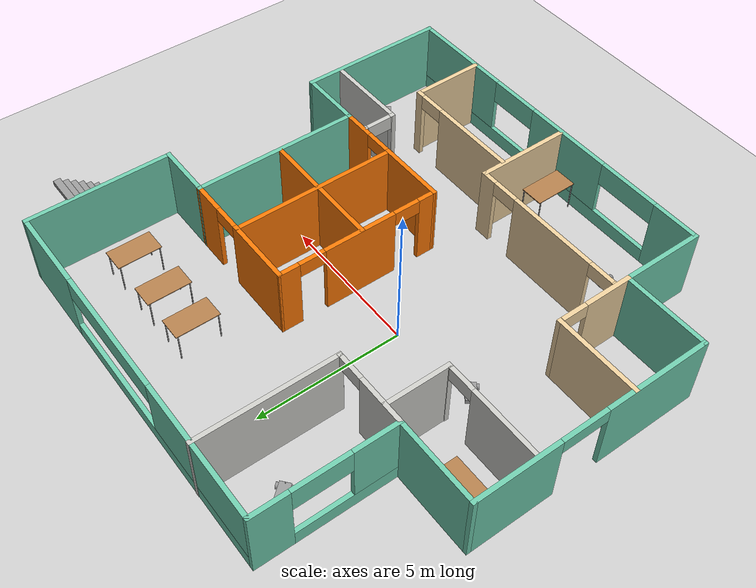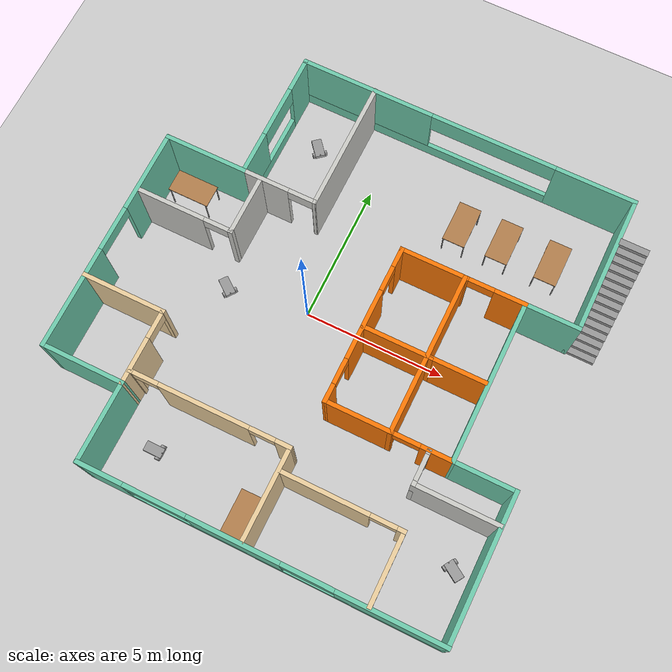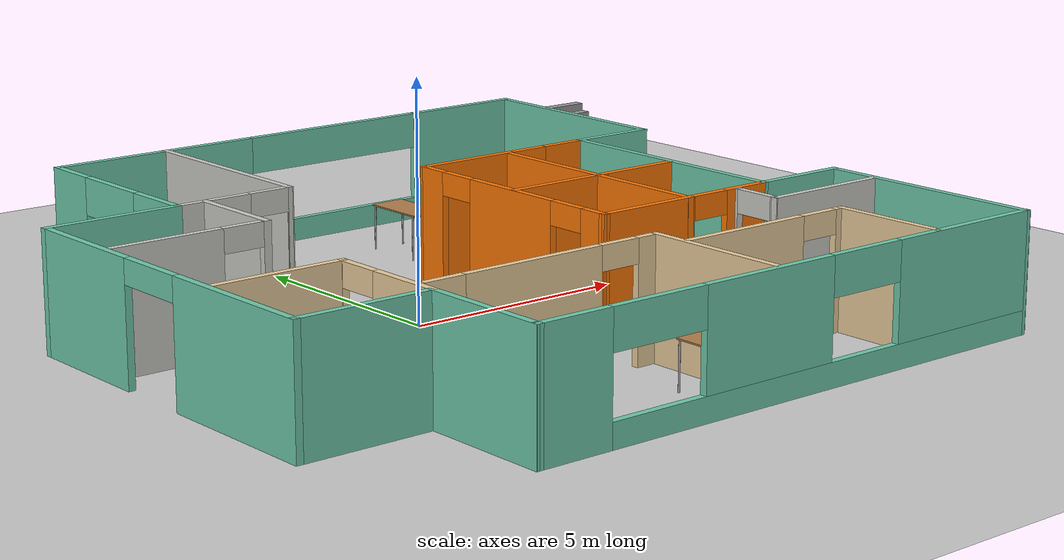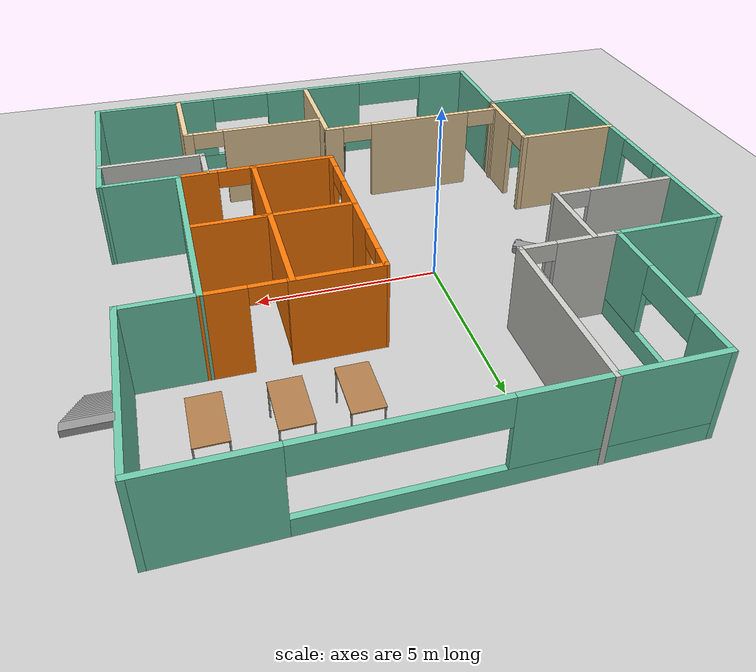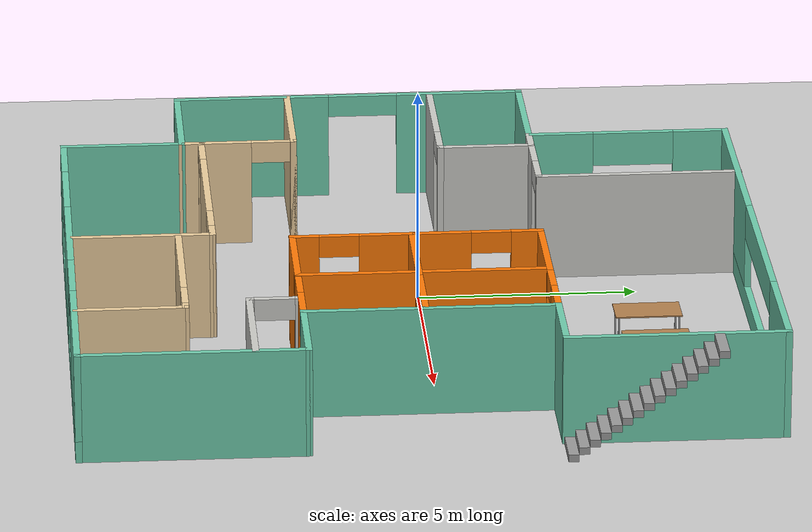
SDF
<sdf version="1.6">
 <world name="default">
  <plugin name="welcome_message" filename="libwelcome_message.so"/>
  <light name="sun" type="directional">
   <pose>0 0 10 0 -0 0</pose>
   <diffuse>0.8 0.8 0.8 1</diffuse>
   <specular>0.2 0.2 0.2 1</specular>
   <attenuation>
    <range>1000</range>
    <constant>0.9</constant>
    <linear>0.01</linear>
    <quadratic>0.001</quadratic>
   </attenuation>
   <direction>-0.5 0.1 -0.9</direction>
  </light>
  <model name="ground_plane">
   <static>1</static>
   <link name="link">
    <collision name="collision">
     <geometry><plane><normal>0 0 1</normal><size>100 100</size></plane></geometry>
     <surface><friction><ode><mu>100</mu><mu2>50</mu2></ode></friction></surface>
    </collision>
    <visual name="visual">
     <cast_shadows>0</cast_shadows>
     <geometry><plane><normal>0 0 1</normal><size>100 100</size></plane></geometry>
     <material>
      <script><uri>file://media/materials/scripts/gazebo.material</uri><name>Gazebo/Grey</name></script>
     </material>
    </visual>
   </link>
  </model>
  <gravity>0 0 -9.8</gravity>
  <magnetic_field>6e-06 2.3e-05 -4.2e-05</magnetic_field>
  <atmosphere type="adiabatic"/>
  <physics name="default_physics" default="0" type="ode">
   <max_step_size>0.001</max_step_size>
   <real_time_factor>1</real_time_factor>
   <real_time_update_rate>1000</real_time_update_rate>
  </physics>
  <scene><ambient>0.4 0.4 0.4 1</ambient><background>0.7 0.7 0.7 1</background><shadows>1</shadows></scene>
  <spherical_coordinates>
   <surface_model>EARTH_WGS84</surface_model>
   <latitude_deg>0</latitude_deg>
   <longitude_deg>0</longitude_deg>
   <elevation>0</elevation>
   <heading_deg>0</heading_deg>
  </spherical_coordinates>
  <model name="Building">
   <link name="Stairs_0">
    <visual name="Stairs_0_Visual_0">
     <pose>7.53348 2.95514 0.083333 0 0 -3.14159</pose>
     <geometry><box><size>1 0.231704 0.166667</size></box></geometry>
     <material>
      <script><uri>file://media/materials/scripts/gazebo.material</uri><name>Gazebo/Grey</name></script>
      <ambient>1 1 1 1</ambient>
      <shader type="pixel"/>
      <diffuse>0.7 0.7 0.7 1</diffuse>
      <specular>0.01 0.01 0.01 1</specular>
      <emissive>0 0 0 1</emissive>
     </material>
     <meta><layer>0</layer></meta>
    </visual>
    <visual name="Stairs_0_Visual_1">
     <pose>7.53348 3.18685 0.25 0 0 -3.14159</pose>
     <geometry><box><size>1 0.231704 0.166667</size></box></geometry>
     <material>
      <script><uri>file://media/materials/scripts/gazebo.material</uri><name>Gazebo/Grey</name></script>
      <ambient>1 1 1 1</ambient>
      <shader type="pixel"/>
      <diffuse>0.7 0.7 0.7 1</diffuse>
      <specular>0.01 0.01 0.01 1</specular>
      <emissive>0 0 0 1</emissive>
     </material>
     <meta><layer>0</layer></meta>
    </visual>
    <visual name="Stairs_0_Visual_2">
     <pose>7.53348 3.41855 0.416667 0 0 -3.14159</pose>
     <geometry><box><size>1 0.231704 0.166667</size></box></geometry>
     <material>
      <script><uri>file://media/materials/scripts/gazebo.material</uri><name>Gazebo/Grey</name></script>
      <ambient>1 1 1 1</ambient>
      <shader type="pixel"/>
      <diffuse>0.7 0.7 0.7 1</diffuse>
      <specular>0.01 0.01 0.01 1</specular>
      <emissive>0 0 0 1</emissive>
     </material>
     <meta><layer>0</layer></meta>
    </visual>
    <visual name="Stairs_0_Visual_3">
     <pose>7.53348 3.65026 0.583333 0 0 -3.14159</pose>
     <geometry><box><size>1 0.231704 0.166667</size></box></geometry>
     <material>
      <script><uri>file://media/materials/scripts/gazebo.material</uri><name>Gazebo/Grey</name></script>
      <ambient>1 1 1 1</ambient>
      <shader type="pixel"/>
      <diffuse>0.7 0.7 0.7 1</diffuse>
      <specular>0.01 0.01 0.01 1</specular>
      <emissive>0 0 0 1</emissive>
     </material>
     <meta><layer>0</layer></meta>
    </visual>
    <visual name="Stairs_0_Visual_4">
     <pose>7.53348 3.88196 0.75 0 0 -3.14159</pose>
     <geometry><box><size>1 0.231704 0.166667</size></box></geometry>
     <material>
      <script><uri>file://media/materials/scripts/gazebo.material</uri><name>Gazebo/Grey</name></script>
      <ambient>1 1 1 1</ambient>
      <shader type="pixel"/>
      <diffuse>0.7 0.7 0.7 1</diffuse>
      <specular>0.01 0.01 0.01 1</specular>
      <emissive>0 0 0 1</emissive>
     </material>
     <meta><layer>0</layer></meta>
    </visual>
    <visual name="Stairs_0_Visual_5">
     <pose>7.53348 4.11367 0.916667 0 0 -3.14159</pose>
     <geometry><box><size>1 0.231704 0.166667</size></box></geometry>
     <material>
      <script><uri>file://media/materials/scripts/gazebo.material</uri><name>Gazebo/Grey</name></script>
      <ambient>1 1 1 1</ambient>
      <shader type="pixel"/>
      <diffuse>0.7 0.7 0.7 1</diffuse>
      <specular>0.01 0.01 0.01 1</specular>
      <emissive>0 0 0 1</emissive>
     </material>
     <meta><layer>0</layer></meta>
    </visual>
    <visual name="Stairs_0_Visual_6">
     <pose>7.53348 4.34537 1.08333 0 0 -3.14159</pose>
     <geometry><box><size>1 0.231704 0.166667</size></box></geometry>
     <material>
      <script><uri>file://media/materials/scripts/gazebo.material</uri><name>Gazebo/Grey</name></script>
      <ambient>1 1 1 1</ambient>
      <shader type="pixel"/>
      <diffuse>0.7 0.7 0.7 1</diffuse>
      <specular>0.01 0.01 0.01 1</specular>
      <emissive>0 0 0 1</emissive>
     </material>
     <meta><layer>0</layer></meta>
    </visual>
    <visual name="Stairs_0_Visual_7">
     <pose>7.53348 4.57708 1.25 0 0 -3.14159</pose>
     <geometry><box><size>1 0.231704 0.166667</size></box></geometry>
     <material>
      <script><uri>file://media/materials/scripts/gazebo.material</uri><name>Gazebo/Grey</name></script>
      <ambient>1 1 1 1</ambient>
      <shader type="pixel"/>
      <diffuse>0.7 0.7 0.7 1</diffuse>
      <specular>0.01 0.01 0.01 1</specular>
      <emissive>0 0 0 1</emissive>
     </material>
     <meta><layer>0</layer></meta>
    </visual>
    <visual name="Stairs_0_Visual_8">
     <pose>7.53348 4.80878 1.41667 0 0 -3.14159</pose>
     <geometry><box><size>1 0.231704 0.166667</size></box></geometry>
     <material>
      <script><uri>file://media/materials/scripts/gazebo.material</uri><name>Gazebo/Grey</name></script>
      <ambient>1 1 1 1</ambient>
      <shader type="pixel"/>
      <diffuse>0.7 0.7 0.7 1</diffuse>
      <specular>0.01 0.01 0.01 1</specular>
      <emissive>0 0 0 1</emissive>
     </material>
     <meta><layer>0</layer></meta>
    </visual>
    <visual name="Stairs_0_Visual_9">
     <pose>7.53348 5.04049 1.58333 0 0 -3.14159</pose>
     <geometry><box><size>1 0.231704 0.166667</size></box></geometry>
     <material>
      <script><uri>file://media/materials/scripts/gazebo.material</uri><name>Gazebo/Grey</name></script>
      <ambient>1 1 1 1</ambient>
      <shader type="pixel"/>
      <diffuse>0.7 0.7 0.7 1</diffuse>
      <specular>0.01 0.01 0.01 1</specular>
      <emissive>0 0 0 1</emissive>
     </material>
     <meta><layer>0</layer></meta>
    </visual>
    <visual name="Stairs_0_Visual_10">
     <pose>7.53348 5.27219 1.75 0 0 -3.14159</pose>
     <geometry><box><size>1 0.231704 0.166667</size></box></geometry>
     <material>
      <script><uri>file://media/materials/scripts/gazebo.material</uri><name>Gazebo/Grey</name></script>
      <ambient>1 1 1 1</ambient>
      <shader type="pixel"/>
      <diffuse>0.7 0.7 0.7 1</diffuse>
      <specular>0.01 0.01 0.01 1</specular>
      <emissive>0 0 0 1</emissive>
     </material>
     <meta><layer>0</layer></meta>
    </visual>
    <visual name="Stairs_0_Visual_11">
     <pose>7.53348 5.50389 1.91667 0 0 -3.14159</pose>
     <geometry><box><size>1 0.231704 0.166667</size></box></geometry>
     <material>
      <script><uri>file://media/materials/scripts/gazebo.material</uri><name>Gazebo/Grey</name></script>
      <ambient>1 1 1 1</ambient>
      <shader type="pixel"/>
      <diffuse>0.7 0.7 0.7 1</diffuse>
      <specular>0.01 0.01 0.01 1</specular>
      <emissive>0 0 0 1</emissive>
     </material>
     <meta><layer>0</layer></meta>
    </visual>
    <visual name="Stairs_0_Visual_12">
     <pose>7.53348 5.7356 2.08333 0 0 -3.14159</pose>
     <geometry><box><size>1 0.231704 0.166667</size></box></geometry>
     <material>
      <script><uri>file://media/materials/scripts/gazebo.material</uri><name>Gazebo/Grey</name></script>
      <ambient>1 1 1 1</ambient>
      <shader type="pixel"/>
      <diffuse>0.7 0.7 0.7 1</diffuse>
      <specular>0.01 0.01 0.01 1</specular>
      <emissive>0 0 0 1</emissive>
     </material>
     <meta><layer>0</layer></meta>
    </visual>
    <visual name="Stairs_0_Visual_13">
     <pose>7.53348 5.9673 2.25 0 0 -3.14159</pose>
     <geometry><box><size>1 0.231704 0.166667</size></box></geometry>
     <material>
      <script><uri>file://media/materials/scripts/gazebo.material</uri><name>Gazebo/Grey</name></script>
      <ambient>1 1 1 1</ambient>
      <shader type="pixel"/>
      <diffuse>0.7 0.7 0.7 1</diffuse>
      <specular>0.01 0.01 0.01 1</specular>
      <emissive>0 0 0 1</emissive>
     </material>
     <meta><layer>0</layer></meta>
    </visual>
    <visual name="Stairs_0_Visual_14">
     <pose>7.53348 6.19901 2.41667 0 0 -3.14159</pose>
     <geometry><box><size>1 0.231704 0.166667</size></box></geometry>
     <material>
      <script><uri>file://media/materials/scripts/gazebo.material</uri><name>Gazebo/Grey</name></script>
      <ambient>1 1 1 1</ambient>
      <shader type="pixel"/>
      <diffuse>0.7 0.7 0.7 1</diffuse>
      <specular>0.01 0.01 0.01 1</specular>
      <emissive>0 0 0 1</emissive>
     </material>
     <meta><layer>0</layer></meta>
    </visual>
    <collision name="Stairs_0_Collision_6">
     <pose>7.53348 4.34537 1.08333 0 0 -3.14159</pose>
     <geometry><box><size>1 0.231704 0.166667</size></box></geometry>
     <surface>
      <friction>
       <ode><mu>1</mu><mu2>1</mu2><fdir1>0 0 0</fdir1><slip1>0</slip1><slip2>0</slip2></ode>
       <torsional>
        <coefficient>1</coefficient>
        <patch_radius>0</patch_radius>
        <surface_radius>0</surface_radius>
        <use_patch_radius>1</use_patch_radius>
        <ode><slip>0</slip></ode>
       </torsional>
      </friction>
      <bounce><restitution_coefficient>0</restitution_coefficient><threshold>1e+06</threshold></bounce>
      <contact>
       <collide_without_contact>0</collide_without_contact>
       <collide_without_contact_bitmask>1</collide_without_contact_bitmask>
       <collide_bitmask>1</collide_bitmask>
       <ode>
        <soft_cfm>0</soft_cfm>
        <soft_erp>0.2</soft_erp>
        <kp>1e+13</kp>
        <kd>1</kd>
        <max_vel>0.01</max_vel>
        <min_depth>0</min_depth>
       </ode>
       <bullet>
        <split_impulse>1</split_impulse>
        <split_impulse_penetration_threshold>-0.01</split_impulse_penetration_threshold>
        <soft_cfm>0</soft_cfm>
        <soft_erp>0.2</soft_erp>
        <kp>1e+13</kp>
        <kd>1</kd>
       </bullet>
      </contact>
     </surface>
    </collision>
    <collision name="Stairs_0_Collision_0">
     <pose>7.53348 2.95514 0.083333 0 0 -3.14159</pose>
     <geometry><box><size>1 0.231704 0.166667</size></box></geometry>
     <surface>
      <friction>
       <ode><mu>1</mu><mu2>1</mu2><fdir1>0 0 0</fdir1><slip1>0</slip1><slip2>0</slip2></ode>
       <torsional>
        <coefficient>1</coefficient>
        <patch_radius>0</patch_radius>
        <surface_radius>0</surface_radius>
        <use_patch_radius>1</use_patch_radius>
        <ode><slip>0</slip></ode>
       </torsional>
      </friction>
      <bounce><restitution_coefficient>0</restitution_coefficient><threshold>1e+06</threshold></bounce>
      <contact>
       <collide_without_contact>0</collide_without_contact>
       <collide_without_contact_bitmask>1</collide_without_contact_bitmask>
       <collide_bitmask>1</collide_bitmask>
       <ode>
        <soft_cfm>0</soft_cfm>
        <soft_erp>0.2</soft_erp>
        <kp>1e+13</kp>
        <kd>1</kd>
        <max_vel>0.01</max_vel>
        <min_depth>0</min_depth>
       </ode>
       <bullet>
        <split_impulse>1</split_impulse>
        <split_impulse_penetration_threshold>-0.01</split_impulse_penetration_threshold>
        <soft_cfm>0</soft_cfm>
        <soft_erp>0.2</soft_erp>
        <kp>1e+13</kp>
        <kd>1</kd>
       </bullet>
      </contact>
     </surface>
    </collision>
    <collision name="Stairs_0_Collision_2">
     <pose>7.53348 3.41855 0.416667 0 0 -3.14159</pose>
     <geometry><box><size>1 0.231704 0.166667</size></box></geometry>
     <surface>
      <friction>
       <ode><mu>1</mu><mu2>1</mu2><fdir1>0 0 0</fdir1><slip1>0</slip1><slip2>0</slip2></ode>
       <torsional>
        <coefficient>1</coefficient>
        <patch_radius>0</patch_radius>
        <surface_radius>0</surface_radius>
        <use_patch_radius>1</use_patch_radius>
        <ode><slip>0</slip></ode>
       </torsional>
      </friction>
      <bounce><restitution_coefficient>0</restitution_coefficient><threshold>1e+06</threshold></bounce>
      <contact>
       <collide_without_contact>0</collide_without_contact>
       <collide_without_contact_bitmask>1</collide_without_contact_bitmask>
       <collide_bitmask>1</collide_bitmask>
       <ode>
        <soft_cfm>0</soft_cfm>
        <soft_erp>0.2</soft_erp>
        <kp>1e+13</kp>
        <kd>1</kd>
        <max_vel>0.01</max_vel>
        <min_depth>0</min_depth>
       </ode>
       <bullet>
        <split_impulse>1</split_impulse>
        <split_impulse_penetration_threshold>-0.01</split_impulse_penetration_threshold>
        <soft_cfm>0</soft_cfm>
        <soft_erp>0.2</soft_erp>
        <kp>1e+13</kp>
        <kd>1</kd>
       </bullet>
      </contact>
     </surface>
    </collision>
    <collision name="Stairs_0_Collision_1">
     <pose>7.53348 3.18685 0.25 0 0 -3.14159</pose>
     <geometry><box><size>1 0.231704 0.166667</size></box></geometry>
     <surface>
      <friction>
       <ode><mu>1</mu><mu2>1</mu2><fdir1>0 0 0</fdir1><slip1>0</slip1><slip2>0</slip2></ode>
       <torsional>
        <coefficient>1</coefficient>
        <patch_radius>0</patch_radius>
        <surface_radius>0</surface_radius>
        <use_patch_radius>1</use_patch_radius>
        <ode><slip>0</slip></ode>
       </torsional>
      </friction>
      <bounce><restitution_coefficient>0</restitution_coefficient><threshold>1e+06</threshold></bounce>
      <contact>
       <collide_without_contact>0</collide_without_contact>
       <collide_without_contact_bitmask>1</collide_without_contact_bitmask>
       <collide_bitmask>1</collide_bitmask>
       <ode>
        <soft_cfm>0</soft_cfm>
        <soft_erp>0.2</soft_erp>
        <kp>1e+13</kp>
        <kd>1</kd>
        <max_vel>0.01</max_vel>
        <min_depth>0</min_depth>
       </ode>
       <bullet>
        <split_impulse>1</split_impulse>
        <split_impulse_penetration_threshold>-0.01</split_impulse_penetration_threshold>
        <soft_cfm>0</soft_cfm>
        <soft_erp>0.2</soft_erp>
        <kp>1e+13</kp>
        <kd>1</kd>
       </bullet>
      </contact>
     </surface>
    </collision>
    <collision name="Stairs_0_Collision_4">
     <pose>7.53348 3.88196 0.75 0 0 -3.14159</pose>
     <geometry><box><size>1 0.231704 0.166667</size></box></geometry>
     <surface>
      <friction>
       <ode><mu>1</mu><mu2>1</mu2><fdir1>0 0 0</fdir1><slip1>0</slip1><slip2>0</slip2></ode>
       <torsional>
        <coefficient>1</coefficient>
        <patch_radius>0</patch_radius>
        <surface_radius>0</surface_radius>
        <use_patch_radius>1</use_patch_radius>
        <ode><slip>0</slip></ode>
       </torsional>
      </friction>
      <bounce><restitution_coefficient>0</restitution_coefficient><threshold>1e+06</threshold></bounce>
      <contact>
       <collide_without_contact>0</collide_without_contact>
       <collide_without_contact_bitmask>1</collide_without_contact_bitmask>
       <collide_bitmask>1</collide_bitmask>
       <ode>
        <soft_cfm>0</soft_cfm>
        <soft_erp>0.2</soft_erp>
        <kp>1e+13</kp>
        <kd>1</kd>
        <max_vel>0.01</max_vel>
        <min_depth>0</min_depth>
       </ode>
       <bullet>
        <split_impulse>1</split_impulse>
        <split_impulse_penetration_threshold>-0.01</split_impulse_penetration_threshold>
        <soft_cfm>0</soft_cfm>
        <soft_erp>0.2</soft_erp>
        <kp>1e+13</kp>
        <kd>1</kd>
       </bullet>
      </contact>
     </surface>
    </collision>
    <collision name="Stairs_0_Collision_3">
     <pose>7.53348 3.65026 0.583333 0 0 -3.14159</pose>
     <geometry><box><size>1 0.231704 0.166667</size></box></geometry>
     <surface>
      <friction>
       <ode><mu>1</mu><mu2>1</mu2><fdir1>0 0 0</fdir1><slip1>0</slip1><slip2>0</slip2></ode>
       <torsional>
        <coefficient>1</coefficient>
        <patch_radius>0</patch_radius>
        <surface_radius>0</surface_radius>
        <use_patch_radius>1</use_patch_radius>
        <ode><slip>0</slip></ode>
       </torsional>
      </friction>
      <bounce><restitution_coefficient>0</restitution_coefficient><threshold>1e+06</threshold></bounce>
      <contact>
       <collide_without_contact>0</collide_without_contact>
       <collide_without_contact_bitmask>1</collide_without_contact_bitmask>
       <collide_bitmask>1</collide_bitmask>
       <ode>
        <soft_cfm>0</soft_cfm>
        <soft_erp>0.2</soft_erp>
        <kp>1e+13</kp>
        <kd>1</kd>
        <max_vel>0.01</max_vel>
        <min_depth>0</min_depth>
       </ode>
       <bullet>
        <split_impulse>1</split_impulse>
        <split_impulse_penetration_threshold>-0.01</split_impulse_penetration_threshold>
        <soft_cfm>0</soft_cfm>
        <soft_erp>0.2</soft_erp>
        <kp>1e+13</kp>
        <kd>1</kd>
       </bullet>
      </contact>
     </surface>
    </collision>
    <collision name="Stairs_0_Collision_5">
     <pose>7.53348 4.11367 0.916667 0 0 -3.14159</pose>
     <geometry><box><size>1 0.231704 0.166667</size></box></geometry>
     <surface>
      <friction>
       <ode><mu>1</mu><mu2>1</mu2><fdir1>0 0 0</fdir1><slip1>0</slip1><slip2>0</slip2></ode>
       <torsional>
        <coefficient>1</coefficient>
        <patch_radius>0</patch_radius>
        <surface_radius>0</surface_radius>
        <use_patch_radius>1</use_patch_radius>
        <ode><slip>0</slip></ode>
       </torsional>
      </friction>
      <bounce><restitution_coefficient>0</restitution_coefficient><threshold>1e+06</threshold></bounce>
      <contact>
       <collide_without_contact>0</collide_without_contact>
       <collide_without_contact_bitmask>1</collide_without_contact_bitmask>
       <collide_bitmask>1</collide_bitmask>
       <ode>
        <soft_cfm>0</soft_cfm>
        <soft_erp>0.2</soft_erp>
        <kp>1e+13</kp>
        <kd>1</kd>
        <max_vel>0.01</max_vel>
        <min_depth>0</min_depth>
       </ode>
       <bullet>
        <split_impulse>1</split_impulse>
        <split_impulse_penetration_threshold>-0.01</split_impulse_penetration_threshold>
        <soft_cfm>0</soft_cfm>
        <soft_erp>0.2</soft_erp>
        <kp>1e+13</kp>
        <kd>1</kd>
       </bullet>
      </contact>
     </surface>
    </collision>
    <collision name="Stairs_0_Collision_8">
     <pose>7.53348 4.80878 1.41667 0 0 -3.14159</pose>
     <geometry><box><size>1 0.231704 0.166667</size></box></geometry>
     <surface>
      <friction>
       <ode><mu>1</mu><mu2>1</mu2><fdir1>0 0 0</fdir1><slip1>0</slip1><slip2>0</slip2></ode>
       <torsional>
        <coefficient>1</coefficient>
        <patch_radius>0</patch_radius>
        <surface_radius>0</surface_radius>
        <use_patch_radius>1</use_patch_radius>
        <ode><slip>0</slip></ode>
       </torsional>
      </friction>
      <bounce><restitution_coefficient>0</restitution_coefficient><threshold>1e+06</threshold></bounce>
      <contact>
       <collide_without_contact>0</collide_without_contact>
       <collide_without_contact_bitmask>1</collide_without_contact_bitmask>
       <collide_bitmask>1</collide_bitmask>
       <ode>
        <soft_cfm>0</soft_cfm>
        <soft_erp>0.2</soft_erp>
        <kp>1e+13</kp>
        <kd>1</kd>
        <max_vel>0.01</max_vel>
        <min_depth>0</min_depth>
       </ode>
       <bullet>
        <split_impulse>1</split_impulse>
        <split_impulse_penetration_threshold>-0.01</split_impulse_penetration_threshold>
        <soft_cfm>0</soft_cfm>
        <soft_erp>0.2</soft_erp>
        <kp>1e+13</kp>
        <kd>1</kd>
       </bullet>
      </contact>
     </surface>
    </collision>
    <collision name="Stairs_0_Collision_7">
     <pose>7.53348 4.57708 1.25 0 0 -3.14159</pose>
     <geometry><box><size>1 0.231704 0.166667</size></box></geometry>
     <surface>
      <friction>
       <ode><mu>1</mu><mu2>1</mu2><fdir1>0 0 0</fdir1><slip1>0</slip1><slip2>0</slip2></ode>
       <torsional>
        <coefficient>1</coefficient>
        <patch_radius>0</patch_radius>
        <surface_radius>0</surface_radius>
        <use_patch_radius>1</use_patch_radius>
        <ode><slip>0</slip></ode>
       </torsional>
      </friction>
      <bounce><restitution_coefficient>0</restitution_coefficient><threshold>1e+06</threshold></bounce>
      <contact>
       <collide_without_contact>0</collide_without_contact>
       <collide_without_contact_bitmask>1</collide_without_contact_bitmask>
       <collide_bitmask>1</collide_bitmask>
       <ode>
        <soft_cfm>0</soft_cfm>
        <soft_erp>0.2</soft_erp>
        <kp>1e+13</kp>
        <kd>1</kd>
        <max_vel>0.01</max_vel>
        <min_depth>0</min_depth>
       </ode>
       <bullet>
        <split_impulse>1</split_impulse>
        <split_impulse_penetration_threshold>-0.01</split_impulse_penetration_threshold>
        <soft_cfm>0</soft_cfm>
        <soft_erp>0.2</soft_erp>
        <kp>1e+13</kp>
        <kd>1</kd>
       </bullet>
      </contact>
     </surface>
    </collision>
    <collision name="Stairs_0_Collision_9">
     <pose>7.53348 5.04049 1.58333 0 0 -3.14159</pose>
     <geometry><box><size>1 0.231704 0.166667</size></box></geometry>
     <surface>
      <friction>
       <ode><mu>1</mu><mu2>1</mu2><fdir1>0 0 0</fdir1><slip1>0</slip1><slip2>0</slip2></ode>
       <torsional>
        <coefficient>1</coefficient>
        <patch_radius>0</patch_radius>
        <surface_radius>0</surface_radius>
        <use_patch_radius>1</use_patch_radius>
        <ode><slip>0</slip></ode>
       </torsional>
      </friction>
      <bounce><restitution_coefficient>0</restitution_coefficient><threshold>1e+06</threshold></bounce>
      <contact>
       <collide_without_contact>0</collide_without_contact>
       <collide_without_contact_bitmask>1</collide_without_contact_bitmask>
       <collide_bitmask>1</collide_bitmask>
       <ode>
        <soft_cfm>0</soft_cfm>
        <soft_erp>0.2</soft_erp>
        <kp>1e+13</kp>
        <kd>1</kd>
        <max_vel>0.01</max_vel>
        <min_depth>0</min_depth>
       </ode>
       <bullet>
        <split_impulse>1</split_impulse>
        <split_impulse_penetration_threshold>-0.01</split_impulse_penetration_threshold>
        <soft_cfm>0</soft_cfm>
        <soft_erp>0.2</soft_erp>
        <kp>1e+13</kp>
        <kd>1</kd>
       </bullet>
      </contact>
     </surface>
    </collision>
    <collision name="Stairs_0_Collision_10">
     <pose>7.53348 5.27219 1.75 0 0 -3.14159</pose>
     <geometry><box><size>1 0.231704 0.166667</size></box></geometry>
     <surface>
      <friction>
       <ode><mu>1</mu><mu2>1</mu2><fdir1>0 0 0</fdir1><slip1>0</slip1><slip2>0</slip2></ode>
       <torsional>
        <coefficient>1</coefficient>
        <patch_radius>0</patch_radius>
        <surface_radius>0</surface_radius>
        <use_patch_radius>1</use_patch_radius>
        <ode><slip>0</slip></ode>
       </torsional>
      </friction>
      <bounce><restitution_coefficient>0</restitution_coefficient><threshold>1e+06</threshold></bounce>
      <contact>
       <collide_without_contact>0</collide_without_contact>
       <collide_without_contact_bitmask>1</collide_without_contact_bitmask>
       <collide_bitmask>1</collide_bitmask>
       <ode>
        <soft_cfm>0</soft_cfm>
        <soft_erp>0.2</soft_erp>
        <kp>1e+13</kp>
        <kd>1</kd>
        <max_vel>0.01</max_vel>
        <min_depth>0</min_depth>
       </ode>
       <bullet>
        <split_impulse>1</split_impulse>
        <split_impulse_penetration_threshold>-0.01</split_impulse_penetration_threshold>
        <soft_cfm>0</soft_cfm>
        <soft_erp>0.2</soft_erp>
        <kp>1e+13</kp>
        <kd>1</kd>
       </bullet>
      </contact>
     </surface>
    </collision>
    <collision name="Stairs_0_Collision_11">
     <pose>7.53348 5.50389 1.91667 0 0 -3.14159</pose>
     <geometry><box><size>1 0.231704 0.166667</size></box></geometry>
     <surface>
      <friction>
       <ode><mu>1</mu><mu2>1</mu2><fdir1>0 0 0</fdir1><slip1>0</slip1><slip2>0</slip2></ode>
       <torsional>
        <coefficient>1</coefficient>
        <patch_radius>0</patch_radius>
        <surface_radius>0</surface_radius>
        <use_patch_radius>1</use_patch_radius>
        <ode><slip>0</slip></ode>
       </torsional>
      </friction>
      <bounce><restitution_coefficient>0</restitution_coefficient><threshold>1e+06</threshold></bounce>
      <contact>
       <collide_without_contact>0</collide_without_contact>
       <collide_without_contact_bitmask>1</collide_without_contact_bitmask>
       <collide_bitmask>1</collide_bitmask>
       <ode>
        <soft_cfm>0</soft_cfm>
        <soft_erp>0.2</soft_erp>
        <kp>1e+13</kp>
        <kd>1</kd>
        <max_vel>0.01</max_vel>
        <min_depth>0</min_depth>
       </ode>
       <bullet>
        <split_impulse>1</split_impulse>
        <split_impulse_penetration_threshold>-0.01</split_impulse_penetration_threshold>
        <soft_cfm>0</soft_cfm>
        <soft_erp>0.2</soft_erp>
        <kp>1e+13</kp>
        <kd>1</kd>
       </bullet>
      </contact>
     </surface>
    </collision>
    <collision name="Stairs_0_Collision_12">
     <pose>7.53348 5.7356 2.08333 0 0 -3.14159</pose>
     <geometry><box><size>1 0.231704 0.166667</size></box></geometry>
     <surface>
      <friction>
       <ode><mu>1</mu><mu2>1</mu2><fdir1>0 0 0</fdir1><slip1>0</slip1><slip2>0</slip2></ode>
       <torsional>
        <coefficient>1</coefficient>
        <patch_radius>0</patch_radius>
        <surface_radius>0</surface_radius>
        <use_patch_radius>1</use_patch_radius>
        <ode><slip>0</slip></ode>
       </torsional>
      </friction>
      <bounce><restitution_coefficient>0</restitution_coefficient><threshold>1e+06</threshold></bounce>
      <contact>
       <collide_without_contact>0</collide_without_contact>
       <collide_without_contact_bitmask>1</collide_without_contact_bitmask>
       <collide_bitmask>1</collide_bitmask>
       <ode>
        <soft_cfm>0</soft_cfm>
        <soft_erp>0.2</soft_erp>
        <kp>1e+13</kp>
        <kd>1</kd>
        <max_vel>0.01</max_vel>
        <min_depth>0</min_depth>
       </ode>
       <bullet>
        <split_impulse>1</split_impulse>
        <split_impulse_penetration_threshold>-0.01</split_impulse_penetration_threshold>
        <soft_cfm>0</soft_cfm>
        <soft_erp>0.2</soft_erp>
        <kp>1e+13</kp>
        <kd>1</kd>
       </bullet>
      </contact>
     </surface>
    </collision>
    <collision name="Stairs_0_Collision_14">
     <pose>7.53348 6.19901 2.41667 0 0 -3.14159</pose>
     <geometry><box><size>1 0.231704 0.166667</size></box></geometry>
     <surface>
      <friction>
       <ode><mu>1</mu><mu2>1</mu2><fdir1>0 0 0</fdir1><slip1>0</slip1><slip2>0</slip2></ode>
       <torsional>
        <coefficient>1</coefficient>
        <patch_radius>0</patch_radius>
        <surface_radius>0</surface_radius>
        <use_patch_radius>1</use_patch_radius>
        <ode><slip>0</slip></ode>
       </torsional>
      </friction>
      <bounce><restitution_coefficient>0</restitution_coefficient><threshold>1e+06</threshold></bounce>
      <contact>
       <collide_without_contact>0</collide_without_contact>
       <collide_without_contact_bitmask>1</collide_without_contact_bitmask>
       <collide_bitmask>1</collide_bitmask>
       <ode>
        <soft_cfm>0</soft_cfm>
        <soft_erp>0.2</soft_erp>
        <kp>1e+13</kp>
        <kd>1</kd>
        <max_vel>0.01</max_vel>
        <min_depth>0</min_depth>
       </ode>
       <bullet>
        <split_impulse>1</split_impulse>
        <split_impulse_penetration_threshold>-0.01</split_impulse_penetration_threshold>
        <soft_cfm>0</soft_cfm>
        <soft_erp>0.2</soft_erp>
        <kp>1e+13</kp>
        <kd>1</kd>
       </bullet>
      </contact>
     </surface>
    </collision>
    <collision name="Stairs_0_Collision_13">
     <pose>7.53348 5.9673 2.25 0 0 -3.14159</pose>
     <geometry><box><size>1 0.231704 0.166667</size></box></geometry>
     <surface>
      <friction>
       <ode><mu>1</mu><mu2>1</mu2><fdir1>0 0 0</fdir1><slip1>0</slip1><slip2>0</slip2></ode>
       <torsional>
        <coefficient>1</coefficient>
        <patch_radius>0</patch_radius>
        <surface_radius>0</surface_radius>
        <use_patch_radius>1</use_patch_radius>
        <ode><slip>0</slip></ode>
       </torsional>
      </friction>
      <bounce><restitution_coefficient>0</restitution_coefficient><threshold>1e+06</threshold></bounce>
      <contact>
       <collide_without_contact>0</collide_without_contact>
       <collide_without_contact_bitmask>1</collide_without_contact_bitmask>
       <collide_bitmask>1</collide_bitmask>
       <ode>
        <soft_cfm>0</soft_cfm>
        <soft_erp>0.2</soft_erp>
        <kp>1e+13</kp>
        <kd>1</kd>
        <max_vel>0.01</max_vel>
        <min_depth>0</min_depth>
       </ode>
       <bullet>
        <split_impulse>1</split_impulse>
        <split_impulse_penetration_threshold>-0.01</split_impulse_penetration_threshold>
        <soft_cfm>0</soft_cfm>
        <soft_erp>0.2</soft_erp>
        <kp>1e+13</kp>
        <kd>1</kd>
       </bullet>
      </contact>
     </surface>
    </collision>
   </link>
   <link name="Wall_10">
    <pose>6.19158 -2.73169 0 0 -0 3.14159</pose>
    <visual name="Wall_10_Visual">
     <pose>0 0 1.25 0 -0 0</pose>
     <geometry><box><size>2.25 0.15 2.5</size></box></geometry>
     <material>
      <script><uri>file://media/materials/scripts/gazebo.material</uri><name>Gazebo/Grey</name></script>
      <ambient>0.435294 0.796078 0.67451 1</ambient>
      <shader type="pixel"/>
      <diffuse>0.7 0.7 0.7 1</diffuse>
      <specular>0.01 0.01 0.01 1</specular>
      <emissive>0 0 0 1</emissive>
     </material>
     <meta><layer>0</layer></meta>
    </visual>
    <collision name="Wall_10_Collision">
     <pose>0 0 1.25 0 -0 0</pose>
     <geometry><box><size>2.25 0.15 2.5</size></box></geometry>
     <surface>
      <friction>
       <ode><mu>1</mu><mu2>1</mu2><fdir1>0 0 0</fdir1><slip1>0</slip1><slip2>0</slip2></ode>
       <torsional>
        <coefficient>1</coefficient>
        <patch_radius>0</patch_radius>
        <surface_radius>0</surface_radius>
        <use_patch_radius>1</use_patch_radius>
        <ode><slip>0</slip></ode>
       </torsional>
      </friction>
      <bounce><restitution_coefficient>0</restitution_coefficient><threshold>1e+06</threshold></bounce>
      <contact>
       <collide_without_contact>0</collide_without_contact>
       <collide_without_contact_bitmask>1</collide_without_contact_bitmask>
       <collide_bitmask>1</collide_bitmask>
       <ode>
        <soft_cfm>0</soft_cfm>
        <soft_erp>0.2</soft_erp>
        <kp>1e+13</kp>
        <kd>1</kd>
        <max_vel>0.01</max_vel>
        <min_depth>0</min_depth>
       </ode>
       <bullet>
        <split_impulse>1</split_impulse>
        <split_impulse_penetration_threshold>-0.01</split_impulse_penetration_threshold>
        <soft_cfm>0</soft_cfm>
        <soft_erp>0.2</soft_erp>
        <kp>1e+13</kp>
        <kd>1</kd>
       </bullet>
      </contact>
     </surface>
    </collision>
   </link>
   <link name="Wall_11">
    <pose>5.14158 0.068309 0 0 -0 1.5708</pose>
    <visual name="Wall_11_Visual">
     <pose>0 0 1.25 0 -0 0</pose>
     <geometry><box><size>5.75 0.15 2.5</size></box></geometry>
     <material>
      <script><uri>file://media/materials/scripts/gazebo.material</uri><name>Gazebo/Grey</name></script>
      <ambient>0.435294 0.796078 0.67451 1</ambient>
      <shader type="pixel"/>
      <diffuse>0.7 0.7 0.7 1</diffuse>
      <specular>0.01 0.01 0.01 1</specular>
      <emissive>0 0 0 1</emissive>
     </material>
     <meta><layer>0</layer></meta>
    </visual>
    <collision name="Wall_11_Collision">
     <pose>0 0 1.25 0 -0 0</pose>
     <geometry><box><size>5.75 0.15 2.5</size></box></geometry>
     <surface>
      <friction>
       <ode><mu>1</mu><mu2>1</mu2><fdir1>0 0 0</fdir1><slip1>0</slip1><slip2>0</slip2></ode>
       <torsional>
        <coefficient>1</coefficient>
        <patch_radius>0</patch_radius>
        <surface_radius>0</surface_radius>
        <use_patch_radius>1</use_patch_radius>
        <ode><slip>0</slip></ode>
       </torsional>
      </friction>
      <bounce><restitution_coefficient>0</restitution_coefficient><threshold>1e+06</threshold></bounce>
      <contact>
       <collide_without_contact>0</collide_without_contact>
       <collide_without_contact_bitmask>1</collide_without_contact_bitmask>
       <collide_bitmask>1</collide_bitmask>
       <ode>
        <soft_cfm>0</soft_cfm>
        <soft_erp>0.2</soft_erp>
        <kp>1e+13</kp>
        <kd>1</kd>
        <max_vel>0.01</max_vel>
        <min_depth>0</min_depth>
       </ode>
       <bullet>
        <split_impulse>1</split_impulse>
        <split_impulse_penetration_threshold>-0.01</split_impulse_penetration_threshold>
        <soft_cfm>0</soft_cfm>
        <soft_erp>0.2</soft_erp>
        <kp>1e+13</kp>
        <kd>1</kd>
       </bullet>
      </contact>
     </surface>
    </collision>
   </link>
   <link name="Wall_12">
    <pose>6.06658 2.86831 0 0 -0 0</pose>
    <visual name="Wall_12_Visual">
     <pose>0 0 1.25 0 -0 0</pose>
     <geometry><box><size>2 0.15 2.5</size></box></geometry>
     <material>
      <script><uri>file://media/materials/scripts/gazebo.material</uri><name>Gazebo/Grey</name></script>
      <ambient>0.435294 0.796078 0.67451 1</ambient>
      <shader type="pixel"/>
      <diffuse>0.7 0.7 0.7 1</diffuse>
      <specular>0.01 0.01 0.01 1</specular>
      <emissive>0 0 0 1</emissive>
     </material>
     <meta><layer>0</layer></meta>
    </visual>
    <collision name="Wall_12_Collision">
     <pose>0 0 1.25 0 -0 0</pose>
     <geometry><box><size>2 0.15 2.5</size></box></geometry>
     <surface>
      <friction>
       <ode><mu>1</mu><mu2>1</mu2><fdir1>0 0 0</fdir1><slip1>0</slip1><slip2>0</slip2></ode>
       <torsional>
        <coefficient>1</coefficient>
        <patch_radius>0</patch_radius>
        <surface_radius>0</surface_radius>
        <use_patch_radius>1</use_patch_radius>
        <ode><slip>0</slip></ode>
       </torsional>
      </friction>
      <bounce><restitution_coefficient>0</restitution_coefficient><threshold>1e+06</threshold></bounce>
      <contact>
       <collide_without_contact>0</collide_without_contact>
       <collide_without_contact_bitmask>1</collide_without_contact_bitmask>
       <collide_bitmask>1</collide_bitmask>
       <ode>
        <soft_cfm>0</soft_cfm>
        <soft_erp>0.2</soft_erp>
        <kp>1e+13</kp>
        <kd>1</kd>
        <max_vel>0.01</max_vel>
        <min_depth>0</min_depth>
       </ode>
       <bullet>
        <split_impulse>1</split_impulse>
        <split_impulse_penetration_threshold>-0.01</split_impulse_penetration_threshold>
        <soft_cfm>0</soft_cfm>
        <soft_erp>0.2</soft_erp>
        <kp>1e+13</kp>
        <kd>1</kd>
       </bullet>
      </contact>
     </surface>
    </collision>
   </link>
   <link name="Wall_13">
    <pose>6.99158 5.29331 0 0 -0 1.5708</pose>
    <visual name="Wall_13_Visual">
     <pose>0 0 1.25 0 -0 0</pose>
     <geometry><box><size>5 0.15 2.5</size></box></geometry>
     <material>
      <script><uri>file://media/materials/scripts/gazebo.material</uri><name>Gazebo/Grey</name></script>
      <ambient>0.435294 0.796078 0.67451 1</ambient>
      <shader type="pixel"/>
      <diffuse>0.7 0.7 0.7 1</diffuse>
      <specular>0.01 0.01 0.01 1</specular>
      <emissive>0 0 0 1</emissive>
     </material>
     <meta><layer>0</layer></meta>
    </visual>
    <collision name="Wall_13_Collision">
     <pose>0 0 1.25 0 -0 0</pose>
     <geometry><box><size>5 0.15 2.5</size></box></geometry>
     <surface>
      <friction>
       <ode><mu>1</mu><mu2>1</mu2><fdir1>0 0 0</fdir1><slip1>0</slip1><slip2>0</slip2></ode>
       <torsional>
        <coefficient>1</coefficient>
        <patch_radius>0</patch_radius>
        <surface_radius>0</surface_radius>
        <use_patch_radius>1</use_patch_radius>
        <ode><slip>0</slip></ode>
       </torsional>
      </friction>
      <bounce><restitution_coefficient>0</restitution_coefficient><threshold>1e+06</threshold></bounce>
      <contact>
       <collide_without_contact>0</collide_without_contact>
       <collide_without_contact_bitmask>1</collide_without_contact_bitmask>
       <collide_bitmask>1</collide_bitmask>
       <ode>
        <soft_cfm>0</soft_cfm>
        <soft_erp>0.2</soft_erp>
        <kp>1e+13</kp>
        <kd>1</kd>
        <max_vel>0.01</max_vel>
        <min_depth>0</min_depth>
       </ode>
       <bullet>
        <split_impulse>1</split_impulse>
        <split_impulse_penetration_threshold>-0.01</split_impulse_penetration_threshold>
        <soft_cfm>0</soft_cfm>
        <soft_erp>0.2</soft_erp>
        <kp>1e+13</kp>
        <kd>1</kd>
       </bullet>
      </contact>
     </surface>
    </collision>
   </link>
   <link name="Wall_14">
    <pose>0.941578 7.71831 0 0 -0 3.14159</pose>
    <visual name="Wall_14_Visual_0">
     <pose>-4.67981 0 1.25 0 -0 0</pose>
     <geometry><box><size>2.89038 0.15 2.5</size></box></geometry>
     <material>
      <script><uri>file://media/materials/scripts/gazebo.material</uri><name>Gazebo/Grey</name></script>
      <ambient>0.435294 0.796078 0.67451 1</ambient>
      <shader type="pixel"/>
      <diffuse>0.7 0.7 0.7 1</diffuse>
      <specular>0.01 0.01 0.01 1</specular>
      <emissive>0 0 0 1</emissive>
     </material>
     <meta><layer>0</layer></meta>
    </visual>
    <visual name="Wall_14_Visual_1">
     <pose>1.44519 0 0.25 0 -0 0</pose>
     <geometry><box><size>9.35962 0.15 0.5</size></box></geometry>
     <material>
      <script><uri>file://media/materials/scripts/gazebo.material</uri><name>Gazebo/Grey</name></script>
      <ambient>0.435294 0.796078 0.67451 1</ambient>
      <shader type="pixel"/>
      <diffuse>0.7 0.7 0.7 1</diffuse>
      <specular>0.01 0.01 0.01 1</specular>
      <emissive>0 0 0 1</emissive>
     </material>
     <meta><layer>0</layer></meta>
    </visual>
    <visual name="Wall_14_Visual_2">
     <pose>3.69519 0 1.5 0 -0 0</pose>
     <geometry><box><size>4.85962 0.15 2</size></box></geometry>
     <material>
      <script><uri>file://media/materials/scripts/gazebo.material</uri><name>Gazebo/Grey</name></script>
      <ambient>0.435294 0.796078 0.67451 1</ambient>
      <shader type="pixel"/>
      <diffuse>0.7 0.7 0.7 1</diffuse>
      <specular>0.01 0.01 0.01 1</specular>
      <emissive>0 0 0 1</emissive>
     </material>
     <meta><layer>0</layer></meta>
    </visual>
    <visual name="Wall_14_Visual_3">
     <pose>-0.984623 0 2.1 0 -0 0</pose>
     <geometry><box><size>4.5 0.15 0.8</size></box></geometry>
     <material>
      <script><uri>file://media/materials/scripts/gazebo.material</uri><name>Gazebo/Grey</name></script>
      <ambient>0.435294 0.796078 0.67451 1</ambient>
      <shader type="pixel"/>
      <diffuse>0.7 0.7 0.7 1</diffuse>
      <specular>0.01 0.01 0.01 1</specular>
      <emissive>0 0 0 1</emissive>
     </material>
     <meta><layer>0</layer></meta>
    </visual>
    <collision name="Wall_14_Collision_0">
     <pose>-4.67981 0 1.25 0 -0 0</pose>
     <geometry><box><size>2.89038 0.15 2.5</size></box></geometry>
     <surface>
      <friction>
       <ode><mu>1</mu><mu2>1</mu2><fdir1>0 0 0</fdir1><slip1>0</slip1><slip2>0</slip2></ode>
       <torsional>
        <coefficient>1</coefficient>
        <patch_radius>0</patch_radius>
        <surface_radius>0</surface_radius>
        <use_patch_radius>1</use_patch_radius>
        <ode><slip>0</slip></ode>
       </torsional>
      </friction>
      <bounce><restitution_coefficient>0</restitution_coefficient><threshold>1e+06</threshold></bounce>
      <contact>
       <collide_without_contact>0</collide_without_contact>
       <collide_without_contact_bitmask>1</collide_without_contact_bitmask>
       <collide_bitmask>1</collide_bitmask>
       <ode>
        <soft_cfm>0</soft_cfm>
        <soft_erp>0.2</soft_erp>
        <kp>1e+13</kp>
        <kd>1</kd>
        <max_vel>0.01</max_vel>
        <min_depth>0</min_depth>
       </ode>
       <bullet>
        <split_impulse>1</split_impulse>
        <split_impulse_penetration_threshold>-0.01</split_impulse_penetration_threshold>
        <soft_cfm>0</soft_cfm>
        <soft_erp>0.2</soft_erp>
        <kp>1e+13</kp>
        <kd>1</kd>
       </bullet>
      </contact>
     </surface>
    </collision>
    <collision name="Wall_14_Collision_1">
     <pose>1.44519 0 0.25 0 -0 0</pose>
     <geometry><box><size>9.35962 0.15 0.5</size></box></geometry>
     <surface>
      <friction>
       <ode><mu>1</mu><mu2>1</mu2><fdir1>0 0 0</fdir1><slip1>0</slip1><slip2>0</slip2></ode>
       <torsional>
        <coefficient>1</coefficient>
        <patch_radius>0</patch_radius>
        <surface_radius>0</surface_radius>
        <use_patch_radius>1</use_patch_radius>
        <ode><slip>0</slip></ode>
       </torsional>
      </friction>
      <bounce><restitution_coefficient>0</restitution_coefficient><threshold>1e+06</threshold></bounce>
      <contact>
       <collide_without_contact>0</collide_without_contact>
       <collide_without_contact_bitmask>1</collide_without_contact_bitmask>
       <collide_bitmask>1</collide_bitmask>
       <ode>
        <soft_cfm>0</soft_cfm>
        <soft_erp>0.2</soft_erp>
        <kp>1e+13</kp>
        <kd>1</kd>
        <max_vel>0.01</max_vel>
        <min_depth>0</min_depth>
       </ode>
       <bullet>
        <split_impulse>1</split_impulse>
        <split_impulse_penetration_threshold>-0.01</split_impulse_penetration_threshold>
        <soft_cfm>0</soft_cfm>
        <soft_erp>0.2</soft_erp>
        <kp>1e+13</kp>
        <kd>1</kd>
       </bullet>
      </contact>
     </surface>
    </collision>
    <collision name="Wall_14_Collision_2">
     <pose>3.69519 0 1.5 0 -0 0</pose>
     <geometry><box><size>4.85962 0.15 2</size></box></geometry>
     <surface>
      <friction>
       <ode><mu>1</mu><mu2>1</mu2><fdir1>0 0 0</fdir1><slip1>0</slip1><slip2>0</slip2></ode>
       <torsional>
        <coefficient>1</coefficient>
        <patch_radius>0</patch_radius>
        <surface_radius>0</surface_radius>
        <use_patch_radius>1</use_patch_radius>
        <ode><slip>0</slip></ode>
       </torsional>
      </friction>
      <bounce><restitution_coefficient>0</restitution_coefficient><threshold>1e+06</threshold></bounce>
      <contact>
       <collide_without_contact>0</collide_without_contact>
       <collide_without_contact_bitmask>1</collide_without_contact_bitmask>
       <collide_bitmask>1</collide_bitmask>
       <ode>
        <soft_cfm>0</soft_cfm>
        <soft_erp>0.2</soft_erp>
        <kp>1e+13</kp>
        <kd>1</kd>
        <max_vel>0.01</max_vel>
        <min_depth>0</min_depth>
       </ode>
       <bullet>
        <split_impulse>1</split_impulse>
        <split_impulse_penetration_threshold>-0.01</split_impulse_penetration_threshold>
        <soft_cfm>0</soft_cfm>
        <soft_erp>0.2</soft_erp>
        <kp>1e+13</kp>
        <kd>1</kd>
       </bullet>
      </contact>
     </surface>
    </collision>
    <collision name="Wall_14_Collision_3">
     <pose>-0.984623 0 2.1 0 -0 0</pose>
     <geometry><box><size>4.5 0.15 0.8</size></box></geometry>
     <surface>
      <friction>
       <ode><mu>1</mu><mu2>1</mu2><fdir1>0 0 0</fdir1><slip1>0</slip1><slip2>0</slip2></ode>
       <torsional>
        <coefficient>1</coefficient>
        <patch_radius>0</patch_radius>
        <surface_radius>0</surface_radius>
        <use_patch_radius>1</use_patch_radius>
        <ode><slip>0</slip></ode>
       </torsional>
      </friction>
      <bounce><restitution_coefficient>0</restitution_coefficient><threshold>1e+06</threshold></bounce>
      <contact>
       <collide_without_contact>0</collide_without_contact>
       <collide_without_contact_bitmask>1</collide_without_contact_bitmask>
       <collide_bitmask>1</collide_bitmask>
       <ode>
        <soft_cfm>0</soft_cfm>
        <soft_erp>0.2</soft_erp>
        <kp>1e+13</kp>
        <kd>1</kd>
        <max_vel>0.01</max_vel>
        <min_depth>0</min_depth>
       </ode>
       <bullet>
        <split_impulse>1</split_impulse>
        <split_impulse_penetration_threshold>-0.01</split_impulse_penetration_threshold>
        <soft_cfm>0</soft_cfm>
        <soft_erp>0.2</soft_erp>
        <kp>1e+13</kp>
        <kd>1</kd>
       </bullet>
      </contact>
     </surface>
    </collision>
   </link>
   <link name="Wall_253">
    <pose>2.97544 -2.73481 0 0 -0 0.00144</pose>
    <visual name="Wall_253_Visual_0">
     <pose>-1.03152 0 1.25 0 -0 0</pose>
     <geometry><box><size>2.41923 0.15 2.5</size></box></geometry>
     <material>
      <script><uri>file://media/materials/scripts/gazebo.material</uri><name>Gazebo/Grey</name></script>
      <ambient>0.996078 0.47451 0.0196078 1</ambient>
      <shader type="pixel"/>
      <diffuse>0.7 0.7 0.7 1</diffuse>
      <specular>0.01 0.01 0.01 1</specular>
      <emissive>0 0 0 1</emissive>
     </material>
     <meta><layer>0</layer></meta>
    </visual>
    <visual name="Wall_253_Visual_1">
     <pose>1.65962 0 1.25 0 -0 0</pose>
     <geometry><box><size>1.16304 0.15 2.5</size></box></geometry>
     <material>
      <script><uri>file://media/materials/scripts/gazebo.material</uri><name>Gazebo/Grey</name></script>
      <ambient>0.996078 0.47451 0.0196078 1</ambient>
      <shader type="pixel"/>
      <diffuse>0.7 0.7 0.7 1</diffuse>
      <specular>0.01 0.01 0.01 1</specular>
      <emissive>0 0 0 1</emissive>
     </material>
     <meta><layer>0</layer></meta>
    </visual>
    <visual name="Wall_253_Visual_2">
     <pose>0.628096 0 2.25 0 -0 0</pose>
     <geometry><box><size>0.9 0.15 0.5</size></box></geometry>
     <material>
      <script><uri>file://media/materials/scripts/gazebo.material</uri><name>Gazebo/Grey</name></script>
      <ambient>0.996078 0.47451 0.0196078 1</ambient>
      <shader type="pixel"/>
      <diffuse>0.7 0.7 0.7 1</diffuse>
      <specular>0.01 0.01 0.01 1</specular>
      <emissive>0 0 0 1</emissive>
     </material>
     <meta><layer>0</layer></meta>
    </visual>
    <collision name="Wall_253_Collision_0">
     <pose>-1.03152 0 1.25 0 -0 0</pose>
     <geometry><box><size>2.41923 0.15 2.5</size></box></geometry>
     <surface>
      <friction>
       <ode><mu>1</mu><mu2>1</mu2><fdir1>0 0 0</fdir1><slip1>0</slip1><slip2>0</slip2></ode>
       <torsional>
        <coefficient>1</coefficient>
        <patch_radius>0</patch_radius>
        <surface_radius>0</surface_radius>
        <use_patch_radius>1</use_patch_radius>
        <ode><slip>0</slip></ode>
       </torsional>
      </friction>
      <bounce><restitution_coefficient>0</restitution_coefficient><threshold>1e+06</threshold></bounce>
      <contact>
       <collide_without_contact>0</collide_without_contact>
       <collide_without_contact_bitmask>1</collide_without_contact_bitmask>
       <collide_bitmask>1</collide_bitmask>
       <ode>
        <soft_cfm>0</soft_cfm>
        <soft_erp>0.2</soft_erp>
        <kp>1e+13</kp>
        <kd>1</kd>
        <max_vel>0.01</max_vel>
        <min_depth>0</min_depth>
       </ode>
       <bullet>
        <split_impulse>1</split_impulse>
        <split_impulse_penetration_threshold>-0.01</split_impulse_penetration_threshold>
        <soft_cfm>0</soft_cfm>
        <soft_erp>0.2</soft_erp>
        <kp>1e+13</kp>
        <kd>1</kd>
       </bullet>
      </contact>
     </surface>
    </collision>
    <collision name="Wall_253_Collision_1">
     <pose>1.65962 0 1.25 0 -0 0</pose>
     <geometry><box><size>1.16304 0.15 2.5</size></box></geometry>
     <surface>
      <friction>
       <ode><mu>1</mu><mu2>1</mu2><fdir1>0 0 0</fdir1><slip1>0</slip1><slip2>0</slip2></ode>
       <torsional>
        <coefficient>1</coefficient>
        <patch_radius>0</patch_radius>
        <surface_radius>0</surface_radius>
        <use_patch_radius>1</use_patch_radius>
        <ode><slip>0</slip></ode>
       </torsional>
      </friction>
      <bounce><restitution_coefficient>0</restitution_coefficient><threshold>1e+06</threshold></bounce>
      <contact>
       <collide_without_contact>0</collide_without_contact>
       <collide_without_contact_bitmask>1</collide_without_contact_bitmask>
       <collide_bitmask>1</collide_bitmask>
       <ode>
        <soft_cfm>0</soft_cfm>
        <soft_erp>0.2</soft_erp>
        <kp>1e+13</kp>
        <kd>1</kd>
        <max_vel>0.01</max_vel>
        <min_depth>0</min_depth>
       </ode>
       <bullet>
        <split_impulse>1</split_impulse>
        <split_impulse_penetration_threshold>-0.01</split_impulse_penetration_threshold>
        <soft_cfm>0</soft_cfm>
        <soft_erp>0.2</soft_erp>
        <kp>1e+13</kp>
        <kd>1</kd>
       </bullet>
      </contact>
     </surface>
    </collision>
    <collision name="Wall_253_Collision_2">
     <pose>0.628096 0 2.25 0 -0 0</pose>
     <geometry><box><size>0.9 0.15 0.5</size></box></geometry>
     <surface>
      <friction>
       <ode><mu>1</mu><mu2>1</mu2><fdir1>0 0 0</fdir1><slip1>0</slip1><slip2>0</slip2></ode>
       <torsional>
        <coefficient>1</coefficient>
        <patch_radius>0</patch_radius>
        <surface_radius>0</surface_radius>
        <use_patch_radius>1</use_patch_radius>
        <ode><slip>0</slip></ode>
       </torsional>
      </friction>
      <bounce><restitution_coefficient>0</restitution_coefficient><threshold>1e+06</threshold></bounce>
      <contact>
       <collide_without_contact>0</collide_without_contact>
       <collide_without_contact_bitmask>1</collide_without_contact_bitmask>
       <collide_bitmask>1</collide_bitmask>
       <ode>
        <soft_cfm>0</soft_cfm>
        <soft_erp>0.2</soft_erp>
        <kp>1e+13</kp>
        <kd>1</kd>
        <max_vel>0.01</max_vel>
        <min_depth>0</min_depth>
       </ode>
       <bullet>
        <split_impulse>1</split_impulse>
        <split_impulse_penetration_threshold>-0.01</split_impulse_penetration_threshold>
        <soft_cfm>0</soft_cfm>
        <soft_erp>0.2</soft_erp>
        <kp>1e+13</kp>
        <kd>1</kd>
       </bullet>
      </contact>
     </surface>
    </collision>
   </link>
   <link name="Wall_255">
    <pose>0.809307 0.06207 0 0 -0 1.5708</pose>
    <visual name="Wall_255_Visual_0">
     <pose>-2.53553 0 1.25 0 -0 0</pose>
     <geometry><box><size>0.678944 0.15 2.5</size></box></geometry>
     <material>
      <script><uri>file://media/materials/scripts/gazebo.material</uri><name>Gazebo/Grey</name></script>
      <ambient>0.996078 0.47451 0.0196078 1</ambient>
      <shader type="pixel"/>
      <diffuse>0.7 0.7 0.7 1</diffuse>
      <specular>0.01 0.01 0.01 1</specular>
      <emissive>0 0 0 1</emissive>
     </material>
     <meta><layer>0</layer></meta>
    </visual>
    <visual name="Wall_255_Visual_1">
     <pose>-0.032303 0 1.25 0 -0 0</pose>
     <geometry><box><size>2.52751 0.15 2.5</size></box></geometry>
     <material>
      <script><uri>file://media/materials/scripts/gazebo.material</uri><name>Gazebo/Grey</name></script>
      <ambient>0.996078 0.47451 0.0196078 1</ambient>
      <shader type="pixel"/>
      <diffuse>0.7 0.7 0.7 1</diffuse>
      <specular>0.01 0.01 0.01 1</specular>
      <emissive>0 0 0 1</emissive>
     </material>
     <meta><layer>0</layer></meta>
    </visual>
    <visual name="Wall_255_Visual_2">
     <pose>2.50322 0 1.25 0 -0 0</pose>
     <geometry><box><size>0.743551 0.15 2.5</size></box></geometry>
     <material>
      <script><uri>file://media/materials/scripts/gazebo.material</uri><name>Gazebo/Grey</name></script>
      <ambient>0.996078 0.47451 0.0196078 1</ambient>
      <shader type="pixel"/>
      <diffuse>0.7 0.7 0.7 1</diffuse>
      <specular>0.01 0.01 0.01 1</specular>
      <emissive>0 0 0 1</emissive>
     </material>
     <meta><layer>0</layer></meta>
    </visual>
    <visual name="Wall_255_Visual_3">
     <pose>-1.74606 0 2.25 0 -0 0</pose>
     <geometry><box><size>0.9 0.15 0.5</size></box></geometry>
     <material>
      <script><uri>file://media/materials/scripts/gazebo.material</uri><name>Gazebo/Grey</name></script>
      <ambient>0.996078 0.47451 0.0196078 1</ambient>
      <shader type="pixel"/>
      <diffuse>0.7 0.7 0.7 1</diffuse>
      <specular>0.01 0.01 0.01 1</specular>
      <emissive>0 0 0 1</emissive>
     </material>
     <meta><layer>0</layer></meta>
    </visual>
    <visual name="Wall_255_Visual_4">
     <pose>1.68145 0 2.25 0 -0 0</pose>
     <geometry><box><size>0.9 0.15 0.5</size></box></geometry>
     <material>
      <script><uri>file://media/materials/scripts/gazebo.material</uri><name>Gazebo/Grey</name></script>
      <ambient>0.996078 0.47451 0.0196078 1</ambient>
      <shader type="pixel"/>
      <diffuse>0.7 0.7 0.7 1</diffuse>
      <specular>0.01 0.01 0.01 1</specular>
      <emissive>0 0 0 1</emissive>
     </material>
     <meta><layer>0</layer></meta>
    </visual>
    <collision name="Wall_255_Collision_0">
     <pose>-2.53553 0 1.25 0 -0 0</pose>
     <geometry><box><size>0.678944 0.15 2.5</size></box></geometry>
     <surface>
      <friction>
       <ode><mu>1</mu><mu2>1</mu2><fdir1>0 0 0</fdir1><slip1>0</slip1><slip2>0</slip2></ode>
       <torsional>
        <coefficient>1</coefficient>
        <patch_radius>0</patch_radius>
        <surface_radius>0</surface_radius>
        <use_patch_radius>1</use_patch_radius>
        <ode><slip>0</slip></ode>
       </torsional>
      </friction>
      <bounce><restitution_coefficient>0</restitution_coefficient><threshold>1e+06</threshold></bounce>
      <contact>
       <collide_without_contact>0</collide_without_contact>
       <collide_without_contact_bitmask>1</collide_without_contact_bitmask>
       <collide_bitmask>1</collide_bitmask>
       <ode>
        <soft_cfm>0</soft_cfm>
        <soft_erp>0.2</soft_erp>
        <kp>1e+13</kp>
        <kd>1</kd>
        <max_vel>0.01</max_vel>
        <min_depth>0</min_depth>
       </ode>
       <bullet>
        <split_impulse>1</split_impulse>
        <split_impulse_penetration_threshold>-0.01</split_impulse_penetration_threshold>
        <soft_cfm>0</soft_cfm>
        <soft_erp>0.2</soft_erp>
        <kp>1e+13</kp>
        <kd>1</kd>
       </bullet>
      </contact>
     </surface>
    </collision>
    <collision name="Wall_255_Collision_2">
     <pose>2.50322 0 1.25 0 -0 0</pose>
     <geometry><box><size>0.743551 0.15 2.5</size></box></geometry>
     <surface>
      <friction>
       <ode><mu>1</mu><mu2>1</mu2><fdir1>0 0 0</fdir1><slip1>0</slip1><slip2>0</slip2></ode>
       <torsional>
        <coefficient>1</coefficient>
        <patch_radius>0</patch_radius>
        <surface_radius>0</surface_radius>
        <use_patch_radius>1</use_patch_radius>
        <ode><slip>0</slip></ode>
       </torsional>
      </friction>
      <bounce><restitution_coefficient>0</restitution_coefficient><threshold>1e+06</threshold></bounce>
      <contact>
       <collide_without_contact>0</collide_without_contact>
       <collide_without_contact_bitmask>1</collide_without_contact_bitmask>
       <collide_bitmask>1</collide_bitmask>
       <ode>
        <soft_cfm>0</soft_cfm>
        <soft_erp>0.2</soft_erp>
        <kp>1e+13</kp>
        <kd>1</kd>
        <max_vel>0.01</max_vel>
        <min_depth>0</min_depth>
       </ode>
       <bullet>
        <split_impulse>1</split_impulse>
        <split_impulse_penetration_threshold>-0.01</split_impulse_penetration_threshold>
        <soft_cfm>0</soft_cfm>
        <soft_erp>0.2</soft_erp>
        <kp>1e+13</kp>
        <kd>1</kd>
       </bullet>
      </contact>
     </surface>
    </collision>
    <collision name="Wall_255_Collision_1">
     <pose>-0.032303 0 1.25 0 -0 0</pose>
     <geometry><box><size>2.52751 0.15 2.5</size></box></geometry>
     <surface>
      <friction>
       <ode><mu>1</mu><mu2>1</mu2><fdir1>0 0 0</fdir1><slip1>0</slip1><slip2>0</slip2></ode>
       <torsional>
        <coefficient>1</coefficient>
        <patch_radius>0</patch_radius>
        <surface_radius>0</surface_radius>
        <use_patch_radius>1</use_patch_radius>
        <ode><slip>0</slip></ode>
       </torsional>
      </friction>
      <bounce><restitution_coefficient>0</restitution_coefficient><threshold>1e+06</threshold></bounce>
      <contact>
       <collide_without_contact>0</collide_without_contact>
       <collide_without_contact_bitmask>1</collide_without_contact_bitmask>
       <collide_bitmask>1</collide_bitmask>
       <ode>
        <soft_cfm>0</soft_cfm>
        <soft_erp>0.2</soft_erp>
        <kp>1e+13</kp>
        <kd>1</kd>
        <max_vel>0.01</max_vel>
        <min_depth>0</min_depth>
       </ode>
       <bullet>
        <split_impulse>1</split_impulse>
        <split_impulse_penetration_threshold>-0.01</split_impulse_penetration_threshold>
        <soft_cfm>0</soft_cfm>
        <soft_erp>0.2</soft_erp>
        <kp>1e+13</kp>
        <kd>1</kd>
       </bullet>
      </contact>
     </surface>
    </collision>
    <collision name="Wall_255_Collision_3">
     <pose>-1.74606 0 2.25 0 -0 0</pose>
     <geometry><box><size>0.9 0.15 0.5</size></box></geometry>
     <surface>
      <friction>
       <ode><mu>1</mu><mu2>1</mu2><fdir1>0 0 0</fdir1><slip1>0</slip1><slip2>0</slip2></ode>
       <torsional>
        <coefficient>1</coefficient>
        <patch_radius>0</patch_radius>
        <surface_radius>0</surface_radius>
        <use_patch_radius>1</use_patch_radius>
        <ode><slip>0</slip></ode>
       </torsional>
      </friction>
      <bounce><restitution_coefficient>0</restitution_coefficient><threshold>1e+06</threshold></bounce>
      <contact>
       <collide_without_contact>0</collide_without_contact>
       <collide_without_contact_bitmask>1</collide_without_contact_bitmask>
       <collide_bitmask>1</collide_bitmask>
       <ode>
        <soft_cfm>0</soft_cfm>
        <soft_erp>0.2</soft_erp>
        <kp>1e+13</kp>
        <kd>1</kd>
        <max_vel>0.01</max_vel>
        <min_depth>0</min_depth>
       </ode>
       <bullet>
        <split_impulse>1</split_impulse>
        <split_impulse_penetration_threshold>-0.01</split_impulse_penetration_threshold>
        <soft_cfm>0</soft_cfm>
        <soft_erp>0.2</soft_erp>
        <kp>1e+13</kp>
        <kd>1</kd>
       </bullet>
      </contact>
     </surface>
    </collision>
    <collision name="Wall_255_Collision_4">
     <pose>1.68145 0 2.25 0 -0 0</pose>
     <geometry><box><size>0.9 0.15 0.5</size></box></geometry>
     <surface>
      <friction>
       <ode><mu>1</mu><mu2>1</mu2><fdir1>0 0 0</fdir1><slip1>0</slip1><slip2>0</slip2></ode>
       <torsional>
        <coefficient>1</coefficient>
        <patch_radius>0</patch_radius>
        <surface_radius>0</surface_radius>
        <use_patch_radius>1</use_patch_radius>
        <ode><slip>0</slip></ode>
       </torsional>
      </friction>
      <bounce><restitution_coefficient>0</restitution_coefficient><threshold>1e+06</threshold></bounce>
      <contact>
       <collide_without_contact>0</collide_without_contact>
       <collide_without_contact_bitmask>1</collide_without_contact_bitmask>
       <collide_bitmask>1</collide_bitmask>
       <ode>
        <soft_cfm>0</soft_cfm>
        <soft_erp>0.2</soft_erp>
        <kp>1e+13</kp>
        <kd>1</kd>
        <max_vel>0.01</max_vel>
        <min_depth>0</min_depth>
       </ode>
       <bullet>
        <split_impulse>1</split_impulse>
        <split_impulse_penetration_threshold>-0.01</split_impulse_penetration_threshold>
        <soft_cfm>0</soft_cfm>
        <soft_erp>0.2</soft_erp>
        <kp>1e+13</kp>
        <kd>1</kd>
       </bullet>
      </contact>
     </surface>
    </collision>
   </link>
   <link name="Wall_256">
    <pose>2.97544 2.86519 0 0 -0 0.00144</pose>
    <visual name="Wall_256_Visual_0">
     <pose>-1.02435 0 1.25 0 -0 0</pose>
     <geometry><box><size>2.43357 0.15 2.5</size></box></geometry>
     <material>
      <script><uri>file://media/materials/scripts/gazebo.material</uri><name>Gazebo/Grey</name></script>
      <ambient>0.996078 0.47451 0.0196078 1</ambient>
      <shader type="pixel"/>
      <diffuse>0.7 0.7 0.7 1</diffuse>
      <specular>0.01 0.01 0.01 1</specular>
      <emissive>0 0 0 1</emissive>
     </material>
     <meta><layer>0</layer></meta>
    </visual>
    <visual name="Wall_256_Visual_1">
     <pose>1.66679 0 1.25 0 -0 0</pose>
     <geometry><box><size>1.1487 0.15 2.5</size></box></geometry>
     <material>
      <script><uri>file://media/materials/scripts/gazebo.material</uri><name>Gazebo/Grey</name></script>
      <ambient>0.996078 0.47451 0.0196078 1</ambient>
      <shader type="pixel"/>
      <diffuse>0.7 0.7 0.7 1</diffuse>
      <specular>0.01 0.01 0.01 1</specular>
      <emissive>0 0 0 1</emissive>
     </material>
     <meta><layer>0</layer></meta>
    </visual>
    <visual name="Wall_256_Visual_2">
     <pose>0.642434 0 2.25 0 -0 0</pose>
     <geometry><box><size>0.9 0.15 0.5</size></box></geometry>
     <material>
      <script><uri>file://media/materials/scripts/gazebo.material</uri><name>Gazebo/Grey</name></script>
      <ambient>0.996078 0.47451 0.0196078 1</ambient>
      <shader type="pixel"/>
      <diffuse>0.7 0.7 0.7 1</diffuse>
      <specular>0.01 0.01 0.01 1</specular>
      <emissive>0 0 0 1</emissive>
     </material>
     <meta><layer>0</layer></meta>
    </visual>
    <collision name="Wall_256_Collision_0">
     <pose>-1.02435 0 1.25 0 -0 0</pose>
     <geometry><box><size>2.43357 0.15 2.5</size></box></geometry>
     <surface>
      <friction>
       <ode><mu>1</mu><mu2>1</mu2><fdir1>0 0 0</fdir1><slip1>0</slip1><slip2>0</slip2></ode>
       <torsional>
        <coefficient>1</coefficient>
        <patch_radius>0</patch_radius>
        <surface_radius>0</surface_radius>
        <use_patch_radius>1</use_patch_radius>
        <ode><slip>0</slip></ode>
       </torsional>
      </friction>
      <bounce><restitution_coefficient>0</restitution_coefficient><threshold>1e+06</threshold></bounce>
      <contact>
       <collide_without_contact>0</collide_without_contact>
       <collide_without_contact_bitmask>1</collide_without_contact_bitmask>
       <collide_bitmask>1</collide_bitmask>
       <ode>
        <soft_cfm>0</soft_cfm>
        <soft_erp>0.2</soft_erp>
        <kp>1e+13</kp>
        <kd>1</kd>
        <max_vel>0.01</max_vel>
        <min_depth>0</min_depth>
       </ode>
       <bullet>
        <split_impulse>1</split_impulse>
        <split_impulse_penetration_threshold>-0.01</split_impulse_penetration_threshold>
        <soft_cfm>0</soft_cfm>
        <soft_erp>0.2</soft_erp>
        <kp>1e+13</kp>
        <kd>1</kd>
       </bullet>
      </contact>
     </surface>
    </collision>
    <collision name="Wall_256_Collision_1">
     <pose>1.66679 0 1.25 0 -0 0</pose>
     <geometry><box><size>1.1487 0.15 2.5</size></box></geometry>
     <surface>
      <friction>
       <ode><mu>1</mu><mu2>1</mu2><fdir1>0 0 0</fdir1><slip1>0</slip1><slip2>0</slip2></ode>
       <torsional>
        <coefficient>1</coefficient>
        <patch_radius>0</patch_radius>
        <surface_radius>0</surface_radius>
        <use_patch_radius>1</use_patch_radius>
        <ode><slip>0</slip></ode>
       </torsional>
      </friction>
      <bounce><restitution_coefficient>0</restitution_coefficient><threshold>1e+06</threshold></bounce>
      <contact>
       <collide_without_contact>0</collide_without_contact>
       <collide_without_contact_bitmask>1</collide_without_contact_bitmask>
       <collide_bitmask>1</collide_bitmask>
       <ode>
        <soft_cfm>0</soft_cfm>
        <soft_erp>0.2</soft_erp>
        <kp>1e+13</kp>
        <kd>1</kd>
        <max_vel>0.01</max_vel>
        <min_depth>0</min_depth>
       </ode>
       <bullet>
        <split_impulse>1</split_impulse>
        <split_impulse_penetration_threshold>-0.01</split_impulse_penetration_threshold>
        <soft_cfm>0</soft_cfm>
        <soft_erp>0.2</soft_erp>
        <kp>1e+13</kp>
        <kd>1</kd>
       </bullet>
      </contact>
     </surface>
    </collision>
    <collision name="Wall_256_Collision_2">
     <pose>0.642434 0 2.25 0 -0 0</pose>
     <geometry><box><size>0.9 0.15 0.5</size></box></geometry>
     <surface>
      <friction>
       <ode><mu>1</mu><mu2>1</mu2><fdir1>0 0 0</fdir1><slip1>0</slip1><slip2>0</slip2></ode>
       <torsional>
        <coefficient>1</coefficient>
        <patch_radius>0</patch_radius>
        <surface_radius>0</surface_radius>
        <use_patch_radius>1</use_patch_radius>
        <ode><slip>0</slip></ode>
       </torsional>
      </friction>
      <bounce><restitution_coefficient>0</restitution_coefficient><threshold>1e+06</threshold></bounce>
      <contact>
       <collide_without_contact>0</collide_without_contact>
       <collide_without_contact_bitmask>1</collide_without_contact_bitmask>
       <collide_bitmask>1</collide_bitmask>
       <ode>
        <soft_cfm>0</soft_cfm>
        <soft_erp>0.2</soft_erp>
        <kp>1e+13</kp>
        <kd>1</kd>
        <max_vel>0.01</max_vel>
        <min_depth>0</min_depth>
       </ode>
       <bullet>
        <split_impulse>1</split_impulse>
        <split_impulse_penetration_threshold>-0.01</split_impulse_penetration_threshold>
        <soft_cfm>0</soft_cfm>
        <soft_erp>0.2</soft_erp>
        <kp>1e+13</kp>
        <kd>1</kd>
       </bullet>
      </contact>
     </surface>
    </collision>
   </link>
   <link name="Wall_259">
    <pose>3.04316 0.057951 0 0 -0 1.5708</pose>
    <visual name="Wall_259_Visual">
     <pose>0 0 1.25 0 -0 0</pose>
     <geometry><box><size>5.75 0.15 2.5</size></box></geometry>
     <material>
      <script><uri>file://media/materials/scripts/gazebo.material</uri><name>Gazebo/Grey</name></script>
      <ambient>0.996078 0.47451 0.0196078 1</ambient>
      <shader type="pixel"/>
      <diffuse>0.7 0.7 0.7 1</diffuse>
      <specular>0.01 0.01 0.01 1</specular>
      <emissive>0 0 0 1</emissive>
     </material>
     <meta><layer>0</layer></meta>
    </visual>
    <collision name="Wall_259_Collision">
     <pose>0 0 1.25 0 -0 0</pose>
     <geometry><box><size>5.75 0.15 2.5</size></box></geometry>
     <surface>
      <friction>
       <ode><mu>1</mu><mu2>1</mu2><fdir1>0 0 0</fdir1><slip1>0</slip1><slip2>0</slip2></ode>
       <torsional>
        <coefficient>1</coefficient>
        <patch_radius>0</patch_radius>
        <surface_radius>0</surface_radius>
        <use_patch_radius>1</use_patch_radius>
        <ode><slip>0</slip></ode>
       </torsional>
      </friction>
      <bounce><restitution_coefficient>0</restitution_coefficient><threshold>1e+06</threshold></bounce>
      <contact>
       <collide_without_contact>0</collide_without_contact>
       <collide_without_contact_bitmask>1</collide_without_contact_bitmask>
       <collide_bitmask>1</collide_bitmask>
       <ode>
        <soft_cfm>0</soft_cfm>
        <soft_erp>0.2</soft_erp>
        <kp>1e+13</kp>
        <kd>1</kd>
        <max_vel>0.01</max_vel>
        <min_depth>0</min_depth>
       </ode>
       <bullet>
        <split_impulse>1</split_impulse>
        <split_impulse_penetration_threshold>-0.01</split_impulse_penetration_threshold>
        <soft_cfm>0</soft_cfm>
        <soft_erp>0.2</soft_erp>
        <kp>1e+13</kp>
        <kd>1</kd>
       </bullet>
      </contact>
     </surface>
    </collision>
   </link>
   <link name="Wall_264">
    <pose>4.1082 -0.049164 0 0 -0 3.14159</pose>
    <visual name="Wall_264_Visual">
     <pose>0 0 1.25 0 -0 0</pose>
     <geometry><box><size>2 0.15 2.5</size></box></geometry>
     <material>
      <script><uri>file://media/materials/scripts/gazebo.material</uri><name>Gazebo/Grey</name></script>
      <ambient>0.996078 0.47451 0.0196078 1</ambient>
      <shader type="pixel"/>
      <diffuse>0.7 0.7 0.7 1</diffuse>
      <specular>0.01 0.01 0.01 1</specular>
      <emissive>0 0 0 1</emissive>
     </material>
     <meta><layer>0</layer></meta>
    </visual>
    <collision name="Wall_264_Collision">
     <pose>0 0 1.25 0 -0 0</pose>
     <geometry><box><size>2 0.15 2.5</size></box></geometry>
     <surface>
      <friction>
       <ode><mu>1</mu><mu2>1</mu2><fdir1>0 0 0</fdir1><slip1>0</slip1><slip2>0</slip2></ode>
       <torsional>
        <coefficient>1</coefficient>
        <patch_radius>0</patch_radius>
        <surface_radius>0</surface_radius>
        <use_patch_radius>1</use_patch_radius>
        <ode><slip>0</slip></ode>
       </torsional>
      </friction>
      <bounce><restitution_coefficient>0</restitution_coefficient><threshold>1e+06</threshold></bounce>
      <contact>
       <collide_without_contact>0</collide_without_contact>
       <collide_without_contact_bitmask>1</collide_without_contact_bitmask>
       <collide_bitmask>1</collide_bitmask>
       <ode>
        <soft_cfm>0</soft_cfm>
        <soft_erp>0.2</soft_erp>
        <kp>1e+13</kp>
        <kd>1</kd>
        <max_vel>0.01</max_vel>
        <min_depth>0</min_depth>
       </ode>
       <bullet>
        <split_impulse>1</split_impulse>
        <split_impulse_penetration_threshold>-0.01</split_impulse_penetration_threshold>
        <soft_cfm>0</soft_cfm>
        <soft_erp>0.2</soft_erp>
        <kp>1e+13</kp>
        <kd>1</kd>
       </bullet>
      </contact>
     </surface>
    </collision>
   </link>
   <link name="Wall_267">
    <pose>-2.47738 5.4303 0 0 -0 1.5708</pose>
    <visual name="Wall_267_Visual">
     <pose>0 0 1.25 0 -0 0</pose>
     <geometry><box><size>4.75 0.15 2.5</size></box></geometry>
     <material>
      <script><uri>file://media/materials/scripts/gazebo.material</uri><name>Gazebo/CeilingTiled</name></script>
      <ambient>0.921569 0.807843 0.615686 1</ambient>
      <shader type="pixel"/>
      <diffuse>1 1 1 1</diffuse>
      <specular>0 0 0 1</specular>
      <emissive>0 0 0 1</emissive>
     </material>
     <meta><layer>0</layer></meta>
    </visual>
    <collision name="Wall_267_Collision">
     <pose>0 0 1.25 0 -0 0</pose>
     <geometry><box><size>4.75 0.15 2.5</size></box></geometry>
     <surface>
      <friction>
       <ode><mu>1</mu><mu2>1</mu2><fdir1>0 0 0</fdir1><slip1>0</slip1><slip2>0</slip2></ode>
       <torsional>
        <coefficient>1</coefficient>
        <patch_radius>0</patch_radius>
        <surface_radius>0</surface_radius>
        <use_patch_radius>1</use_patch_radius>
        <ode><slip>0</slip></ode>
       </torsional>
      </friction>
      <bounce><restitution_coefficient>0</restitution_coefficient><threshold>1e+06</threshold></bounce>
      <contact>
       <collide_without_contact>0</collide_without_contact>
       <collide_without_contact_bitmask>1</collide_without_contact_bitmask>
       <collide_bitmask>1</collide_bitmask>
       <ode>
        <soft_cfm>0</soft_cfm>
        <soft_erp>0.2</soft_erp>
        <kp>1e+13</kp>
        <kd>1</kd>
        <max_vel>0.01</max_vel>
        <min_depth>0</min_depth>
       </ode>
       <bullet>
        <split_impulse>1</split_impulse>
        <split_impulse_penetration_threshold>-0.01</split_impulse_penetration_threshold>
        <soft_cfm>0</soft_cfm>
        <soft_erp>0.2</soft_erp>
        <kp>1e+13</kp>
        <kd>1</kd>
       </bullet>
      </contact>
     </surface>
    </collision>
   </link>
   <link name="Wall_269">
    <pose>-5.10842 -4.98169 0 0 -0 0</pose>
    <visual name="Wall_269_Visual">
     <pose>0 0 1.25 0 -0 0</pose>
     <geometry><box><size>0.15 0.15 2.5</size></box></geometry>
     <material>
      <script><uri>file://media/materials/scripts/gazebo.material</uri><name>Gazebo/Grey</name></script>
      <ambient>1 1 1 1</ambient>
      <shader type="pixel"/>
      <diffuse>0.7 0.7 0.7 1</diffuse>
      <specular>0.01 0.01 0.01 1</specular>
      <emissive>0 0 0 1</emissive>
     </material>
     <meta><layer>0</layer></meta>
    </visual>
    <collision name="Wall_269_Collision">
     <pose>0 0 1.25 0 -0 0</pose>
     <geometry><box><size>0.15 0.15 2.5</size></box></geometry>
     <surface>
      <friction>
       <ode><mu>1</mu><mu2>1</mu2><fdir1>0 0 0</fdir1><slip1>0</slip1><slip2>0</slip2></ode>
       <torsional>
        <coefficient>1</coefficient>
        <patch_radius>0</patch_radius>
        <surface_radius>0</surface_radius>
        <use_patch_radius>1</use_patch_radius>
        <ode><slip>0</slip></ode>
       </torsional>
      </friction>
      <bounce><restitution_coefficient>0</restitution_coefficient><threshold>1e+06</threshold></bounce>
      <contact>
       <collide_without_contact>0</collide_without_contact>
       <collide_without_contact_bitmask>1</collide_without_contact_bitmask>
       <collide_bitmask>1</collide_bitmask>
       <ode>
        <soft_cfm>0</soft_cfm>
        <soft_erp>0.2</soft_erp>
        <kp>1e+13</kp>
        <kd>1</kd>
        <max_vel>0.01</max_vel>
        <min_depth>0</min_depth>
       </ode>
       <bullet>
        <split_impulse>1</split_impulse>
        <split_impulse_penetration_threshold>-0.01</split_impulse_penetration_threshold>
        <soft_cfm>0</soft_cfm>
        <soft_erp>0.2</soft_erp>
        <kp>1e+13</kp>
        <kd>1</kd>
       </bullet>
      </contact>
     </surface>
    </collision>
   </link>
   <link name="Wall_270">
    <pose>-5.10842 -3.68169 0 0 -0 1.5708</pose>
    <visual name="Wall_270_Visual_0">
     <pose>-0.529099 0 1.25 0 -0 0</pose>
     <geometry><box><size>1.6918 0.15 2.5</size></box></geometry>
     <material>
      <script><uri>file://media/materials/scripts/gazebo.material</uri><name>Gazebo/Grey</name></script>
      <ambient>0.921569 0.807843 0.615686 1</ambient>
      <shader type="pixel"/>
      <diffuse>0.7 0.7 0.7 1</diffuse>
      <specular>0.01 0.01 0.01 1</specular>
      <emissive>0 0 0 1</emissive>
     </material>
     <meta><layer>0</layer></meta>
    </visual>
    <visual name="Wall_270_Visual_1">
     <pose>1.2959 0 1.25 0 -0 0</pose>
     <geometry><box><size>0.158198 0.15 2.5</size></box></geometry>
     <material>
      <script><uri>file://media/materials/scripts/gazebo.material</uri><name>Gazebo/Grey</name></script>
      <ambient>0.921569 0.807843 0.615686 1</ambient>
      <shader type="pixel"/>
      <diffuse>0.7 0.7 0.7 1</diffuse>
      <specular>0.01 0.01 0.01 1</specular>
      <emissive>0 0 0 1</emissive>
     </material>
     <meta><layer>0</layer></meta>
    </visual>
    <visual name="Wall_270_Visual_2">
     <pose>0.766802 0 2.25 0 -0 0</pose>
     <geometry><box><size>0.9 0.15 0.5</size></box></geometry>
     <material>
      <script><uri>file://media/materials/scripts/gazebo.material</uri><name>Gazebo/Grey</name></script>
      <ambient>0.921569 0.807843 0.615686 1</ambient>
      <shader type="pixel"/>
      <diffuse>0.7 0.7 0.7 1</diffuse>
      <specular>0.01 0.01 0.01 1</specular>
      <emissive>0 0 0 1</emissive>
     </material>
     <meta><layer>0</layer></meta>
    </visual>
    <collision name="Wall_270_Collision_0">
     <pose>-0.529099 0 1.25 0 -0 0</pose>
     <geometry><box><size>1.6918 0.15 2.5</size></box></geometry>
     <surface>
      <friction>
       <ode><mu>1</mu><mu2>1</mu2><fdir1>0 0 0</fdir1><slip1>0</slip1><slip2>0</slip2></ode>
       <torsional>
        <coefficient>1</coefficient>
        <patch_radius>0</patch_radius>
        <surface_radius>0</surface_radius>
        <use_patch_radius>1</use_patch_radius>
        <ode><slip>0</slip></ode>
       </torsional>
      </friction>
      <bounce><restitution_coefficient>0</restitution_coefficient><threshold>1e+06</threshold></bounce>
      <contact>
       <collide_without_contact>0</collide_without_contact>
       <collide_without_contact_bitmask>1</collide_without_contact_bitmask>
       <collide_bitmask>1</collide_bitmask>
       <ode>
        <soft_cfm>0</soft_cfm>
        <soft_erp>0.2</soft_erp>
        <kp>1e+13</kp>
        <kd>1</kd>
        <max_vel>0.01</max_vel>
        <min_depth>0</min_depth>
       </ode>
       <bullet>
        <split_impulse>1</split_impulse>
        <split_impulse_penetration_threshold>-0.01</split_impulse_penetration_threshold>
        <soft_cfm>0</soft_cfm>
        <soft_erp>0.2</soft_erp>
        <kp>1e+13</kp>
        <kd>1</kd>
       </bullet>
      </contact>
     </surface>
    </collision>
    <collision name="Wall_270_Collision_1">
     <pose>1.2959 0 1.25 0 -0 0</pose>
     <geometry><box><size>0.158198 0.15 2.5</size></box></geometry>
     <surface>
      <friction>
       <ode><mu>1</mu><mu2>1</mu2><fdir1>0 0 0</fdir1><slip1>0</slip1><slip2>0</slip2></ode>
       <torsional>
        <coefficient>1</coefficient>
        <patch_radius>0</patch_radius>
        <surface_radius>0</surface_radius>
        <use_patch_radius>1</use_patch_radius>
        <ode><slip>0</slip></ode>
       </torsional>
      </friction>
      <bounce><restitution_coefficient>0</restitution_coefficient><threshold>1e+06</threshold></bounce>
      <contact>
       <collide_without_contact>0</collide_without_contact>
       <collide_without_contact_bitmask>1</collide_without_contact_bitmask>
       <collide_bitmask>1</collide_bitmask>
       <ode>
        <soft_cfm>0</soft_cfm>
        <soft_erp>0.2</soft_erp>
        <kp>1e+13</kp>
        <kd>1</kd>
        <max_vel>0.01</max_vel>
        <min_depth>0</min_depth>
       </ode>
       <bullet>
        <split_impulse>1</split_impulse>
        <split_impulse_penetration_threshold>-0.01</split_impulse_penetration_threshold>
        <soft_cfm>0</soft_cfm>
        <soft_erp>0.2</soft_erp>
        <kp>1e+13</kp>
        <kd>1</kd>
       </bullet>
      </contact>
     </surface>
    </collision>
    <collision name="Wall_270_Collision_2">
     <pose>0.766802 0 2.25 0 -0 0</pose>
     <geometry><box><size>0.9 0.15 0.5</size></box></geometry>
     <surface>
      <friction>
       <ode><mu>1</mu><mu2>1</mu2><fdir1>0 0 0</fdir1><slip1>0</slip1><slip2>0</slip2></ode>
       <torsional>
        <coefficient>1</coefficient>
        <patch_radius>0</patch_radius>
        <surface_radius>0</surface_radius>
        <use_patch_radius>1</use_patch_radius>
        <ode><slip>0</slip></ode>
       </torsional>
      </friction>
      <bounce><restitution_coefficient>0</restitution_coefficient><threshold>1e+06</threshold></bounce>
      <contact>
       <collide_without_contact>0</collide_without_contact>
       <collide_without_contact_bitmask>1</collide_without_contact_bitmask>
       <collide_bitmask>1</collide_bitmask>
       <ode>
        <soft_cfm>0</soft_cfm>
        <soft_erp>0.2</soft_erp>
        <kp>1e+13</kp>
        <kd>1</kd>
        <max_vel>0.01</max_vel>
        <min_depth>0</min_depth>
       </ode>
       <bullet>
        <split_impulse>1</split_impulse>
        <split_impulse_penetration_threshold>-0.01</split_impulse_penetration_threshold>
        <soft_cfm>0</soft_cfm>
        <soft_erp>0.2</soft_erp>
        <kp>1e+13</kp>
        <kd>1</kd>
       </bullet>
      </contact>
     </surface>
    </collision>
   </link>
   <link name="Wall_271">
    <pose>-6.53342 -2.38169 0 0 -0 3.14159</pose>
    <visual name="Wall_271_Visual">
     <pose>0 0 1.25 0 -0 0</pose>
     <geometry><box><size>3 0.15 2.5</size></box></geometry>
     <material>
      <script><uri>file://media/materials/scripts/gazebo.material</uri><name>Gazebo/Grey</name></script>
      <ambient>0.921569 0.807843 0.615686 1</ambient>
      <shader type="pixel"/>
      <diffuse>0.7 0.7 0.7 1</diffuse>
      <specular>0.01 0.01 0.01 1</specular>
      <emissive>0 0 0 1</emissive>
     </material>
     <meta><layer>0</layer></meta>
    </visual>
    <collision name="Wall_271_Collision">
     <pose>0 0 1.25 0 -0 0</pose>
     <geometry><box><size>3 0.15 2.5</size></box></geometry>
     <surface>
      <friction>
       <ode><mu>1</mu><mu2>1</mu2><fdir1>0 0 0</fdir1><slip1>0</slip1><slip2>0</slip2></ode>
       <torsional>
        <coefficient>1</coefficient>
        <patch_radius>0</patch_radius>
        <surface_radius>0</surface_radius>
        <use_patch_radius>1</use_patch_radius>
        <ode><slip>0</slip></ode>
       </torsional>
      </friction>
      <bounce><restitution_coefficient>0</restitution_coefficient><threshold>1e+06</threshold></bounce>
      <contact>
       <collide_without_contact>0</collide_without_contact>
       <collide_without_contact_bitmask>1</collide_without_contact_bitmask>
       <collide_bitmask>1</collide_bitmask>
       <ode>
        <soft_cfm>0</soft_cfm>
        <soft_erp>0.2</soft_erp>
        <kp>1e+13</kp>
        <kd>1</kd>
        <max_vel>0.01</max_vel>
        <min_depth>0</min_depth>
       </ode>
       <bullet>
        <split_impulse>1</split_impulse>
        <split_impulse_penetration_threshold>-0.01</split_impulse_penetration_threshold>
        <soft_cfm>0</soft_cfm>
        <soft_erp>0.2</soft_erp>
        <kp>1e+13</kp>
        <kd>1</kd>
       </bullet>
      </contact>
     </surface>
    </collision>
   </link>
   <link name="Wall_273">
    <pose>-2.28397 -4.52295 0 0 -0 0.003202</pose>
    <visual name="Wall_273_Visual_0">
     <pose>-2.78056 0 1.25 0 -0 0</pose>
     <geometry><box><size>0.16425 0.15 2.5</size></box></geometry>
     <material>
      <script><uri>file://media/materials/scripts/gazebo.material</uri><name>Gazebo/Grey</name></script>
      <ambient>0.921569 0.807843 0.615686 1</ambient>
      <shader type="pixel"/>
      <diffuse>0.7 0.7 0.7 1</diffuse>
      <specular>0.01 0.01 0.01 1</specular>
      <emissive>0 0 0 1</emissive>
     </material>
     <meta><layer>0</layer></meta>
    </visual>
    <visual name="Wall_273_Visual_1">
     <pose>-0.206382 0 1.25 0 -0 0</pose>
     <geometry><box><size>3.18411 0.15 2.5</size></box></geometry>
     <material>
      <script><uri>file://media/materials/scripts/gazebo.material</uri><name>Gazebo/Grey</name></script>
      <ambient>0.921569 0.807843 0.615686 1</ambient>
      <shader type="pixel"/>
      <diffuse>0.7 0.7 0.7 1</diffuse>
      <specular>0.01 0.01 0.01 1</specular>
      <emissive>0 0 0 1</emissive>
     </material>
     <meta><layer>0</layer></meta>
    </visual>
    <visual name="Wall_273_Visual_2">
     <pose>2.57418 0 1.25 0 -0 0</pose>
     <geometry><box><size>0.577014 0.15 2.5</size></box></geometry>
     <material>
      <script><uri>file://media/materials/scripts/gazebo.material</uri><name>Gazebo/Grey</name></script>
      <ambient>0.921569 0.807843 0.615686 1</ambient>
      <shader type="pixel"/>
      <diffuse>0.7 0.7 0.7 1</diffuse>
      <specular>0.01 0.01 0.01 1</specular>
      <emissive>0 0 0 1</emissive>
     </material>
     <meta><layer>0</layer></meta>
    </visual>
    <visual name="Wall_273_Visual_3">
     <pose>-2.24844 0 2.25 0 -0 0</pose>
     <geometry><box><size>0.9 0.15 0.5</size></box></geometry>
     <material>
      <script><uri>file://media/materials/scripts/gazebo.material</uri><name>Gazebo/Grey</name></script>
      <ambient>0.921569 0.807843 0.615686 1</ambient>
      <shader type="pixel"/>
      <diffuse>0.7 0.7 0.7 1</diffuse>
      <specular>0.01 0.01 0.01 1</specular>
      <emissive>0 0 0 1</emissive>
     </material>
     <meta><layer>0</layer></meta>
    </visual>
    <visual name="Wall_273_Visual_4">
     <pose>1.83567 0 2.25 0 -0 0</pose>
     <geometry><box><size>0.9 0.15 0.5</size></box></geometry>
     <material>
      <script><uri>file://media/materials/scripts/gazebo.material</uri><name>Gazebo/Grey</name></script>
      <ambient>0.921569 0.807843 0.615686 1</ambient>
      <shader type="pixel"/>
      <diffuse>0.7 0.7 0.7 1</diffuse>
      <specular>0.01 0.01 0.01 1</specular>
      <emissive>0 0 0 1</emissive>
     </material>
     <meta><layer>0</layer></meta>
    </visual>
    <collision name="Wall_273_Collision_0">
     <pose>-2.78056 0 1.25 0 -0 0</pose>
     <geometry><box><size>0.16425 0.15 2.5</size></box></geometry>
     <surface>
      <friction>
       <ode><mu>1</mu><mu2>1</mu2><fdir1>0 0 0</fdir1><slip1>0</slip1><slip2>0</slip2></ode>
       <torsional>
        <coefficient>1</coefficient>
        <patch_radius>0</patch_radius>
        <surface_radius>0</surface_radius>
        <use_patch_radius>1</use_patch_radius>
        <ode><slip>0</slip></ode>
       </torsional>
      </friction>
      <bounce><restitution_coefficient>0</restitution_coefficient><threshold>1e+06</threshold></bounce>
      <contact>
       <collide_without_contact>0</collide_without_contact>
       <collide_without_contact_bitmask>1</collide_without_contact_bitmask>
       <collide_bitmask>1</collide_bitmask>
       <ode>
        <soft_cfm>0</soft_cfm>
        <soft_erp>0.2</soft_erp>
        <kp>1e+13</kp>
        <kd>1</kd>
        <max_vel>0.01</max_vel>
        <min_depth>0</min_depth>
       </ode>
       <bullet>
        <split_impulse>1</split_impulse>
        <split_impulse_penetration_threshold>-0.01</split_impulse_penetration_threshold>
        <soft_cfm>0</soft_cfm>
        <soft_erp>0.2</soft_erp>
        <kp>1e+13</kp>
        <kd>1</kd>
       </bullet>
      </contact>
     </surface>
    </collision>
    <collision name="Wall_273_Collision_1">
     <pose>-0.206382 0 1.25 0 -0 0</pose>
     <geometry><box><size>3.18411 0.15 2.5</size></box></geometry>
     <surface>
      <friction>
       <ode><mu>1</mu><mu2>1</mu2><fdir1>0 0 0</fdir1><slip1>0</slip1><slip2>0</slip2></ode>
       <torsional>
        <coefficient>1</coefficient>
        <patch_radius>0</patch_radius>
        <surface_radius>0</surface_radius>
        <use_patch_radius>1</use_patch_radius>
        <ode><slip>0</slip></ode>
       </torsional>
      </friction>
      <bounce><restitution_coefficient>0</restitution_coefficient><threshold>1e+06</threshold></bounce>
      <contact>
       <collide_without_contact>0</collide_without_contact>
       <collide_without_contact_bitmask>1</collide_without_contact_bitmask>
       <collide_bitmask>1</collide_bitmask>
       <ode>
        <soft_cfm>0</soft_cfm>
        <soft_erp>0.2</soft_erp>
        <kp>1e+13</kp>
        <kd>1</kd>
        <max_vel>0.01</max_vel>
        <min_depth>0</min_depth>
       </ode>
       <bullet>
        <split_impulse>1</split_impulse>
        <split_impulse_penetration_threshold>-0.01</split_impulse_penetration_threshold>
        <soft_cfm>0</soft_cfm>
        <soft_erp>0.2</soft_erp>
        <kp>1e+13</kp>
        <kd>1</kd>
       </bullet>
      </contact>
     </surface>
    </collision>
    <collision name="Wall_273_Collision_2">
     <pose>2.57418 0 1.25 0 -0 0</pose>
     <geometry><box><size>0.577014 0.15 2.5</size></box></geometry>
     <surface>
      <friction>
       <ode><mu>1</mu><mu2>1</mu2><fdir1>0 0 0</fdir1><slip1>0</slip1><slip2>0</slip2></ode>
       <torsional>
        <coefficient>1</coefficient>
        <patch_radius>0</patch_radius>
        <surface_radius>0</surface_radius>
        <use_patch_radius>1</use_patch_radius>
        <ode><slip>0</slip></ode>
       </torsional>
      </friction>
      <bounce><restitution_coefficient>0</restitution_coefficient><threshold>1e+06</threshold></bounce>
      <contact>
       <collide_without_contact>0</collide_without_contact>
       <collide_without_contact_bitmask>1</collide_without_contact_bitmask>
       <collide_bitmask>1</collide_bitmask>
       <ode>
        <soft_cfm>0</soft_cfm>
        <soft_erp>0.2</soft_erp>
        <kp>1e+13</kp>
        <kd>1</kd>
        <max_vel>0.01</max_vel>
        <min_depth>0</min_depth>
       </ode>
       <bullet>
        <split_impulse>1</split_impulse>
        <split_impulse_penetration_threshold>-0.01</split_impulse_penetration_threshold>
        <soft_cfm>0</soft_cfm>
        <soft_erp>0.2</soft_erp>
        <kp>1e+13</kp>
        <kd>1</kd>
       </bullet>
      </contact>
     </surface>
    </collision>
    <collision name="Wall_273_Collision_3">
     <pose>-2.24844 0 2.25 0 -0 0</pose>
     <geometry><box><size>0.9 0.15 0.5</size></box></geometry>
     <surface>
      <friction>
       <ode><mu>1</mu><mu2>1</mu2><fdir1>0 0 0</fdir1><slip1>0</slip1><slip2>0</slip2></ode>
       <torsional>
        <coefficient>1</coefficient>
        <patch_radius>0</patch_radius>
        <surface_radius>0</surface_radius>
        <use_patch_radius>1</use_patch_radius>
        <ode><slip>0</slip></ode>
       </torsional>
      </friction>
      <bounce><restitution_coefficient>0</restitution_coefficient><threshold>1e+06</threshold></bounce>
      <contact>
       <collide_without_contact>0</collide_without_contact>
       <collide_without_contact_bitmask>1</collide_without_contact_bitmask>
       <collide_bitmask>1</collide_bitmask>
       <ode>
        <soft_cfm>0</soft_cfm>
        <soft_erp>0.2</soft_erp>
        <kp>1e+13</kp>
        <kd>1</kd>
        <max_vel>0.01</max_vel>
        <min_depth>0</min_depth>
       </ode>
       <bullet>
        <split_impulse>1</split_impulse>
        <split_impulse_penetration_threshold>-0.01</split_impulse_penetration_threshold>
        <soft_cfm>0</soft_cfm>
        <soft_erp>0.2</soft_erp>
        <kp>1e+13</kp>
        <kd>1</kd>
       </bullet>
      </contact>
     </surface>
    </collision>
    <collision name="Wall_273_Collision_4">
     <pose>1.83567 0 2.25 0 -0 0</pose>
     <geometry><box><size>0.9 0.15 0.5</size></box></geometry>
     <surface>
      <friction>
       <ode><mu>1</mu><mu2>1</mu2><fdir1>0 0 0</fdir1><slip1>0</slip1><slip2>0</slip2></ode>
       <torsional>
        <coefficient>1</coefficient>
        <patch_radius>0</patch_radius>
        <surface_radius>0</surface_radius>
        <use_patch_radius>1</use_patch_radius>
        <ode><slip>0</slip></ode>
       </torsional>
      </friction>
      <bounce><restitution_coefficient>0</restitution_coefficient><threshold>1e+06</threshold></bounce>
      <contact>
       <collide_without_contact>0</collide_without_contact>
       <collide_without_contact_bitmask>1</collide_without_contact_bitmask>
       <collide_bitmask>1</collide_bitmask>
       <ode>
        <soft_cfm>0</soft_cfm>
        <soft_erp>0.2</soft_erp>
        <kp>1e+13</kp>
        <kd>1</kd>
        <max_vel>0.01</max_vel>
        <min_depth>0</min_depth>
       </ode>
       <bullet>
        <split_impulse>1</split_impulse>
        <split_impulse_penetration_threshold>-0.01</split_impulse_penetration_threshold>
        <soft_cfm>0</soft_cfm>
        <soft_erp>0.2</soft_erp>
        <kp>1e+13</kp>
        <kd>1</kd>
       </bullet>
      </contact>
     </surface>
    </collision>
   </link>
   <link name="Wall_274">
    <pose>0.503703 -6.07807 0 0 0 -1.5708</pose>
    <visual name="Wall_274_Visual">
     <pose>0 0 1.25 0 -0 0</pose>
     <geometry><box><size>3.25 0.15 2.5</size></box></geometry>
     <material>
      <script><uri>file://media/materials/scripts/gazebo.material</uri><name>Gazebo/Grey</name></script>
      <ambient>0.921569 0.807843 0.615686 1</ambient>
      <shader type="pixel"/>
      <diffuse>0.7 0.7 0.7 1</diffuse>
      <specular>0.01 0.01 0.01 1</specular>
      <emissive>0 0 0 1</emissive>
     </material>
     <meta><layer>0</layer></meta>
    </visual>
    <collision name="Wall_274_Collision">
     <pose>0 0 1.25 0 -0 0</pose>
     <geometry><box><size>3.25 0.15 2.5</size></box></geometry>
     <surface>
      <friction>
       <ode><mu>1</mu><mu2>1</mu2><fdir1>0 0 0</fdir1><slip1>0</slip1><slip2>0</slip2></ode>
       <torsional>
        <coefficient>1</coefficient>
        <patch_radius>0</patch_radius>
        <surface_radius>0</surface_radius>
        <use_patch_radius>1</use_patch_radius>
        <ode><slip>0</slip></ode>
       </torsional>
      </friction>
      <bounce><restitution_coefficient>0</restitution_coefficient><threshold>1e+06</threshold></bounce>
      <contact>
       <collide_without_contact>0</collide_without_contact>
       <collide_without_contact_bitmask>1</collide_without_contact_bitmask>
       <collide_bitmask>1</collide_bitmask>
       <ode>
        <soft_cfm>0</soft_cfm>
        <soft_erp>0.2</soft_erp>
        <kp>1e+13</kp>
        <kd>1</kd>
        <max_vel>0.01</max_vel>
        <min_depth>0</min_depth>
       </ode>
       <bullet>
        <split_impulse>1</split_impulse>
        <split_impulse_penetration_threshold>-0.01</split_impulse_penetration_threshold>
        <soft_cfm>0</soft_cfm>
        <soft_erp>0.2</soft_erp>
        <kp>1e+13</kp>
        <kd>1</kd>
       </bullet>
      </contact>
     </surface>
    </collision>
   </link>
   <link name="Wall_276">
    <pose>2.65197 -5.28598 0 0 -0 0</pose>
    <visual name="Wall_276_Visual_0">
     <pose>-0.59905 0 1.25 0 -0 0</pose>
     <geometry><box><size>3.0519 0.15 2.5</size></box></geometry>
     <material>
      <script><uri>file://media/materials/scripts/gazebo.material</uri><name>Gazebo/Grey</name></script>
      <ambient>0.921569 0.807843 0.615686 1</ambient>
      <shader type="pixel"/>
      <diffuse>0.7 0.7 0.7 1</diffuse>
      <specular>0.01 0.01 0.01 1</specular>
      <emissive>0 0 0 1</emissive>
     </material>
     <meta><layer>0</layer></meta>
    </visual>
    <visual name="Wall_276_Visual_1">
     <pose>1.97595 0 1.25 0 -0 0</pose>
     <geometry><box><size>0.298099 0.15 2.5</size></box></geometry>
     <material>
      <script><uri>file://media/materials/scripts/gazebo.material</uri><name>Gazebo/Grey</name></script>
      <ambient>0.921569 0.807843 0.615686 1</ambient>
      <shader type="pixel"/>
      <diffuse>0.7 0.7 0.7 1</diffuse>
      <specular>0.01 0.01 0.01 1</specular>
      <emissive>0 0 0 1</emissive>
     </material>
     <meta><layer>0</layer></meta>
    </visual>
    <visual name="Wall_276_Visual_2">
     <pose>1.3769 0 2.25 0 -0 0</pose>
     <geometry><box><size>0.9 0.15 0.5</size></box></geometry>
     <material>
      <script><uri>file://media/materials/scripts/gazebo.material</uri><name>Gazebo/Grey</name></script>
      <ambient>0.921569 0.807843 0.615686 1</ambient>
      <shader type="pixel"/>
      <diffuse>0.7 0.7 0.7 1</diffuse>
      <specular>0.01 0.01 0.01 1</specular>
      <emissive>0 0 0 1</emissive>
     </material>
     <meta><layer>0</layer></meta>
    </visual>
    <collision name="Wall_276_Collision_0">
     <pose>-0.59905 0 1.25 0 -0 0</pose>
     <geometry><box><size>3.0519 0.15 2.5</size></box></geometry>
     <surface>
      <friction>
       <ode><mu>1</mu><mu2>1</mu2><fdir1>0 0 0</fdir1><slip1>0</slip1><slip2>0</slip2></ode>
       <torsional>
        <coefficient>1</coefficient>
        <patch_radius>0</patch_radius>
        <surface_radius>0</surface_radius>
        <use_patch_radius>1</use_patch_radius>
        <ode><slip>0</slip></ode>
       </torsional>
      </friction>
      <bounce><restitution_coefficient>0</restitution_coefficient><threshold>1e+06</threshold></bounce>
      <contact>
       <collide_without_contact>0</collide_without_contact>
       <collide_without_contact_bitmask>1</collide_without_contact_bitmask>
       <collide_bitmask>1</collide_bitmask>
       <ode>
        <soft_cfm>0</soft_cfm>
        <soft_erp>0.2</soft_erp>
        <kp>1e+13</kp>
        <kd>1</kd>
        <max_vel>0.01</max_vel>
        <min_depth>0</min_depth>
       </ode>
       <bullet>
        <split_impulse>1</split_impulse>
        <split_impulse_penetration_threshold>-0.01</split_impulse_penetration_threshold>
        <soft_cfm>0</soft_cfm>
        <soft_erp>0.2</soft_erp>
        <kp>1e+13</kp>
        <kd>1</kd>
       </bullet>
      </contact>
     </surface>
    </collision>
    <collision name="Wall_276_Collision_1">
     <pose>1.97595 0 1.25 0 -0 0</pose>
     <geometry><box><size>0.298099 0.15 2.5</size></box></geometry>
     <surface>
      <friction>
       <ode><mu>1</mu><mu2>1</mu2><fdir1>0 0 0</fdir1><slip1>0</slip1><slip2>0</slip2></ode>
       <torsional>
        <coefficient>1</coefficient>
        <patch_radius>0</patch_radius>
        <surface_radius>0</surface_radius>
        <use_patch_radius>1</use_patch_radius>
        <ode><slip>0</slip></ode>
       </torsional>
      </friction>
      <bounce><restitution_coefficient>0</restitution_coefficient><threshold>1e+06</threshold></bounce>
      <contact>
       <collide_without_contact>0</collide_without_contact>
       <collide_without_contact_bitmask>1</collide_without_contact_bitmask>
       <collide_bitmask>1</collide_bitmask>
       <ode>
        <soft_cfm>0</soft_cfm>
        <soft_erp>0.2</soft_erp>
        <kp>1e+13</kp>
        <kd>1</kd>
        <max_vel>0.01</max_vel>
        <min_depth>0</min_depth>
       </ode>
       <bullet>
        <split_impulse>1</split_impulse>
        <split_impulse_penetration_threshold>-0.01</split_impulse_penetration_threshold>
        <soft_cfm>0</soft_cfm>
        <soft_erp>0.2</soft_erp>
        <kp>1e+13</kp>
        <kd>1</kd>
       </bullet>
      </contact>
     </surface>
    </collision>
    <collision name="Wall_276_Collision_2">
     <pose>1.3769 0 2.25 0 -0 0</pose>
     <geometry><box><size>0.9 0.15 0.5</size></box></geometry>
     <surface>
      <friction>
       <ode><mu>1</mu><mu2>1</mu2><fdir1>0 0 0</fdir1><slip1>0</slip1><slip2>0</slip2></ode>
       <torsional>
        <coefficient>1</coefficient>
        <patch_radius>0</patch_radius>
        <surface_radius>0</surface_radius>
        <use_patch_radius>1</use_patch_radius>
        <ode><slip>0</slip></ode>
       </torsional>
      </friction>
      <bounce><restitution_coefficient>0</restitution_coefficient><threshold>1e+06</threshold></bounce>
      <contact>
       <collide_without_contact>0</collide_without_contact>
       <collide_without_contact_bitmask>1</collide_without_contact_bitmask>
       <collide_bitmask>1</collide_bitmask>
       <ode>
        <soft_cfm>0</soft_cfm>
        <soft_erp>0.2</soft_erp>
        <kp>1e+13</kp>
        <kd>1</kd>
        <max_vel>0.01</max_vel>
        <min_depth>0</min_depth>
       </ode>
       <bullet>
        <split_impulse>1</split_impulse>
        <split_impulse_penetration_threshold>-0.01</split_impulse_penetration_threshold>
        <soft_cfm>0</soft_cfm>
        <soft_erp>0.2</soft_erp>
        <kp>1e+13</kp>
        <kd>1</kd>
       </bullet>
      </contact>
     </surface>
    </collision>
   </link>
   <link name="Wall_277">
    <pose>4.70728 -6.49036 0 0 0 -1.56635</pose>
    <visual name="Wall_277_Visual">
     <pose>0 0 1.25 0 -0 0</pose>
     <geometry><box><size>2.53755 0.15 2.5</size></box></geometry>
     <material>
      <script><uri>file://media/materials/scripts/gazebo.material</uri><name>Gazebo/Grey</name></script>
      <ambient>0.921569 0.807843 0.615686 1</ambient>
      <shader type="pixel"/>
      <diffuse>0.7 0.7 0.7 1</diffuse>
      <specular>0.01 0.01 0.01 1</specular>
      <emissive>0 0 0 1</emissive>
     </material>
     <meta><layer>0</layer></meta>
    </visual>
    <collision name="Wall_277_Collision">
     <pose>0 0 1.25 0 -0 0</pose>
     <geometry><box><size>2.53755 0.15 2.5</size></box></geometry>
     <surface>
      <friction>
       <ode><mu>1</mu><mu2>1</mu2><fdir1>0 0 0</fdir1><slip1>0</slip1><slip2>0</slip2></ode>
       <torsional>
        <coefficient>1</coefficient>
        <patch_radius>0</patch_radius>
        <surface_radius>0</surface_radius>
        <use_patch_radius>1</use_patch_radius>
        <ode><slip>0</slip></ode>
       </torsional>
      </friction>
      <bounce><restitution_coefficient>0</restitution_coefficient><threshold>1e+06</threshold></bounce>
      <contact>
       <collide_without_contact>0</collide_without_contact>
       <collide_without_contact_bitmask>1</collide_without_contact_bitmask>
       <collide_bitmask>1</collide_bitmask>
       <ode>
        <soft_cfm>0</soft_cfm>
        <soft_erp>0.2</soft_erp>
        <kp>1e+13</kp>
        <kd>1</kd>
        <max_vel>0.01</max_vel>
        <min_depth>0</min_depth>
       </ode>
       <bullet>
        <split_impulse>1</split_impulse>
        <split_impulse_penetration_threshold>-0.01</split_impulse_penetration_threshold>
        <soft_cfm>0</soft_cfm>
        <soft_erp>0.2</soft_erp>
        <kp>1e+13</kp>
        <kd>1</kd>
       </bullet>
      </contact>
     </surface>
    </collision>
   </link>
   <link name="Wall_280">
    <pose>5.77925 -3.8816 0 0 -0 0</pose>
    <visual name="Wall_280_Visual">
     <pose>0 0 1.25 0 -0 0</pose>
     <geometry><box><size>3 0.15 2.5</size></box></geometry>
     <material>
      <script><uri>file://media/materials/scripts/gazebo.material</uri><name>Gazebo/CeilingTiled</name></script>
      <ambient>0.921569 0.807843 0.615686 1</ambient>
      <shader type="pixel"/>
      <diffuse>1 1 1 1</diffuse>
      <specular>0 0 0 1</specular>
      <emissive>0 0 0 1</emissive>
     </material>
     <meta><layer>0</layer></meta>
    </visual>
    <collision name="Wall_280_Collision">
     <pose>0 0 1.25 0 -0 0</pose>
     <geometry><box><size>3 0.15 2.5</size></box></geometry>
     <surface>
      <friction>
       <ode><mu>1</mu><mu2>1</mu2><fdir1>0 0 0</fdir1><slip1>0</slip1><slip2>0</slip2></ode>
       <torsional>
        <coefficient>1</coefficient>
        <patch_radius>0</patch_radius>
        <surface_radius>0</surface_radius>
        <use_patch_radius>1</use_patch_radius>
        <ode><slip>0</slip></ode>
       </torsional>
      </friction>
      <bounce><restitution_coefficient>0</restitution_coefficient><threshold>1e+06</threshold></bounce>
      <contact>
       <collide_without_contact>0</collide_without_contact>
       <collide_without_contact_bitmask>1</collide_without_contact_bitmask>
       <collide_bitmask>1</collide_bitmask>
       <ode>
        <soft_cfm>0</soft_cfm>
        <soft_erp>0.2</soft_erp>
        <kp>1e+13</kp>
        <kd>1</kd>
        <max_vel>0.01</max_vel>
        <min_depth>0</min_depth>
       </ode>
       <bullet>
        <split_impulse>1</split_impulse>
        <split_impulse_penetration_threshold>-0.01</split_impulse_penetration_threshold>
        <soft_cfm>0</soft_cfm>
        <soft_erp>0.2</soft_erp>
        <kp>1e+13</kp>
        <kd>1</kd>
       </bullet>
      </contact>
     </surface>
    </collision>
   </link>
   <link name="Wall_3">
    <pose>-5.10853 5.41846 0 0 0 -1.5708</pose>
    <visual name="Wall_3_Visual_0">
     <pose>-1.72863 0 1.25 0 -0 0</pose>
     <geometry><box><size>1.29275 0.15 2.5</size></box></geometry>
     <material>
      <script><uri>file://media/materials/scripts/gazebo.material</uri><name>Gazebo/Grey</name></script>
      <ambient>0.435294 0.796078 0.67451 1</ambient>
      <shader type="pixel"/>
      <diffuse>0.7 0.7 0.7 1</diffuse>
      <specular>0.01 0.01 0.01 1</specular>
      <emissive>0 0 0 1</emissive>
     </material>
     <meta><layer>0</layer></meta>
    </visual>
    <visual name="Wall_3_Visual_1">
     <pose>0.646374 0 0.25 0 -0 0</pose>
     <geometry><box><size>3.45725 0.15 0.5</size></box></geometry>
     <material>
      <script><uri>file://media/materials/scripts/gazebo.material</uri><name>Gazebo/Grey</name></script>
      <ambient>0.435294 0.796078 0.67451 1</ambient>
      <shader type="pixel"/>
      <diffuse>0.7 0.7 0.7 1</diffuse>
      <specular>0.01 0.01 0.01 1</specular>
      <emissive>0 0 0 1</emissive>
     </material>
     <meta><layer>0</layer></meta>
    </visual>
    <visual name="Wall_3_Visual_2">
     <pose>1.58537 0 1.5 0 -0 0</pose>
     <geometry><box><size>1.57925 0.15 2</size></box></geometry>
     <material>
      <script><uri>file://media/materials/scripts/gazebo.material</uri><name>Gazebo/Grey</name></script>
      <ambient>0.435294 0.796078 0.67451 1</ambient>
      <shader type="pixel"/>
      <diffuse>0.7 0.7 0.7 1</diffuse>
      <specular>0.01 0.01 0.01 1</specular>
      <emissive>0 0 0 1</emissive>
     </material>
     <meta><layer>0</layer></meta>
    </visual>
    <visual name="Wall_3_Visual_3">
     <pose>-0.143253 0 2.1 0 -0 0</pose>
     <geometry><box><size>1.878 0.15 0.8</size></box></geometry>
     <material>
      <script><uri>file://media/materials/scripts/gazebo.material</uri><name>Gazebo/Grey</name></script>
      <ambient>0.435294 0.796078 0.67451 1</ambient>
      <shader type="pixel"/>
      <diffuse>0.7 0.7 0.7 1</diffuse>
      <specular>0.01 0.01 0.01 1</specular>
      <emissive>0 0 0 1</emissive>
     </material>
     <meta><layer>0</layer></meta>
    </visual>
    <collision name="Wall_3_Collision_3">
     <pose>-0.143253 0 2.1 0 -0 0</pose>
     <geometry><box><size>1.878 0.15 0.8</size></box></geometry>
     <surface>
      <friction>
       <ode><mu>1</mu><mu2>1</mu2><fdir1>0 0 0</fdir1><slip1>0</slip1><slip2>0</slip2></ode>
       <torsional>
        <coefficient>1</coefficient>
        <patch_radius>0</patch_radius>
        <surface_radius>0</surface_radius>
        <use_patch_radius>1</use_patch_radius>
        <ode><slip>0</slip></ode>
       </torsional>
      </friction>
      <bounce><restitution_coefficient>0</restitution_coefficient><threshold>1e+06</threshold></bounce>
      <contact>
       <collide_without_contact>0</collide_without_contact>
       <collide_without_contact_bitmask>1</collide_without_contact_bitmask>
       <collide_bitmask>1</collide_bitmask>
       <ode>
        <soft_cfm>0</soft_cfm>
        <soft_erp>0.2</soft_erp>
        <kp>1e+13</kp>
        <kd>1</kd>
        <max_vel>0.01</max_vel>
        <min_depth>0</min_depth>
       </ode>
       <bullet>
        <split_impulse>1</split_impulse>
        <split_impulse_penetration_threshold>-0.01</split_impulse_penetration_threshold>
        <soft_cfm>0</soft_cfm>
        <soft_erp>0.2</soft_erp>
        <kp>1e+13</kp>
        <kd>1</kd>
       </bullet>
      </contact>
     </surface>
    </collision>
    <collision name="Wall_3_Collision_0">
     <pose>-1.72863 0 1.25 0 -0 0</pose>
     <geometry><box><size>1.29275 0.15 2.5</size></box></geometry>
     <surface>
      <friction>
       <ode><mu>1</mu><mu2>1</mu2><fdir1>0 0 0</fdir1><slip1>0</slip1><slip2>0</slip2></ode>
       <torsional>
        <coefficient>1</coefficient>
        <patch_radius>0</patch_radius>
        <surface_radius>0</surface_radius>
        <use_patch_radius>1</use_patch_radius>
        <ode><slip>0</slip></ode>
       </torsional>
      </friction>
      <bounce><restitution_coefficient>0</restitution_coefficient><threshold>1e+06</threshold></bounce>
      <contact>
       <collide_without_contact>0</collide_without_contact>
       <collide_without_contact_bitmask>1</collide_without_contact_bitmask>
       <collide_bitmask>1</collide_bitmask>
       <ode>
        <soft_cfm>0</soft_cfm>
        <soft_erp>0.2</soft_erp>
        <kp>1e+13</kp>
        <kd>1</kd>
        <max_vel>0.01</max_vel>
        <min_depth>0</min_depth>
       </ode>
       <bullet>
        <split_impulse>1</split_impulse>
        <split_impulse_penetration_threshold>-0.01</split_impulse_penetration_threshold>
        <soft_cfm>0</soft_cfm>
        <soft_erp>0.2</soft_erp>
        <kp>1e+13</kp>
        <kd>1</kd>
       </bullet>
      </contact>
     </surface>
    </collision>
    <collision name="Wall_3_Collision_1">
     <pose>0.646374 0 0.25 0 -0 0</pose>
     <geometry><box><size>3.45725 0.15 0.5</size></box></geometry>
     <surface>
      <friction>
       <ode><mu>1</mu><mu2>1</mu2><fdir1>0 0 0</fdir1><slip1>0</slip1><slip2>0</slip2></ode>
       <torsional>
        <coefficient>1</coefficient>
        <patch_radius>0</patch_radius>
        <surface_radius>0</surface_radius>
        <use_patch_radius>1</use_patch_radius>
        <ode><slip>0</slip></ode>
       </torsional>
      </friction>
      <bounce><restitution_coefficient>0</restitution_coefficient><threshold>1e+06</threshold></bounce>
      <contact>
       <collide_without_contact>0</collide_without_contact>
       <collide_without_contact_bitmask>1</collide_without_contact_bitmask>
       <collide_bitmask>1</collide_bitmask>
       <ode>
        <soft_cfm>0</soft_cfm>
        <soft_erp>0.2</soft_erp>
        <kp>1e+13</kp>
        <kd>1</kd>
        <max_vel>0.01</max_vel>
        <min_depth>0</min_depth>
       </ode>
       <bullet>
        <split_impulse>1</split_impulse>
        <split_impulse_penetration_threshold>-0.01</split_impulse_penetration_threshold>
        <soft_cfm>0</soft_cfm>
        <soft_erp>0.2</soft_erp>
        <kp>1e+13</kp>
        <kd>1</kd>
       </bullet>
      </contact>
     </surface>
    </collision>
    <collision name="Wall_3_Collision_2">
     <pose>1.58537 0 1.5 0 -0 0</pose>
     <geometry><box><size>1.57925 0.15 2</size></box></geometry>
     <surface>
      <friction>
       <ode><mu>1</mu><mu2>1</mu2><fdir1>0 0 0</fdir1><slip1>0</slip1><slip2>0</slip2></ode>
       <torsional>
        <coefficient>1</coefficient>
        <patch_radius>0</patch_radius>
        <surface_radius>0</surface_radius>
        <use_patch_radius>1</use_patch_radius>
        <ode><slip>0</slip></ode>
       </torsional>
      </friction>
      <bounce><restitution_coefficient>0</restitution_coefficient><threshold>1e+06</threshold></bounce>
      <contact>
       <collide_without_contact>0</collide_without_contact>
       <collide_without_contact_bitmask>1</collide_without_contact_bitmask>
       <collide_bitmask>1</collide_bitmask>
       <ode>
        <soft_cfm>0</soft_cfm>
        <soft_erp>0.2</soft_erp>
        <kp>1e+13</kp>
        <kd>1</kd>
        <max_vel>0.01</max_vel>
        <min_depth>0</min_depth>
       </ode>
       <bullet>
        <split_impulse>1</split_impulse>
        <split_impulse_penetration_threshold>-0.01</split_impulse_penetration_threshold>
        <soft_cfm>0</soft_cfm>
        <soft_erp>0.2</soft_erp>
        <kp>1e+13</kp>
        <kd>1</kd>
       </bullet>
      </contact>
     </surface>
    </collision>
   </link>
   <link name="Wall_340">
    <pose>-3.80853 3.11846 0 0 -0 0</pose>
    <visual name="Wall_340_Visual_0">
     <pose>-0.501718 0 1.25 0 -0 0</pose>
     <geometry><box><size>1.74656 0.15 2.5</size></box></geometry>
     <material>
      <script><uri>file://media/materials/scripts/gazebo.material</uri><name>Gazebo/CeilingTiled</name></script>
      <ambient>0.921569 0.807843 0.615686 1</ambient>
      <shader type="pixel"/>
      <diffuse>1 1 1 1</diffuse>
      <specular>0 0 0 1</specular>
      <emissive>0 0 0 1</emissive>
     </material>
     <meta><layer>0</layer></meta>
    </visual>
    <visual name="Wall_340_Visual_1">
     <pose>1.32328 0 1.25 0 -0 0</pose>
     <geometry><box><size>0.103436 0.15 2.5</size></box></geometry>
     <material>
      <script><uri>file://media/materials/scripts/gazebo.material</uri><name>Gazebo/CeilingTiled</name></script>
      <ambient>0.921569 0.807843 0.615686 1</ambient>
      <shader type="pixel"/>
      <diffuse>1 1 1 1</diffuse>
      <specular>0 0 0 1</specular>
      <emissive>0 0 0 1</emissive>
     </material>
     <meta><layer>0</layer></meta>
    </visual>
    <visual name="Wall_340_Visual_2">
     <pose>0.821564 0 2.25 0 -0 0</pose>
     <geometry><box><size>0.9 0.15 0.5</size></box></geometry>
     <material>
      <script><uri>file://media/materials/scripts/gazebo.material</uri><name>Gazebo/CeilingTiled</name></script>
      <ambient>0.921569 0.807843 0.615686 1</ambient>
      <shader type="pixel"/>
      <diffuse>1 1 1 1</diffuse>
      <specular>0 0 0 1</specular>
      <emissive>0 0 0 1</emissive>
     </material>
     <meta><layer>0</layer></meta>
    </visual>
    <collision name="Wall_340_Collision_0">
     <pose>-0.501718 0 1.25 0 -0 0</pose>
     <geometry><box><size>1.74656 0.15 2.5</size></box></geometry>
     <surface>
      <friction>
       <ode><mu>1</mu><mu2>1</mu2><fdir1>0 0 0</fdir1><slip1>0</slip1><slip2>0</slip2></ode>
       <torsional>
        <coefficient>1</coefficient>
        <patch_radius>0</patch_radius>
        <surface_radius>0</surface_radius>
        <use_patch_radius>1</use_patch_radius>
        <ode><slip>0</slip></ode>
       </torsional>
      </friction>
      <bounce><restitution_coefficient>0</restitution_coefficient><threshold>1e+06</threshold></bounce>
      <contact>
       <collide_without_contact>0</collide_without_contact>
       <collide_without_contact_bitmask>1</collide_without_contact_bitmask>
       <collide_bitmask>1</collide_bitmask>
       <ode>
        <soft_cfm>0</soft_cfm>
        <soft_erp>0.2</soft_erp>
        <kp>1e+13</kp>
        <kd>1</kd>
        <max_vel>0.01</max_vel>
        <min_depth>0</min_depth>
       </ode>
       <bullet>
        <split_impulse>1</split_impulse>
        <split_impulse_penetration_threshold>-0.01</split_impulse_penetration_threshold>
        <soft_cfm>0</soft_cfm>
        <soft_erp>0.2</soft_erp>
        <kp>1e+13</kp>
        <kd>1</kd>
       </bullet>
      </contact>
     </surface>
    </collision>
    <collision name="Wall_340_Collision_1">
     <pose>1.32328 0 1.25 0 -0 0</pose>
     <geometry><box><size>0.103436 0.15 2.5</size></box></geometry>
     <surface>
      <friction>
       <ode><mu>1</mu><mu2>1</mu2><fdir1>0 0 0</fdir1><slip1>0</slip1><slip2>0</slip2></ode>
       <torsional>
        <coefficient>1</coefficient>
        <patch_radius>0</patch_radius>
        <surface_radius>0</surface_radius>
        <use_patch_radius>1</use_patch_radius>
        <ode><slip>0</slip></ode>
       </torsional>
      </friction>
      <bounce><restitution_coefficient>0</restitution_coefficient><threshold>1e+06</threshold></bounce>
      <contact>
       <collide_without_contact>0</collide_without_contact>
       <collide_without_contact_bitmask>1</collide_without_contact_bitmask>
       <collide_bitmask>1</collide_bitmask>
       <ode>
        <soft_cfm>0</soft_cfm>
        <soft_erp>0.2</soft_erp>
        <kp>1e+13</kp>
        <kd>1</kd>
        <max_vel>0.01</max_vel>
        <min_depth>0</min_depth>
       </ode>
       <bullet>
        <split_impulse>1</split_impulse>
        <split_impulse_penetration_threshold>-0.01</split_impulse_penetration_threshold>
        <soft_cfm>0</soft_cfm>
        <soft_erp>0.2</soft_erp>
        <kp>1e+13</kp>
        <kd>1</kd>
       </bullet>
      </contact>
     </surface>
    </collision>
    <collision name="Wall_340_Collision_2">
     <pose>0.821564 0 2.25 0 -0 0</pose>
     <geometry><box><size>0.9 0.15 0.5</size></box></geometry>
     <surface>
      <friction>
       <ode><mu>1</mu><mu2>1</mu2><fdir1>0 0 0</fdir1><slip1>0</slip1><slip2>0</slip2></ode>
       <torsional>
        <coefficient>1</coefficient>
        <patch_radius>0</patch_radius>
        <surface_radius>0</surface_radius>
        <use_patch_radius>1</use_patch_radius>
        <ode><slip>0</slip></ode>
       </torsional>
      </friction>
      <bounce><restitution_coefficient>0</restitution_coefficient><threshold>1e+06</threshold></bounce>
      <contact>
       <collide_without_contact>0</collide_without_contact>
       <collide_without_contact_bitmask>1</collide_without_contact_bitmask>
       <collide_bitmask>1</collide_bitmask>
       <ode>
        <soft_cfm>0</soft_cfm>
        <soft_erp>0.2</soft_erp>
        <kp>1e+13</kp>
        <kd>1</kd>
        <max_vel>0.01</max_vel>
        <min_depth>0</min_depth>
       </ode>
       <bullet>
        <split_impulse>1</split_impulse>
        <split_impulse_penetration_threshold>-0.01</split_impulse_penetration_threshold>
        <soft_cfm>0</soft_cfm>
        <soft_erp>0.2</soft_erp>
        <kp>1e+13</kp>
        <kd>1</kd>
       </bullet>
      </contact>
     </surface>
    </collision>
   </link>
   <link name="Wall_343">
    <pose>4.35425 -3.3316 0 0 -0 1.5708</pose>
    <visual name="Wall_343_Visual_0">
     <pose>-0.532668 0 1.25 0 -0 0</pose>
     <geometry><box><size>0.184664 0.15 2.5</size></box></geometry>
     <material>
      <script><uri>file://media/materials/scripts/gazebo.material</uri><name>Gazebo/CeilingTiled</name></script>
      <ambient>0.921569 0.807843 0.615686 1</ambient>
      <shader type="pixel"/>
      <diffuse>1 1 1 1</diffuse>
      <specular>0 0 0 1</specular>
      <emissive>0 0 0 1</emissive>
     </material>
     <meta><layer>0</layer></meta>
    </visual>
    <visual name="Wall_343_Visual_1">
     <pose>0.542332 0 1.25 0 -0 0</pose>
     <geometry><box><size>0.165336 0.15 2.5</size></box></geometry>
     <material>
      <script><uri>file://media/materials/scripts/gazebo.material</uri><name>Gazebo/CeilingTiled</name></script>
      <ambient>0.921569 0.807843 0.615686 1</ambient>
      <shader type="pixel"/>
      <diffuse>1 1 1 1</diffuse>
      <specular>0 0 0 1</specular>
      <emissive>0 0 0 1</emissive>
     </material>
     <meta><layer>0</layer></meta>
    </visual>
    <visual name="Wall_343_Visual_2">
     <pose>0.009664 0 2.25 0 -0 0</pose>
     <geometry><box><size>0.9 0.15 0.5</size></box></geometry>
     <material>
      <script><uri>file://media/materials/scripts/gazebo.material</uri><name>Gazebo/CeilingTiled</name></script>
      <ambient>0.921569 0.807843 0.615686 1</ambient>
      <shader type="pixel"/>
      <diffuse>1 1 1 1</diffuse>
      <specular>0 0 0 1</specular>
      <emissive>0 0 0 1</emissive>
     </material>
     <meta><layer>0</layer></meta>
    </visual>
    <collision name="Wall_343_Collision_0">
     <pose>-0.532668 0 1.25 0 -0 0</pose>
     <geometry><box><size>0.184664 0.15 2.5</size></box></geometry>
     <surface>
      <friction>
       <ode><mu>1</mu><mu2>1</mu2><fdir1>0 0 0</fdir1><slip1>0</slip1><slip2>0</slip2></ode>
       <torsional>
        <coefficient>1</coefficient>
        <patch_radius>0</patch_radius>
        <surface_radius>0</surface_radius>
        <use_patch_radius>1</use_patch_radius>
        <ode><slip>0</slip></ode>
       </torsional>
      </friction>
      <bounce><restitution_coefficient>0</restitution_coefficient><threshold>1e+06</threshold></bounce>
      <contact>
       <collide_without_contact>0</collide_without_contact>
       <collide_without_contact_bitmask>1</collide_without_contact_bitmask>
       <collide_bitmask>1</collide_bitmask>
       <ode>
        <soft_cfm>0</soft_cfm>
        <soft_erp>0.2</soft_erp>
        <kp>1e+13</kp>
        <kd>1</kd>
        <max_vel>0.01</max_vel>
        <min_depth>0</min_depth>
       </ode>
       <bullet>
        <split_impulse>1</split_impulse>
        <split_impulse_penetration_threshold>-0.01</split_impulse_penetration_threshold>
        <soft_cfm>0</soft_cfm>
        <soft_erp>0.2</soft_erp>
        <kp>1e+13</kp>
        <kd>1</kd>
       </bullet>
      </contact>
     </surface>
    </collision>
    <collision name="Wall_343_Collision_1">
     <pose>0.542332 0 1.25 0 -0 0</pose>
     <geometry><box><size>0.165336 0.15 2.5</size></box></geometry>
     <surface>
      <friction>
       <ode><mu>1</mu><mu2>1</mu2><fdir1>0 0 0</fdir1><slip1>0</slip1><slip2>0</slip2></ode>
       <torsional>
        <coefficient>1</coefficient>
        <patch_radius>0</patch_radius>
        <surface_radius>0</surface_radius>
        <use_patch_radius>1</use_patch_radius>
        <ode><slip>0</slip></ode>
       </torsional>
      </friction>
      <bounce><restitution_coefficient>0</restitution_coefficient><threshold>1e+06</threshold></bounce>
      <contact>
       <collide_without_contact>0</collide_without_contact>
       <collide_without_contact_bitmask>1</collide_without_contact_bitmask>
       <collide_bitmask>1</collide_bitmask>
       <ode>
        <soft_cfm>0</soft_cfm>
        <soft_erp>0.2</soft_erp>
        <kp>1e+13</kp>
        <kd>1</kd>
        <max_vel>0.01</max_vel>
        <min_depth>0</min_depth>
       </ode>
       <bullet>
        <split_impulse>1</split_impulse>
        <split_impulse_penetration_threshold>-0.01</split_impulse_penetration_threshold>
        <soft_cfm>0</soft_cfm>
        <soft_erp>0.2</soft_erp>
        <kp>1e+13</kp>
        <kd>1</kd>
       </bullet>
      </contact>
     </surface>
    </collision>
    <collision name="Wall_343_Collision_2">
     <pose>0.009664 0 2.25 0 -0 0</pose>
     <geometry><box><size>0.9 0.15 0.5</size></box></geometry>
     <surface>
      <friction>
       <ode><mu>1</mu><mu2>1</mu2><fdir1>0 0 0</fdir1><slip1>0</slip1><slip2>0</slip2></ode>
       <torsional>
        <coefficient>1</coefficient>
        <patch_radius>0</patch_radius>
        <surface_radius>0</surface_radius>
        <use_patch_radius>1</use_patch_radius>
        <ode><slip>0</slip></ode>
       </torsional>
      </friction>
      <bounce><restitution_coefficient>0</restitution_coefficient><threshold>1e+06</threshold></bounce>
      <contact>
       <collide_without_contact>0</collide_without_contact>
       <collide_without_contact_bitmask>1</collide_without_contact_bitmask>
       <collide_bitmask>1</collide_bitmask>
       <ode>
        <soft_cfm>0</soft_cfm>
        <soft_erp>0.2</soft_erp>
        <kp>1e+13</kp>
        <kd>1</kd>
        <max_vel>0.01</max_vel>
        <min_depth>0</min_depth>
       </ode>
       <bullet>
        <split_impulse>1</split_impulse>
        <split_impulse_penetration_threshold>-0.01</split_impulse_penetration_threshold>
        <soft_cfm>0</soft_cfm>
        <soft_erp>0.2</soft_erp>
        <kp>1e+13</kp>
        <kd>1</kd>
       </bullet>
      </contact>
     </surface>
    </collision>
   </link>
   <link name="Wall_346">
    <pose>2.0082 -0.049164 0 0 -0 3.14159</pose>
    <visual name="Wall_346_Visual">
     <pose>0 0 1.25 0 -0 0</pose>
     <geometry><box><size>2.5 0.15 2.5</size></box></geometry>
     <material>
      <script><uri>file://media/materials/scripts/gazebo.material</uri><name>Gazebo/Grey</name></script>
      <ambient>0.996078 0.47451 0.0196078 1</ambient>
      <shader type="pixel"/>
      <diffuse>0.7 0.7 0.7 1</diffuse>
      <specular>0.01 0.01 0.01 1</specular>
      <emissive>0 0 0 1</emissive>
     </material>
     <meta><layer>0</layer></meta>
    </visual>
    <collision name="Wall_346_Collision">
     <pose>0 0 1.25 0 -0 0</pose>
     <geometry><box><size>2.5 0.15 2.5</size></box></geometry>
     <surface>
      <friction>
       <ode><mu>1</mu><mu2>1</mu2><fdir1>0 0 0</fdir1><slip1>0</slip1><slip2>0</slip2></ode>
       <torsional>
        <coefficient>1</coefficient>
        <patch_radius>0</patch_radius>
        <surface_radius>0</surface_radius>
        <use_patch_radius>1</use_patch_radius>
        <ode><slip>0</slip></ode>
       </torsional>
      </friction>
      <bounce><restitution_coefficient>0</restitution_coefficient><threshold>1e+06</threshold></bounce>
      <contact>
       <collide_without_contact>0</collide_without_contact>
       <collide_without_contact_bitmask>1</collide_without_contact_bitmask>
       <collide_bitmask>1</collide_bitmask>
       <ode>
        <soft_cfm>0</soft_cfm>
        <soft_erp>0.2</soft_erp>
        <kp>1e+13</kp>
        <kd>1</kd>
        <max_vel>0.01</max_vel>
        <min_depth>0</min_depth>
       </ode>
       <bullet>
        <split_impulse>1</split_impulse>
        <split_impulse_penetration_threshold>-0.01</split_impulse_penetration_threshold>
        <soft_cfm>0</soft_cfm>
        <soft_erp>0.2</soft_erp>
        <kp>1e+13</kp>
        <kd>1</kd>
       </bullet>
      </contact>
     </surface>
    </collision>
   </link>
   <link name="Wall_349">
    <pose>-4.45949 2.05019 0 0 0 -1.5708</pose>
    <visual name="Wall_349_Visual">
     <pose>0 0 1.25 0 -0 0</pose>
     <geometry><box><size>2.25 0.15 2.5</size></box></geometry>
     <material>
      <script><uri>file://media/materials/scripts/gazebo.material</uri><name>Gazebo/CeilingTiled</name></script>
      <ambient>0.921569 0.807843 0.615686 1</ambient>
      <shader type="pixel"/>
      <diffuse>1 1 1 1</diffuse>
      <specular>0 0 0 1</specular>
      <emissive>0 0 0 1</emissive>
     </material>
     <meta><layer>0</layer></meta>
    </visual>
    <collision name="Wall_349_Collision">
     <pose>0 0 1.25 0 -0 0</pose>
     <geometry><box><size>2.25 0.15 2.5</size></box></geometry>
     <surface>
      <friction>
       <ode><mu>1</mu><mu2>1</mu2><fdir1>0 0 0</fdir1><slip1>0</slip1><slip2>0</slip2></ode>
       <torsional>
        <coefficient>1</coefficient>
        <patch_radius>0</patch_radius>
        <surface_radius>0</surface_radius>
        <use_patch_radius>1</use_patch_radius>
        <ode><slip>0</slip></ode>
       </torsional>
      </friction>
      <bounce><restitution_coefficient>0</restitution_coefficient><threshold>1e+06</threshold></bounce>
      <contact>
       <collide_without_contact>0</collide_without_contact>
       <collide_without_contact_bitmask>1</collide_without_contact_bitmask>
       <collide_bitmask>1</collide_bitmask>
       <ode>
        <soft_cfm>0</soft_cfm>
        <soft_erp>0.2</soft_erp>
        <kp>1e+13</kp>
        <kd>1</kd>
        <max_vel>0.01</max_vel>
        <min_depth>0</min_depth>
       </ode>
       <bullet>
        <split_impulse>1</split_impulse>
        <split_impulse_penetration_threshold>-0.01</split_impulse_penetration_threshold>
        <soft_cfm>0</soft_cfm>
        <soft_erp>0.2</soft_erp>
        <kp>1e+13</kp>
        <kd>1</kd>
       </bullet>
      </contact>
     </surface>
    </collision>
   </link>
   <link name="Wall_350">
    <pose>-6.13449 1.00019 0 0 -0 3.14159</pose>
    <visual name="Wall_350_Visual_0">
     <pose>-1.66412 0 1.25 0 -0 0</pose>
     <geometry><box><size>0.17176 0.15 2.5</size></box></geometry>
     <material>
      <script><uri>file://media/materials/scripts/gazebo.material</uri><name>Gazebo/CeilingTiled</name></script>
      <ambient>0.921569 0.807843 0.615686 1</ambient>
      <shader type="pixel"/>
      <diffuse>1 1 1 1</diffuse>
      <specular>0 0 0 1</specular>
      <emissive>0 0 0 1</emissive>
     </material>
     <meta><layer>0</layer></meta>
    </visual>
    <visual name="Wall_350_Visual_1">
     <pose>0.53588 0 1.25 0 -0 0</pose>
     <geometry><box><size>2.42824 0.15 2.5</size></box></geometry>
     <material>
      <script><uri>file://media/materials/scripts/gazebo.material</uri><name>Gazebo/CeilingTiled</name></script>
      <ambient>0.921569 0.807843 0.615686 1</ambient>
      <shader type="pixel"/>
      <diffuse>1 1 1 1</diffuse>
      <specular>0 0 0 1</specular>
      <emissive>0 0 0 1</emissive>
     </material>
     <meta><layer>0</layer></meta>
    </visual>
    <visual name="Wall_350_Visual_2">
     <pose>-1.12824 0 2.25 0 -0 0</pose>
     <geometry><box><size>0.9 0.15 0.5</size></box></geometry>
     <material>
      <script><uri>file://media/materials/scripts/gazebo.material</uri><name>Gazebo/CeilingTiled</name></script>
      <ambient>0.921569 0.807843 0.615686 1</ambient>
      <shader type="pixel"/>
      <diffuse>1 1 1 1</diffuse>
      <specular>0 0 0 1</specular>
      <emissive>0 0 0 1</emissive>
     </material>
     <meta><layer>0</layer></meta>
    </visual>
    <collision name="Wall_350_Collision_0">
     <pose>-1.66412 0 1.25 0 -0 0</pose>
     <geometry><box><size>0.17176 0.15 2.5</size></box></geometry>
     <surface>
      <friction>
       <ode><mu>1</mu><mu2>1</mu2><fdir1>0 0 0</fdir1><slip1>0</slip1><slip2>0</slip2></ode>
       <torsional>
        <coefficient>1</coefficient>
        <patch_radius>0</patch_radius>
        <surface_radius>0</surface_radius>
        <use_patch_radius>1</use_patch_radius>
        <ode><slip>0</slip></ode>
       </torsional>
      </friction>
      <bounce><restitution_coefficient>0</restitution_coefficient><threshold>1e+06</threshold></bounce>
      <contact>
       <collide_without_contact>0</collide_without_contact>
       <collide_without_contact_bitmask>1</collide_without_contact_bitmask>
       <collide_bitmask>1</collide_bitmask>
       <ode>
        <soft_cfm>0</soft_cfm>
        <soft_erp>0.2</soft_erp>
        <kp>1e+13</kp>
        <kd>1</kd>
        <max_vel>0.01</max_vel>
        <min_depth>0</min_depth>
       </ode>
       <bullet>
        <split_impulse>1</split_impulse>
        <split_impulse_penetration_threshold>-0.01</split_impulse_penetration_threshold>
        <soft_cfm>0</soft_cfm>
        <soft_erp>0.2</soft_erp>
        <kp>1e+13</kp>
        <kd>1</kd>
       </bullet>
      </contact>
     </surface>
    </collision>
    <collision name="Wall_350_Collision_1">
     <pose>0.53588 0 1.25 0 -0 0</pose>
     <geometry><box><size>2.42824 0.15 2.5</size></box></geometry>
     <surface>
      <friction>
       <ode><mu>1</mu><mu2>1</mu2><fdir1>0 0 0</fdir1><slip1>0</slip1><slip2>0</slip2></ode>
       <torsional>
        <coefficient>1</coefficient>
        <patch_radius>0</patch_radius>
        <surface_radius>0</surface_radius>
        <use_patch_radius>1</use_patch_radius>
        <ode><slip>0</slip></ode>
       </torsional>
      </friction>
      <bounce><restitution_coefficient>0</restitution_coefficient><threshold>1e+06</threshold></bounce>
      <contact>
       <collide_without_contact>0</collide_without_contact>
       <collide_without_contact_bitmask>1</collide_without_contact_bitmask>
       <collide_bitmask>1</collide_bitmask>
       <ode>
        <soft_cfm>0</soft_cfm>
        <soft_erp>0.2</soft_erp>
        <kp>1e+13</kp>
        <kd>1</kd>
        <max_vel>0.01</max_vel>
        <min_depth>0</min_depth>
       </ode>
       <bullet>
        <split_impulse>1</split_impulse>
        <split_impulse_penetration_threshold>-0.01</split_impulse_penetration_threshold>
        <soft_cfm>0</soft_cfm>
        <soft_erp>0.2</soft_erp>
        <kp>1e+13</kp>
        <kd>1</kd>
       </bullet>
      </contact>
     </surface>
    </collision>
    <collision name="Wall_350_Collision_2">
     <pose>-1.12824 0 2.25 0 -0 0</pose>
     <geometry><box><size>0.9 0.15 0.5</size></box></geometry>
     <surface>
      <friction>
       <ode><mu>1</mu><mu2>1</mu2><fdir1>0 0 0</fdir1><slip1>0</slip1><slip2>0</slip2></ode>
       <torsional>
        <coefficient>1</coefficient>
        <patch_radius>0</patch_radius>
        <surface_radius>0</surface_radius>
        <use_patch_radius>1</use_patch_radius>
        <ode><slip>0</slip></ode>
       </torsional>
      </friction>
      <bounce><restitution_coefficient>0</restitution_coefficient><threshold>1e+06</threshold></bounce>
      <contact>
       <collide_without_contact>0</collide_without_contact>
       <collide_without_contact_bitmask>1</collide_without_contact_bitmask>
       <collide_bitmask>1</collide_bitmask>
       <ode>
        <soft_cfm>0</soft_cfm>
        <soft_erp>0.2</soft_erp>
        <kp>1e+13</kp>
        <kd>1</kd>
        <max_vel>0.01</max_vel>
        <min_depth>0</min_depth>
       </ode>
       <bullet>
        <split_impulse>1</split_impulse>
        <split_impulse_penetration_threshold>-0.01</split_impulse_penetration_threshold>
        <soft_cfm>0</soft_cfm>
        <soft_erp>0.2</soft_erp>
        <kp>1e+13</kp>
        <kd>1</kd>
       </bullet>
      </contact>
     </surface>
    </collision>
   </link>
   <link name="Wall_4">
    <pose>-6.53348 3.11838 0 0 0 -3.14154</pose>
    <visual name="Wall_4_Visual">
     <pose>0 0 1.25 0 -0 0</pose>
     <geometry><box><size>3 0.15 2.5</size></box></geometry>
     <material>
      <script><uri>file://media/materials/scripts/gazebo.material</uri><name>Gazebo/Grey</name></script>
      <ambient>0.435294 0.796078 0.67451 1</ambient>
      <shader type="pixel"/>
      <diffuse>0.7 0.7 0.7 1</diffuse>
      <specular>0.01 0.01 0.01 1</specular>
      <emissive>0 0 0 1</emissive>
     </material>
     <meta><layer>0</layer></meta>
    </visual>
    <collision name="Wall_4_Collision">
     <pose>0 0 1.25 0 -0 0</pose>
     <geometry><box><size>3 0.15 2.5</size></box></geometry>
     <surface>
      <friction>
       <ode><mu>1</mu><mu2>1</mu2><fdir1>0 0 0</fdir1><slip1>0</slip1><slip2>0</slip2></ode>
       <torsional>
        <coefficient>1</coefficient>
        <patch_radius>0</patch_radius>
        <surface_radius>0</surface_radius>
        <use_patch_radius>1</use_patch_radius>
        <ode><slip>0</slip></ode>
       </torsional>
      </friction>
      <bounce><restitution_coefficient>0</restitution_coefficient><threshold>1e+06</threshold></bounce>
      <contact>
       <collide_without_contact>0</collide_without_contact>
       <collide_without_contact_bitmask>1</collide_without_contact_bitmask>
       <collide_bitmask>1</collide_bitmask>
       <ode>
        <soft_cfm>0</soft_cfm>
        <soft_erp>0.2</soft_erp>
        <kp>1e+13</kp>
        <kd>1</kd>
        <max_vel>0.01</max_vel>
        <min_depth>0</min_depth>
       </ode>
       <bullet>
        <split_impulse>1</split_impulse>
        <split_impulse_penetration_threshold>-0.01</split_impulse_penetration_threshold>
        <soft_cfm>0</soft_cfm>
        <soft_erp>0.2</soft_erp>
        <kp>1e+13</kp>
        <kd>1</kd>
       </bullet>
      </contact>
     </surface>
    </collision>
   </link>
   <link name="Wall_5">
    <pose>-7.95842 -0.931691 0 0 0 -1.5708</pose>
    <visual name="Wall_5_Visual_0">
     <pose>-2.6376 0 1.25 0 -0 0</pose>
     <geometry><box><size>2.9748 0.15 2.5</size></box></geometry>
     <material>
      <script><uri>file://media/materials/scripts/gazebo.material</uri><name>Gazebo/Grey</name></script>
      <ambient>0.435294 0.796078 0.67451 1</ambient>
      <shader type="pixel"/>
      <diffuse>0.7 0.7 0.7 1</diffuse>
      <specular>0.01 0.01 0.01 1</specular>
      <emissive>0 0 0 1</emissive>
     </material>
     <meta><layer>0</layer></meta>
    </visual>
    <visual name="Wall_5_Visual_1">
     <pose>2.29573 0 1.25 0 -0 0</pose>
     <geometry><box><size>3.65854 0.15 2.5</size></box></geometry>
     <material>
      <script><uri>file://media/materials/scripts/gazebo.material</uri><name>Gazebo/Grey</name></script>
      <ambient>0.435294 0.796078 0.67451 1</ambient>
      <shader type="pixel"/>
      <diffuse>0.7 0.7 0.7 1</diffuse>
      <specular>0.01 0.01 0.01 1</specular>
      <emissive>0 0 0 1</emissive>
     </material>
     <meta><layer>0</layer></meta>
    </visual>
    <visual name="Wall_5_Visual_2">
     <pose>-0.341874 0 2.25 0 -0 0</pose>
     <geometry><box><size>1.61666 0.15 0.5</size></box></geometry>
     <material>
      <script><uri>file://media/materials/scripts/gazebo.material</uri><name>Gazebo/Grey</name></script>
      <ambient>0.435294 0.796078 0.67451 1</ambient>
      <shader type="pixel"/>
      <diffuse>0.7 0.7 0.7 1</diffuse>
      <specular>0.01 0.01 0.01 1</specular>
      <emissive>0 0 0 1</emissive>
     </material>
     <meta><layer>0</layer></meta>
    </visual>
    <collision name="Wall_5_Collision_1">
     <pose>2.29573 0 1.25 0 -0 0</pose>
     <geometry><box><size>3.65854 0.15 2.5</size></box></geometry>
     <surface>
      <friction>
       <ode><mu>1</mu><mu2>1</mu2><fdir1>0 0 0</fdir1><slip1>0</slip1><slip2>0</slip2></ode>
       <torsional>
        <coefficient>1</coefficient>
        <patch_radius>0</patch_radius>
        <surface_radius>0</surface_radius>
        <use_patch_radius>1</use_patch_radius>
        <ode><slip>0</slip></ode>
       </torsional>
      </friction>
      <bounce><restitution_coefficient>0</restitution_coefficient><threshold>1e+06</threshold></bounce>
      <contact>
       <collide_without_contact>0</collide_without_contact>
       <collide_without_contact_bitmask>1</collide_without_contact_bitmask>
       <collide_bitmask>1</collide_bitmask>
       <ode>
        <soft_cfm>0</soft_cfm>
        <soft_erp>0.2</soft_erp>
        <kp>1e+13</kp>
        <kd>1</kd>
        <max_vel>0.01</max_vel>
        <min_depth>0</min_depth>
       </ode>
       <bullet>
        <split_impulse>1</split_impulse>
        <split_impulse_penetration_threshold>-0.01</split_impulse_penetration_threshold>
        <soft_cfm>0</soft_cfm>
        <soft_erp>0.2</soft_erp>
        <kp>1e+13</kp>
        <kd>1</kd>
       </bullet>
      </contact>
     </surface>
    </collision>
    <collision name="Wall_5_Collision_0">
     <pose>-2.6376 0 1.25 0 -0 0</pose>
     <geometry><box><size>2.9748 0.15 2.5</size></box></geometry>
     <surface>
      <friction>
       <ode><mu>1</mu><mu2>1</mu2><fdir1>0 0 0</fdir1><slip1>0</slip1><slip2>0</slip2></ode>
       <torsional>
        <coefficient>1</coefficient>
        <patch_radius>0</patch_radius>
        <surface_radius>0</surface_radius>
        <use_patch_radius>1</use_patch_radius>
        <ode><slip>0</slip></ode>
       </torsional>
      </friction>
      <bounce><restitution_coefficient>0</restitution_coefficient><threshold>1e+06</threshold></bounce>
      <contact>
       <collide_without_contact>0</collide_without_contact>
       <collide_without_contact_bitmask>1</collide_without_contact_bitmask>
       <collide_bitmask>1</collide_bitmask>
       <ode>
        <soft_cfm>0</soft_cfm>
        <soft_erp>0.2</soft_erp>
        <kp>1e+13</kp>
        <kd>1</kd>
        <max_vel>0.01</max_vel>
        <min_depth>0</min_depth>
       </ode>
       <bullet>
        <split_impulse>1</split_impulse>
        <split_impulse_penetration_threshold>-0.01</split_impulse_penetration_threshold>
        <soft_cfm>0</soft_cfm>
        <soft_erp>0.2</soft_erp>
        <kp>1e+13</kp>
        <kd>1</kd>
       </bullet>
      </contact>
     </surface>
    </collision>
    <collision name="Wall_5_Collision_2">
     <pose>-0.341874 0 2.25 0 -0 0</pose>
     <geometry><box><size>1.61666 0.15 0.5</size></box></geometry>
     <surface>
      <friction>
       <ode><mu>1</mu><mu2>1</mu2><fdir1>0 0 0</fdir1><slip1>0</slip1><slip2>0</slip2></ode>
       <torsional>
        <coefficient>1</coefficient>
        <patch_radius>0</patch_radius>
        <surface_radius>0</surface_radius>
        <use_patch_radius>1</use_patch_radius>
        <ode><slip>0</slip></ode>
       </torsional>
      </friction>
      <bounce><restitution_coefficient>0</restitution_coefficient><threshold>1e+06</threshold></bounce>
      <contact>
       <collide_without_contact>0</collide_without_contact>
       <collide_without_contact_bitmask>1</collide_without_contact_bitmask>
       <collide_bitmask>1</collide_bitmask>
       <ode>
        <soft_cfm>0</soft_cfm>
        <soft_erp>0.2</soft_erp>
        <kp>1e+13</kp>
        <kd>1</kd>
        <max_vel>0.01</max_vel>
        <min_depth>0</min_depth>
       </ode>
       <bullet>
        <split_impulse>1</split_impulse>
        <split_impulse_penetration_threshold>-0.01</split_impulse_penetration_threshold>
        <soft_cfm>0</soft_cfm>
        <soft_erp>0.2</soft_erp>
        <kp>1e+13</kp>
        <kd>1</kd>
       </bullet>
      </contact>
     </surface>
    </collision>
   </link>
   <link name="Wall_6">
    <pose>-6.53342 -4.98169 0 0 -0 0</pose>
    <visual name="Wall_6_Visual">
     <pose>0 0 1.25 0 -0 0</pose>
     <geometry><box><size>3 0.15 2.5</size></box></geometry>
     <material>
      <script><uri>file://media/materials/scripts/gazebo.material</uri><name>Gazebo/Grey</name></script>
      <ambient>0.435294 0.796078 0.67451 1</ambient>
      <shader type="pixel"/>
      <diffuse>0.7 0.7 0.7 1</diffuse>
      <specular>0.01 0.01 0.01 1</specular>
      <emissive>0 0 0 1</emissive>
     </material>
     <meta><layer>0</layer></meta>
    </visual>
    <collision name="Wall_6_Collision">
     <pose>0 0 1.25 0 -0 0</pose>
     <geometry><box><size>3 0.15 2.5</size></box></geometry>
     <surface>
      <friction>
       <ode><mu>1</mu><mu2>1</mu2><fdir1>0 0 0</fdir1><slip1>0</slip1><slip2>0</slip2></ode>
       <torsional>
        <coefficient>1</coefficient>
        <patch_radius>0</patch_radius>
        <surface_radius>0</surface_radius>
        <use_patch_radius>1</use_patch_radius>
        <ode><slip>0</slip></ode>
       </torsional>
      </friction>
      <bounce><restitution_coefficient>0</restitution_coefficient><threshold>1e+06</threshold></bounce>
      <contact>
       <collide_without_contact>0</collide_without_contact>
       <collide_without_contact_bitmask>1</collide_without_contact_bitmask>
       <collide_bitmask>1</collide_bitmask>
       <ode>
        <soft_cfm>0</soft_cfm>
        <soft_erp>0.2</soft_erp>
        <kp>1e+13</kp>
        <kd>1</kd>
        <max_vel>0.01</max_vel>
        <min_depth>0</min_depth>
       </ode>
       <bullet>
        <split_impulse>1</split_impulse>
        <split_impulse_penetration_threshold>-0.01</split_impulse_penetration_threshold>
        <soft_cfm>0</soft_cfm>
        <soft_erp>0.2</soft_erp>
        <kp>1e+13</kp>
        <kd>1</kd>
       </bullet>
      </contact>
     </surface>
    </collision>
   </link>
   <link name="Wall_7">
    <pose>-5.11207 -6.35588 0 0 0 -1.57345</pose>
    <visual name="Wall_7_Visual">
     <pose>0 0 1.25 0 -0 0</pose>
     <geometry><box><size>2.89844 0.15 2.5</size></box></geometry>
     <material>
      <script><uri>file://media/materials/scripts/gazebo.material</uri><name>Gazebo/Grey</name></script>
      <ambient>0.435294 0.796078 0.67451 1</ambient>
      <shader type="pixel"/>
      <diffuse>0.7 0.7 0.7 1</diffuse>
      <specular>0.01 0.01 0.01 1</specular>
      <emissive>0 0 0 1</emissive>
     </material>
     <meta><layer>0</layer></meta>
    </visual>
    <collision name="Wall_7_Collision">
     <pose>0 0 1.25 0 -0 0</pose>
     <geometry><box><size>2.89844 0.15 2.5</size></box></geometry>
     <surface>
      <friction>
       <ode><mu>1</mu><mu2>1</mu2><fdir1>0 0 0</fdir1><slip1>0</slip1><slip2>0</slip2></ode>
       <torsional>
        <coefficient>1</coefficient>
        <patch_radius>0</patch_radius>
        <surface_radius>0</surface_radius>
        <use_patch_radius>1</use_patch_radius>
        <ode><slip>0</slip></ode>
       </torsional>
      </friction>
      <bounce><restitution_coefficient>0</restitution_coefficient><threshold>1e+06</threshold></bounce>
      <contact>
       <collide_without_contact>0</collide_without_contact>
       <collide_without_contact_bitmask>1</collide_without_contact_bitmask>
       <collide_bitmask>1</collide_bitmask>
       <ode>
        <soft_cfm>0</soft_cfm>
        <soft_erp>0.2</soft_erp>
        <kp>1e+13</kp>
        <kd>1</kd>
        <max_vel>0.01</max_vel>
        <min_depth>0</min_depth>
       </ode>
       <bullet>
        <split_impulse>1</split_impulse>
        <split_impulse_penetration_threshold>-0.01</split_impulse_penetration_threshold>
        <soft_cfm>0</soft_cfm>
        <soft_erp>0.2</soft_erp>
        <kp>1e+13</kp>
        <kd>1</kd>
       </bullet>
      </contact>
     </surface>
    </collision>
   </link>
   <link name="Wall_8">
    <pose>1.06991 -7.73007 0 0 -0 0</pose>
    <visual name="Wall_8_Visual_0">
     <pose>-5.42529 0 1.25 0 -0 0</pose>
     <geometry><box><size>1.64942 0.15 2.5</size></box></geometry>
     <material>
      <script><uri>file://media/materials/scripts/gazebo.material</uri><name>Gazebo/Grey</name></script>
      <ambient>0.435294 0.796078 0.67451 1</ambient>
      <shader type="pixel"/>
      <diffuse>0.7 0.7 0.7 1</diffuse>
      <specular>0.01 0.01 0.01 1</specular>
      <emissive>0 0 0 1</emissive>
     </material>
     <meta><layer>0</layer></meta>
    </visual>
    <visual name="Wall_8_Visual_1">
     <pose>0.824709 0 0.25 0 -0 0</pose>
     <geometry><box><size>10.8506 0.15 0.5</size></box></geometry>
     <material>
      <script><uri>file://media/materials/scripts/gazebo.material</uri><name>Gazebo/Grey</name></script>
      <ambient>0.435294 0.796078 0.67451 1</ambient>
      <shader type="pixel"/>
      <diffuse>0.7 0.7 0.7 1</diffuse>
      <specular>0.01 0.01 0.01 1</specular>
      <emissive>0 0 0 1</emissive>
     </material>
     <meta><layer>0</layer></meta>
    </visual>
    <visual name="Wall_8_Visual_2">
     <pose>-0.844657 0 1.5 0 -0 0</pose>
     <geometry><box><size>3.16585 0.15 2</size></box></geometry>
     <material>
      <script><uri>file://media/materials/scripts/gazebo.material</uri><name>Gazebo/Grey</name></script>
      <ambient>0.435294 0.796078 0.67451 1</ambient>
      <shader type="pixel"/>
      <diffuse>0.7 0.7 0.7 1</diffuse>
      <specular>0.01 0.01 0.01 1</specular>
      <emissive>0 0 0 1</emissive>
     </material>
     <meta><layer>0</layer></meta>
    </visual>
    <visual name="Wall_8_Visual_3">
     <pose>4.38652 0 1.5 0 -0 0</pose>
     <geometry><box><size>3.72696 0.15 2</size></box></geometry>
     <material>
      <script><uri>file://media/materials/scripts/gazebo.material</uri><name>Gazebo/Grey</name></script>
      <ambient>0.435294 0.796078 0.67451 1</ambient>
      <shader type="pixel"/>
      <diffuse>0.7 0.7 0.7 1</diffuse>
      <specular>0.01 0.01 0.01 1</specular>
      <emissive>0 0 0 1</emissive>
     </material>
     <meta><layer>0</layer></meta>
    </visual>
    <visual name="Wall_8_Visual_4">
     <pose>-3.51408 0 2.1 0 -0 0</pose>
     <geometry><box><size>2.173 0.15 0.8</size></box></geometry>
     <material>
      <script><uri>file://media/materials/scripts/gazebo.material</uri><name>Gazebo/Grey</name></script>
      <ambient>0.435294 0.796078 0.67451 1</ambient>
      <shader type="pixel"/>
      <diffuse>0.7 0.7 0.7 1</diffuse>
      <specular>0.01 0.01 0.01 1</specular>
      <emissive>0 0 0 1</emissive>
     </material>
     <meta><layer>0</layer></meta>
    </visual>
    <visual name="Wall_8_Visual_5">
     <pose>1.63065 0 2.1 0 -0 0</pose>
     <geometry><box><size>1.78477 0.15 0.8</size></box></geometry>
     <material>
      <script><uri>file://media/materials/scripts/gazebo.material</uri><name>Gazebo/Grey</name></script>
      <ambient>0.435294 0.796078 0.67451 1</ambient>
      <shader type="pixel"/>
      <diffuse>0.7 0.7 0.7 1</diffuse>
      <specular>0.01 0.01 0.01 1</specular>
      <emissive>0 0 0 1</emissive>
     </material>
     <meta><layer>0</layer></meta>
    </visual>
    <collision name="Wall_8_Collision_0">
     <pose>-5.42529 0 1.25 0 -0 0</pose>
     <geometry><box><size>1.64942 0.15 2.5</size></box></geometry>
     <surface>
      <friction>
       <ode><mu>1</mu><mu2>1</mu2><fdir1>0 0 0</fdir1><slip1>0</slip1><slip2>0</slip2></ode>
       <torsional>
        <coefficient>1</coefficient>
        <patch_radius>0</patch_radius>
        <surface_radius>0</surface_radius>
        <use_patch_radius>1</use_patch_radius>
        <ode><slip>0</slip></ode>
       </torsional>
      </friction>
      <bounce><restitution_coefficient>0</restitution_coefficient><threshold>1e+06</threshold></bounce>
      <contact>
       <collide_without_contact>0</collide_without_contact>
       <collide_without_contact_bitmask>1</collide_without_contact_bitmask>
       <collide_bitmask>1</collide_bitmask>
       <ode>
        <soft_cfm>0</soft_cfm>
        <soft_erp>0.2</soft_erp>
        <kp>1e+13</kp>
        <kd>1</kd>
        <max_vel>0.01</max_vel>
        <min_depth>0</min_depth>
       </ode>
       <bullet>
        <split_impulse>1</split_impulse>
        <split_impulse_penetration_threshold>-0.01</split_impulse_penetration_threshold>
        <soft_cfm>0</soft_cfm>
        <soft_erp>0.2</soft_erp>
        <kp>1e+13</kp>
        <kd>1</kd>
       </bullet>
      </contact>
     </surface>
    </collision>
    <collision name="Wall_8_Collision_1">
     <pose>0.824709 0 0.25 0 -0 0</pose>
     <geometry><box><size>10.8506 0.15 0.5</size></box></geometry>
     <surface>
      <friction>
       <ode><mu>1</mu><mu2>1</mu2><fdir1>0 0 0</fdir1><slip1>0</slip1><slip2>0</slip2></ode>
       <torsional>
        <coefficient>1</coefficient>
        <patch_radius>0</patch_radius>
        <surface_radius>0</surface_radius>
        <use_patch_radius>1</use_patch_radius>
        <ode><slip>0</slip></ode>
       </torsional>
      </friction>
      <bounce><restitution_coefficient>0</restitution_coefficient><threshold>1e+06</threshold></bounce>
      <contact>
       <collide_without_contact>0</collide_without_contact>
       <collide_without_contact_bitmask>1</collide_without_contact_bitmask>
       <collide_bitmask>1</collide_bitmask>
       <ode>
        <soft_cfm>0</soft_cfm>
        <soft_erp>0.2</soft_erp>
        <kp>1e+13</kp>
        <kd>1</kd>
        <max_vel>0.01</max_vel>
        <min_depth>0</min_depth>
       </ode>
       <bullet>
        <split_impulse>1</split_impulse>
        <split_impulse_penetration_threshold>-0.01</split_impulse_penetration_threshold>
        <soft_cfm>0</soft_cfm>
        <soft_erp>0.2</soft_erp>
        <kp>1e+13</kp>
        <kd>1</kd>
       </bullet>
      </contact>
     </surface>
    </collision>
    <collision name="Wall_8_Collision_2">
     <pose>-0.844657 0 1.5 0 -0 0</pose>
     <geometry><box><size>3.16585 0.15 2</size></box></geometry>
     <surface>
      <friction>
       <ode><mu>1</mu><mu2>1</mu2><fdir1>0 0 0</fdir1><slip1>0</slip1><slip2>0</slip2></ode>
       <torsional>
        <coefficient>1</coefficient>
        <patch_radius>0</patch_radius>
        <surface_radius>0</surface_radius>
        <use_patch_radius>1</use_patch_radius>
        <ode><slip>0</slip></ode>
       </torsional>
      </friction>
      <bounce><restitution_coefficient>0</restitution_coefficient><threshold>1e+06</threshold></bounce>
      <contact>
       <collide_without_contact>0</collide_without_contact>
       <collide_without_contact_bitmask>1</collide_without_contact_bitmask>
       <collide_bitmask>1</collide_bitmask>
       <ode>
        <soft_cfm>0</soft_cfm>
        <soft_erp>0.2</soft_erp>
        <kp>1e+13</kp>
        <kd>1</kd>
        <max_vel>0.01</max_vel>
        <min_depth>0</min_depth>
       </ode>
       <bullet>
        <split_impulse>1</split_impulse>
        <split_impulse_penetration_threshold>-0.01</split_impulse_penetration_threshold>
        <soft_cfm>0</soft_cfm>
        <soft_erp>0.2</soft_erp>
        <kp>1e+13</kp>
        <kd>1</kd>
       </bullet>
      </contact>
     </surface>
    </collision>
    <collision name="Wall_8_Collision_4">
     <pose>-3.51408 0 2.1 0 -0 0</pose>
     <geometry><box><size>2.173 0.15 0.8</size></box></geometry>
     <surface>
      <friction>
       <ode><mu>1</mu><mu2>1</mu2><fdir1>0 0 0</fdir1><slip1>0</slip1><slip2>0</slip2></ode>
       <torsional>
        <coefficient>1</coefficient>
        <patch_radius>0</patch_radius>
        <surface_radius>0</surface_radius>
        <use_patch_radius>1</use_patch_radius>
        <ode><slip>0</slip></ode>
       </torsional>
      </friction>
      <bounce><restitution_coefficient>0</restitution_coefficient><threshold>1e+06</threshold></bounce>
      <contact>
       <collide_without_contact>0</collide_without_contact>
       <collide_without_contact_bitmask>1</collide_without_contact_bitmask>
       <collide_bitmask>1</collide_bitmask>
       <ode>
        <soft_cfm>0</soft_cfm>
        <soft_erp>0.2</soft_erp>
        <kp>1e+13</kp>
        <kd>1</kd>
        <max_vel>0.01</max_vel>
        <min_depth>0</min_depth>
       </ode>
       <bullet>
        <split_impulse>1</split_impulse>
        <split_impulse_penetration_threshold>-0.01</split_impulse_penetration_threshold>
        <soft_cfm>0</soft_cfm>
        <soft_erp>0.2</soft_erp>
        <kp>1e+13</kp>
        <kd>1</kd>
       </bullet>
      </contact>
     </surface>
    </collision>
    <collision name="Wall_8_Collision_3">
     <pose>4.38652 0 1.5 0 -0 0</pose>
     <geometry><box><size>3.72696 0.15 2</size></box></geometry>
     <surface>
      <friction>
       <ode><mu>1</mu><mu2>1</mu2><fdir1>0 0 0</fdir1><slip1>0</slip1><slip2>0</slip2></ode>
       <torsional>
        <coefficient>1</coefficient>
        <patch_radius>0</patch_radius>
        <surface_radius>0</surface_radius>
        <use_patch_radius>1</use_patch_radius>
        <ode><slip>0</slip></ode>
       </torsional>
      </friction>
      <bounce><restitution_coefficient>0</restitution_coefficient><threshold>1e+06</threshold></bounce>
      <contact>
       <collide_without_contact>0</collide_without_contact>
       <collide_without_contact_bitmask>1</collide_without_contact_bitmask>
       <collide_bitmask>1</collide_bitmask>
       <ode>
        <soft_cfm>0</soft_cfm>
        <soft_erp>0.2</soft_erp>
        <kp>1e+13</kp>
        <kd>1</kd>
        <max_vel>0.01</max_vel>
        <min_depth>0</min_depth>
       </ode>
       <bullet>
        <split_impulse>1</split_impulse>
        <split_impulse_penetration_threshold>-0.01</split_impulse_penetration_threshold>
        <soft_cfm>0</soft_cfm>
        <soft_erp>0.2</soft_erp>
        <kp>1e+13</kp>
        <kd>1</kd>
       </bullet>
      </contact>
     </surface>
    </collision>
    <collision name="Wall_8_Collision_5">
     <pose>1.63065 0 2.1 0 -0 0</pose>
     <geometry><box><size>1.78477 0.15 0.8</size></box></geometry>
     <surface>
      <friction>
       <ode><mu>1</mu><mu2>1</mu2><fdir1>0 0 0</fdir1><slip1>0</slip1><slip2>0</slip2></ode>
       <torsional>
        <coefficient>1</coefficient>
        <patch_radius>0</patch_radius>
        <surface_radius>0</surface_radius>
        <use_patch_radius>1</use_patch_radius>
        <ode><slip>0</slip></ode>
       </torsional>
      </friction>
      <bounce><restitution_coefficient>0</restitution_coefficient><threshold>1e+06</threshold></bounce>
      <contact>
       <collide_without_contact>0</collide_without_contact>
       <collide_without_contact_bitmask>1</collide_without_contact_bitmask>
       <collide_bitmask>1</collide_bitmask>
       <ode>
        <soft_cfm>0</soft_cfm>
        <soft_erp>0.2</soft_erp>
        <kp>1e+13</kp>
        <kd>1</kd>
        <max_vel>0.01</max_vel>
        <min_depth>0</min_depth>
       </ode>
       <bullet>
        <split_impulse>1</split_impulse>
        <split_impulse_penetration_threshold>-0.01</split_impulse_penetration_threshold>
        <soft_cfm>0</soft_cfm>
        <soft_erp>0.2</soft_erp>
        <kp>1e+13</kp>
        <kd>1</kd>
       </bullet>
      </contact>
     </surface>
    </collision>
   </link>
   <link name="Wall_9">
    <pose>7.23793 -5.23088 0 0 -0 1.56934</pose>
    <visual name="Wall_9_Visual">
     <pose>0 0 1.25 0 -0 0</pose>
     <geometry><box><size>5.14841 0.15 2.5</size></box></geometry>
     <material>
      <script><uri>file://media/materials/scripts/gazebo.material</uri><name>Gazebo/Grey</name></script>
      <ambient>0.435294 0.796078 0.67451 1</ambient>
      <shader type="pixel"/>
      <diffuse>0.7 0.7 0.7 1</diffuse>
      <specular>0.01 0.01 0.01 1</specular>
      <emissive>0 0 0 1</emissive>
     </material>
     <meta><layer>0</layer></meta>
    </visual>
    <collision name="Wall_9_Collision">
     <pose>0 0 1.25 0 -0 0</pose>
     <geometry><box><size>5.14841 0.15 2.5</size></box></geometry>
     <surface>
      <friction>
       <ode><mu>1</mu><mu2>1</mu2><fdir1>0 0 0</fdir1><slip1>0</slip1><slip2>0</slip2></ode>
       <torsional>
        <coefficient>1</coefficient>
        <patch_radius>0</patch_radius>
        <surface_radius>0</surface_radius>
        <use_patch_radius>1</use_patch_radius>
        <ode><slip>0</slip></ode>
       </torsional>
      </friction>
      <bounce><restitution_coefficient>0</restitution_coefficient><threshold>1e+06</threshold></bounce>
      <contact>
       <collide_without_contact>0</collide_without_contact>
       <collide_without_contact_bitmask>1</collide_without_contact_bitmask>
       <collide_bitmask>1</collide_bitmask>
       <ode>
        <soft_cfm>0</soft_cfm>
        <soft_erp>0.2</soft_erp>
        <kp>1e+13</kp>
        <kd>1</kd>
        <max_vel>0.01</max_vel>
        <min_depth>0</min_depth>
       </ode>
       <bullet>
        <split_impulse>1</split_impulse>
        <split_impulse_penetration_threshold>-0.01</split_impulse_penetration_threshold>
        <soft_cfm>0</soft_cfm>
        <soft_erp>0.2</soft_erp>
        <kp>1e+13</kp>
        <kd>1</kd>
       </bullet>
      </contact>
     </surface>
    </collision>
   </link>
   <static>1</static>
   <pose>1.39929 -0.252215 0 0 -0 0</pose>
  </model>
  <model name="table">
   <static>1</static>
   <link name="link">
    <collision name="surface">
     <pose>0 0 1 0 -0 0</pose>
     <geometry><box><size>1.5 0.8 0.03</size></box></geometry>
     <surface><friction><ode><mu>0.6</mu><mu2>0.6</mu2></ode></friction></surface>
    </collision>
    <visual name="visual1">
     <pose>0 0 1 0 -0 0</pose>
     <geometry><box><size>1.5 0.8 0.03</size></box></geometry>
     <material>
      <script><uri>file://media/materials/scripts/gazebo.material</uri><name>Gazebo/Wood</name></script>
     </material>
    </visual>
    <collision name="front_left_leg">
     <pose>0.68 0.38 0.5 0 -0 0</pose>
     <geometry><cylinder><radius>0.02</radius><length>1</length></cylinder></geometry>
    </collision>
    <visual name="front_left_leg">
     <pose>0.68 0.38 0.5 0 -0 0</pose>
     <geometry><cylinder><radius>0.02</radius><length>1</length></cylinder></geometry>
     <material>
      <script><uri>file://media/materials/scripts/gazebo.material</uri><name>Gazebo/Grey</name></script>
     </material>
    </visual>
    <collision name="front_right_leg">
     <pose>0.68 -0.38 0.5 0 -0 0</pose>
     <geometry><cylinder><radius>0.02</radius><length>1</length></cylinder></geometry>
    </collision>
    <visual name="front_right_leg">
     <pose>0.68 -0.38 0.5 0 -0 0</pose>
     <geometry><cylinder><radius>0.02</radius><length>1</length></cylinder></geometry>
     <material>
      <script><uri>file://media/materials/scripts/gazebo.material</uri><name>Gazebo/Grey</name></script>
     </material>
    </visual>
    <collision name="back_right_leg">
     <pose>-0.68 -0.38 0.5 0 -0 0</pose>
     <geometry><cylinder><radius>0.02</radius><length>1</length></cylinder></geometry>
    </collision>
    <visual name="back_right_leg">
     <pose>-0.68 -0.38 0.5 0 -0 0</pose>
     <geometry><cylinder><radius>0.02</radius><length>1</length></cylinder></geometry>
     <material>
      <script><uri>file://media/materials/scripts/gazebo.material</uri><name>Gazebo/Grey</name></script>
     </material>
    </visual>
    <collision name="back_left_leg">
     <pose>-0.68 0.38 0.5 0 -0 0</pose>
     <geometry><cylinder><radius>0.02</radius><length>1</length></cylinder></geometry>
    </collision>
    <visual name="back_left_leg">
     <pose>-0.68 0.38 0.5 0 -0 0</pose>
     <geometry><cylinder><radius>0.02</radius><length>1</length></cylinder></geometry>
     <material>
      <script><uri>file://media/materials/scripts/gazebo.material</uri><name>Gazebo/Grey</name></script>
     </material>
    </visual>
   </link>
   <pose>1.33201 -7.11271 0 0 0 -1.56708</pose>
  </model>
  <model name="table_clone">
   <static>1</static>
   <link name="link">
    <collision name="surface">
     <pose>0 0 1 0 -0 0</pose>
     <geometry><box><size>1.5 0.8 0.03</size></box></geometry>
     <surface><friction><ode><mu>0.6</mu><mu2>0.6</mu2></ode></friction></surface>
    </collision>
    <visual name="visual1">
     <pose>0 0 1 0 -0 0</pose>
     <geometry><box><size>1.5 0.8 0.03</size></box></geometry>
     <material>
      <script><uri>file://media/materials/scripts/gazebo.material</uri><name>Gazebo/Wood</name></script>
     </material>
    </visual>
    <collision name="front_left_leg">
     <pose>0.68 0.38 0.5 0 -0 0</pose>
     <geometry><cylinder><radius>0.02</radius><length>1</length></cylinder></geometry>
    </collision>
    <visual name="front_left_leg">
     <pose>0.68 0.38 0.5 0 -0 0</pose>
     <geometry><cylinder><radius>0.02</radius><length>1</length></cylinder></geometry>
     <material>
      <script><uri>file://media/materials/scripts/gazebo.material</uri><name>Gazebo/Grey</name></script>
     </material>
    </visual>
    <collision name="front_right_leg">
     <pose>0.68 -0.38 0.5 0 -0 0</pose>
     <geometry><cylinder><radius>0.02</radius><length>1</length></cylinder></geometry>
    </collision>
    <visual name="front_right_leg">
     <pose>0.68 -0.38 0.5 0 -0 0</pose>
     <geometry><cylinder><radius>0.02</radius><length>1</length></cylinder></geometry>
     <material>
      <script><uri>file://media/materials/scripts/gazebo.material</uri><name>Gazebo/Grey</name></script>
     </material>
    </visual>
    <collision name="back_right_leg">
     <pose>-0.68 -0.38 0.5 0 -0 0</pose>
     <geometry><cylinder><radius>0.02</radius><length>1</length></cylinder></geometry>
    </collision>
    <visual name="back_right_leg">
     <pose>-0.68 -0.38 0.5 0 -0 0</pose>
     <geometry><cylinder><radius>0.02</radius><length>1</length></cylinder></geometry>
     <material>
      <script><uri>file://media/materials/scripts/gazebo.material</uri><name>Gazebo/Grey</name></script>
     </material>
    </visual>
    <collision name="back_left_leg">
     <pose>-0.68 0.38 0.5 0 -0 0</pose>
     <geometry><cylinder><radius>0.02</radius><length>1</length></cylinder></geometry>
    </collision>
    <visual name="back_left_leg">
     <pose>-0.68 0.38 0.5 0 -0 0</pose>
     <geometry><cylinder><radius>0.02</radius><length>1</length></cylinder></geometry>
     <material>
      <script><uri>file://media/materials/scripts/gazebo.material</uri><name>Gazebo/Grey</name></script>
     </material>
    </visual>
   </link>
   <pose>6.79891 4.96925 0 0 0 -1.56708</pose>
  </model>
  <model name="table_clone_0">
   <static>1</static>
   <link name="link">
    <collision name="surface">
     <pose>0 0 1 0 -0 0</pose>
     <geometry><box><size>1.5 0.8 0.03</size></box></geometry>
     <surface><friction><ode><mu>0.6</mu><mu2>0.6</mu2></ode></friction></surface>
    </collision>
    <visual name="visual1">
     <pose>0 0 1 0 -0 0</pose>
     <geometry><box><size>1.5 0.8 0.03</size></box></geometry>
     <material>
      <script><uri>file://media/materials/scripts/gazebo.material</uri><name>Gazebo/Wood</name></script>
     </material>
    </visual>
    <collision name="front_left_leg">
     <pose>0.68 0.38 0.5 0 -0 0</pose>
     <geometry><cylinder><radius>0.02</radius><length>1</length></cylinder></geometry>
    </collision>
    <visual name="front_left_leg">
     <pose>0.68 0.38 0.5 0 -0 0</pose>
     <geometry><cylinder><radius>0.02</radius><length>1</length></cylinder></geometry>
     <material>
      <script><uri>file://media/materials/scripts/gazebo.material</uri><name>Gazebo/Grey</name></script>
     </material>
    </visual>
    <collision name="front_right_leg">
     <pose>0.68 -0.38 0.5 0 -0 0</pose>
     <geometry><cylinder><radius>0.02</radius><length>1</length></cylinder></geometry>
    </collision>
    <visual name="front_right_leg">
     <pose>0.68 -0.38 0.5 0 -0 0</pose>
     <geometry><cylinder><radius>0.02</radius><length>1</length></cylinder></geometry>
     <material>
      <script><uri>file://media/materials/scripts/gazebo.material</uri><name>Gazebo/Grey</name></script>
     </material>
    </visual>
    <collision name="back_right_leg">
     <pose>-0.68 -0.38 0.5 0 -0 0</pose>
     <geometry><cylinder><radius>0.02</radius><length>1</length></cylinder></geometry>
    </collision>
    <visual name="back_right_leg">
     <pose>-0.68 -0.38 0.5 0 -0 0</pose>
     <geometry><cylinder><radius>0.02</radius><length>1</length></cylinder></geometry>
     <material>
      <script><uri>file://media/materials/scripts/gazebo.material</uri><name>Gazebo/Grey</name></script>
     </material>
    </visual>
    <collision name="back_left_leg">
     <pose>-0.68 0.38 0.5 0 -0 0</pose>
     <geometry><cylinder><radius>0.02</radius><length>1</length></cylinder></geometry>
    </collision>
    <visual name="back_left_leg">
     <pose>-0.68 0.38 0.5 0 -0 0</pose>
     <geometry><cylinder><radius>0.02</radius><length>1</length></cylinder></geometry>
     <material>
      <script><uri>file://media/materials/scripts/gazebo.material</uri><name>Gazebo/Grey</name></script>
     </material>
    </visual>
   </link>
   <pose>5.02264 4.95954 0 0 0 -1.56708</pose>
  </model>
  <model name="table_clone_1">
   <static>1</static>
   <link name="link">
    <collision name="surface">
     <pose>0 0 1 0 -0 0</pose>
     <geometry><box><size>1.5 0.8 0.03</size></box></geometry>
     <surface><friction><ode><mu>0.6</mu><mu2>0.6</mu2></ode></friction></surface>
    </collision>
    <visual name="visual1">
     <pose>0 0 1 0 -0 0</pose>
     <geometry><box><size>1.5 0.8 0.03</size></box></geometry>
     <material>
      <script><uri>file://media/materials/scripts/gazebo.material</uri><name>Gazebo/Wood</name></script>
     </material>
    </visual>
    <collision name="front_left_leg">
     <pose>0.68 0.38 0.5 0 -0 0</pose>
     <geometry><cylinder><radius>0.02</radius><length>1</length></cylinder></geometry>
    </collision>
    <visual name="front_left_leg">
     <pose>0.68 0.38 0.5 0 -0 0</pose>
     <geometry><cylinder><radius>0.02</radius><length>1</length></cylinder></geometry>
     <material>
      <script><uri>file://media/materials/scripts/gazebo.material</uri><name>Gazebo/Grey</name></script>
     </material>
    </visual>
    <collision name="front_right_leg">
     <pose>0.68 -0.38 0.5 0 -0 0</pose>
     <geometry><cylinder><radius>0.02</radius><length>1</length></cylinder></geometry>
    </collision>
    <visual name="front_right_leg">
     <pose>0.68 -0.38 0.5 0 -0 0</pose>
     <geometry><cylinder><radius>0.02</radius><length>1</length></cylinder></geometry>
     <material>
      <script><uri>file://media/materials/scripts/gazebo.material</uri><name>Gazebo/Grey</name></script>
     </material>
    </visual>
    <collision name="back_right_leg">
     <pose>-0.68 -0.38 0.5 0 -0 0</pose>
     <geometry><cylinder><radius>0.02</radius><length>1</length></cylinder></geometry>
    </collision>
    <visual name="back_right_leg">
     <pose>-0.68 -0.38 0.5 0 -0 0</pose>
     <geometry><cylinder><radius>0.02</radius><length>1</length></cylinder></geometry>
     <material>
      <script><uri>file://media/materials/scripts/gazebo.material</uri><name>Gazebo/Grey</name></script>
     </material>
    </visual>
    <collision name="back_left_leg">
     <pose>-0.68 0.38 0.5 0 -0 0</pose>
     <geometry><cylinder><radius>0.02</radius><length>1</length></cylinder></geometry>
    </collision>
    <visual name="back_left_leg">
     <pose>-0.68 0.38 0.5 0 -0 0</pose>
     <geometry><cylinder><radius>0.02</radius><length>1</length></cylinder></geometry>
     <material>
      <script><uri>file://media/materials/scripts/gazebo.material</uri><name>Gazebo/Grey</name></script>
     </material>
    </visual>
   </link>
   <pose>3.47362 4.91238 0 0 0 -1.56708</pose>
  </model>
  <model name="table_0">
   <static>1</static>
   <link name="link">
    <collision name="surface">
     <pose>0 0 1 0 -0 0</pose>
     <geometry><box><size>1.5 0.8 0.03</size></box></geometry>
     <surface><friction><ode><mu>0.6</mu><mu2>0.6</mu2></ode></friction></surface>
    </collision>
    <visual name="visual1">
     <pose>0 0 1 0 -0 0</pose>
     <geometry><box><size>1.5 0.8 0.03</size></box></geometry>
     <material>
      <script><uri>file://media/materials/scripts/gazebo.material</uri><name>Gazebo/Wood</name></script>
     </material>
    </visual>
    <collision name="front_left_leg">
     <pose>0.68 0.38 0.5 0 -0 0</pose>
     <geometry><cylinder><radius>0.02</radius><length>1</length></cylinder></geometry>
    </collision>
    <visual name="front_left_leg">
     <pose>0.68 0.38 0.5 0 -0 0</pose>
     <geometry><cylinder><radius>0.02</radius><length>1</length></cylinder></geometry>
     <material>
      <script><uri>file://media/materials/scripts/gazebo.material</uri><name>Gazebo/Grey</name></script>
     </material>
    </visual>
    <collision name="front_right_leg">
     <pose>0.68 -0.38 0.5 0 -0 0</pose>
     <geometry><cylinder><radius>0.02</radius><length>1</length></cylinder></geometry>
    </collision>
    <visual name="front_right_leg">
     <pose>0.68 -0.38 0.5 0 -0 0</pose>
     <geometry><cylinder><radius>0.02</radius><length>1</length></cylinder></geometry>
     <material>
      <script><uri>file://media/materials/scripts/gazebo.material</uri><name>Gazebo/Grey</name></script>
     </material>
    </visual>
    <collision name="back_right_leg">
     <pose>-0.68 -0.38 0.5 0 -0 0</pose>
     <geometry><cylinder><radius>0.02</radius><length>1</length></cylinder></geometry>
    </collision>
    <visual name="back_right_leg">
     <pose>-0.68 -0.38 0.5 0 -0 0</pose>
     <geometry><cylinder><radius>0.02</radius><length>1</length></cylinder></geometry>
     <material>
      <script><uri>file://media/materials/scripts/gazebo.material</uri><name>Gazebo/Grey</name></script>
     </material>
    </visual>
    <collision name="back_left_leg">
     <pose>-0.68 0.38 0.5 0 -0 0</pose>
     <geometry><cylinder><radius>0.02</radius><length>1</length></cylinder></geometry>
    </collision>
    <visual name="back_left_leg">
     <pose>-0.68 0.38 0.5 0 -0 0</pose>
     <geometry><cylinder><radius>0.02</radius><length>1</length></cylinder></geometry>
     <material>
      <script><uri>file://media/materials/scripts/gazebo.material</uri><name>Gazebo/Grey</name></script>
     </material>
    </visual>
   </link>
   <pose>-5.43079 2.09847 0 0 -0 0</pose>
  </model>
  <model name="VehicleRobot">
   <link name="link_10_clone">
    <pose>0.278989 0.302807 0.099972 1.5707 -0 0</pose>
    <inertial>
     <mass>0.5</mass>
     <inertia><ixx>0.145833</ixx><ixy>0</ixy><ixz>0</ixz><iyy>0.145833</iyy><iyz>0</iyz><izz>0.125</izz></inertia>
    </inertial>
    <visual name="visual">
     <geometry><cylinder><radius>0.1</radius><length>0.08</length></cylinder></geometry>
     <material>
      <lighting>1</lighting>
      <script><uri>file://media/materials/scripts/gazebo.material</uri><name>Gazebo/Grey</name></script>
      <shader type="pixel"><normal_map>__default__</normal_map></shader>
      <ambient>0.3 0.3 0.3 1</ambient>
      <diffuse>0.7 0.7 0.7 1</diffuse>
      <specular>0.01 0.01 0.01 1</specular>
      <emissive>0 0 0 1</emissive>
     </material>
    </visual>
    <collision name="collision">
     <geometry><cylinder><radius>0.1</radius><length>0.08</length></cylinder></geometry>
     <surface>
      <friction>
       <ode><mu>1</mu><mu2>1</mu2><fdir1>0 0 0</fdir1><slip1>0</slip1><slip2>0</slip2></ode>
       <torsional>
        <coefficient>1</coefficient>
        <patch_radius>0</patch_radius>
        <surface_radius>0</surface_radius>
        <use_patch_radius>1</use_patch_radius>
        <ode><slip>0</slip></ode>
       </torsional>
      </friction>
      <bounce><restitution_coefficient>0</restitution_coefficient><threshold>1e+06</threshold></bounce>
      <contact>
       <collide_without_contact>0</collide_without_contact>
       <collide_without_contact_bitmask>1</collide_without_contact_bitmask>
       <collide_bitmask>1</collide_bitmask>
       <ode>
        <soft_cfm>0</soft_cfm>
        <soft_erp>0.2</soft_erp>
        <kp>1e+13</kp>
        <kd>1</kd>
        <max_vel>0.01</max_vel>
        <min_depth>0</min_depth>
       </ode>
       <bullet>
        <split_impulse>1</split_impulse>
        <split_impulse_penetration_threshold>-0.01</split_impulse_penetration_threshold>
        <soft_cfm>0</soft_cfm>
        <soft_erp>0.2</soft_erp>
        <kp>1e+13</kp>
        <kd>1</kd>
       </bullet>
      </contact>
     </surface>
    </collision>
   </link>
   <link name="link_10_clone_clone">
    <pose>0.278989 -0.128364 0.100018 1.5707 -0 0</pose>
    <inertial>
     <mass>0.5</mass>
     <inertia><ixx>0.145833</ixx><ixy>0</ixy><ixz>0</ixz><iyy>0.145833</iyy><iyz>0</iyz><izz>0.125</izz></inertia>
    </inertial>
    <visual name="visual">
     <geometry><cylinder><radius>0.1</radius><length>0.08</length></cylinder></geometry>
     <material>
      <lighting>1</lighting>
      <script><uri>file://media/materials/scripts/gazebo.material</uri><name>Gazebo/Grey</name></script>
      <shader type="pixel"><normal_map>__default__</normal_map></shader>
      <ambient>0.3 0.3 0.3 1</ambient>
      <diffuse>0.7 0.7 0.7 1</diffuse>
      <specular>0.01 0.01 0.01 1</specular>
      <emissive>0 0 0 1</emissive>
     </material>
    </visual>
    <collision name="collision">
     <geometry><cylinder><radius>0.1</radius><length>0.08</length></cylinder></geometry>
     <surface>
      <friction>
       <ode><mu>1</mu><mu2>1</mu2><fdir1>0 0 0</fdir1><slip1>0</slip1><slip2>0</slip2></ode>
       <torsional>
        <coefficient>1</coefficient>
        <patch_radius>0</patch_radius>
        <surface_radius>0</surface_radius>
        <use_patch_radius>1</use_patch_radius>
        <ode><slip>0</slip></ode>
       </torsional>
      </friction>
      <bounce><restitution_coefficient>0</restitution_coefficient><threshold>1e+06</threshold></bounce>
      <contact>
       <collide_without_contact>0</collide_without_contact>
       <collide_without_contact_bitmask>1</collide_without_contact_bitmask>
       <collide_bitmask>1</collide_bitmask>
       <ode>
        <soft_cfm>0</soft_cfm>
        <soft_erp>0.2</soft_erp>
        <kp>1e+13</kp>
        <kd>1</kd>
        <max_vel>0.01</max_vel>
        <min_depth>0</min_depth>
       </ode>
       <bullet>
        <split_impulse>1</split_impulse>
        <split_impulse_penetration_threshold>-0.01</split_impulse_penetration_threshold>
        <soft_cfm>0</soft_cfm>
        <soft_erp>0.2</soft_erp>
        <kp>1e+13</kp>
        <kd>1</kd>
       </bullet>
      </contact>
     </surface>
    </collision>
   </link>
   <link name="link_11">
    <pose>-0.191011 0.086646 0.08 0 -0 0</pose>
    <inertial>
     <mass>0.5</mass>
     <inertia><ixx>0.1</ixx><ixy>0</ixy><ixz>0</ixz><iyy>0.1</iyy><iyz>0</iyz><izz>0.1</izz></inertia>
    </inertial>
    <visual name="visual">
     <geometry><sphere><radius>0.08</radius></sphere></geometry>
     <material>
      <lighting>1</lighting>
      <script><uri>file://media/materials/scripts/gazebo.material</uri><name>Gazebo/Grey</name></script>
      <shader type="pixel"><normal_map>__default__</normal_map></shader>
      <ambient>0.3 0.3 0.3 1</ambient>
      <diffuse>0.7 0.7 0.7 1</diffuse>
      <specular>0.01 0.01 0.01 1</specular>
      <emissive>0 0 0 1</emissive>
     </material>
    </visual>
    <collision name="collision">
     <geometry><sphere><radius>0.08</radius></sphere></geometry>
     <surface>
      <friction>
       <ode><mu>1</mu><mu2>1</mu2><fdir1>0 0 0</fdir1><slip1>0</slip1><slip2>0</slip2></ode>
       <torsional>
        <coefficient>1</coefficient>
        <patch_radius>0</patch_radius>
        <surface_radius>0</surface_radius>
        <use_patch_radius>1</use_patch_radius>
        <ode><slip>0</slip></ode>
       </torsional>
      </friction>
      <bounce><restitution_coefficient>0</restitution_coefficient><threshold>1e+06</threshold></bounce>
      <contact>
       <collide_without_contact>0</collide_without_contact>
       <collide_without_contact_bitmask>1</collide_without_contact_bitmask>
       <collide_bitmask>1</collide_bitmask>
       <ode>
        <soft_cfm>0</soft_cfm>
        <soft_erp>0.2</soft_erp>
        <kp>1e+13</kp>
        <kd>1</kd>
        <max_vel>0.01</max_vel>
        <min_depth>0</min_depth>
       </ode>
       <bullet>
        <split_impulse>1</split_impulse>
        <split_impulse_penetration_threshold>-0.01</split_impulse_penetration_threshold>
        <soft_cfm>0</soft_cfm>
        <soft_erp>0.2</soft_erp>
        <kp>1e+13</kp>
        <kd>1</kd>
       </bullet>
      </contact>
     </surface>
    </collision>
   </link>
   <link name="link_9">
    <pose>0.053989 0.086646 0.13 0 -0 0</pose>
    <inertial>
     <mass>0.5</mass>
     <inertia>
      <ixx>0.166667</ixx>
      <ixy>0</ixy>
      <ixz>0</ixz>
      <iyy>0.166667</iyy>
      <iyz>0</iyz>
      <izz>0.166667</izz>
     </inertia>
    </inertial>
    <visual name="visual">
     <geometry><box><size>0.65 0.35 0.15</size></box></geometry>
     <material>
      <lighting>1</lighting>
      <script><uri>file://media/materials/scripts/gazebo.material</uri><name>Gazebo/Grey</name></script>
      <shader type="pixel"><normal_map>__default__</normal_map></shader>
      <ambient>0.3 0.3 0.3 1</ambient>
      <diffuse>0.7 0.7 0.7 1</diffuse>
      <specular>0.01 0.01 0.01 1</specular>
      <emissive>0 0 0 1</emissive>
     </material>
    </visual>
    <collision name="collision">
     <geometry><box><size>0.65 0.35 0.15</size></box></geometry>
     <surface>
      <friction>
       <ode><mu>1</mu><mu2>1</mu2><fdir1>0 0 0</fdir1><slip1>0</slip1><slip2>0</slip2></ode>
       <torsional>
        <coefficient>1</coefficient>
        <patch_radius>0</patch_radius>
        <surface_radius>0</surface_radius>
        <use_patch_radius>1</use_patch_radius>
        <ode><slip>0</slip></ode>
       </torsional>
      </friction>
      <bounce><restitution_coefficient>0</restitution_coefficient><threshold>1e+06</threshold></bounce>
      <contact>
       <collide_without_contact>0</collide_without_contact>
       <collide_without_contact_bitmask>1</collide_without_contact_bitmask>
       <collide_bitmask>1</collide_bitmask>
       <ode>
        <soft_cfm>0</soft_cfm>
        <soft_erp>0.2</soft_erp>
        <kp>1e+13</kp>
        <kd>1</kd>
        <max_vel>0.01</max_vel>
        <min_depth>0</min_depth>
       </ode>
       <bullet>
        <split_impulse>1</split_impulse>
        <split_impulse_penetration_threshold>-0.01</split_impulse_penetration_threshold>
        <soft_cfm>0</soft_cfm>
        <soft_erp>0.2</soft_erp>
        <kp>1e+13</kp>
        <kd>1</kd>
       </bullet>
      </contact>
     </surface>
    </collision>
   </link>
   <model name="camera">
    <link name="link">
     <inertial>
      <mass>0.04</mass>
      <inertia>
       <ixx>0.00016667</ixx>
       <iyy>0.00016667</iyy>
       <izz>0.00016667</izz>
       <ixy>0</ixy>
       <ixz>0</ixz>
       <iyz>0</iyz>
      </inertia>
     </inertial>
     <sensor name="camera" type="camera">
      <camera name="__default__">
       <horizontal_fov>1.047</horizontal_fov>
       <image><width>320</width><height>240</height></image>
       <clip><near>0.1</near><far>100</far></clip>
      </camera>
      <always_on>1</always_on>
      <update_rate>30</update_rate>
      <visualize>1</visualize>
     </sensor>
     <visual name="visual">
      <geometry><box><size>0.03 0.03 0.03</size></box></geometry>
      <material><shader type="pixel"><normal_map>__default__</normal_map></shader></material>
     </visual>
     <collision name="collision">
      <geometry><box><size>0.03 0.03 0.03</size></box></geometry>
      <surface>
       <friction>
        <ode><mu>1</mu><mu2>1</mu2><fdir1>0 0 0</fdir1><slip1>0</slip1><slip2>0</slip2></ode>
        <torsional>
         <coefficient>1</coefficient>
         <patch_radius>0</patch_radius>
         <surface_radius>0</surface_radius>
         <use_patch_radius>1</use_patch_radius>
         <ode><slip>0</slip></ode>
        </torsional>
       </friction>
       <bounce><restitution_coefficient>0</restitution_coefficient><threshold>1e+06</threshold></bounce>
       <contact>
        <collide_without_contact>0</collide_without_contact>
        <collide_without_contact_bitmask>1</collide_without_contact_bitmask>
        <collide_bitmask>1</collide_bitmask>
        <ode>
         <soft_cfm>0</soft_cfm>
         <soft_erp>0.2</soft_erp>
         <kp>1e+13</kp>
         <kd>1</kd>
         <max_vel>0.01</max_vel>
         <min_depth>0</min_depth>
        </ode>
        <bullet>
         <split_impulse>1</split_impulse>
         <split_impulse_penetration_threshold>-0.01</split_impulse_penetration_threshold>
         <soft_cfm>0</soft_cfm>
         <soft_erp>0.2</soft_erp>
         <kp>1e+13</kp>
         <kd>1</kd>
        </bullet>
       </contact>
      </surface>
     </collision>
    </link>
    <static>0</static>
    <pose>0.346819 0.087578 0.221125 0 -0 0</pose>
   </model>
   <joint name="link_9_JOINT_1" type="revolute">
    <parent>link_9</parent>
    <child>link_10_clone_clone</child>
    <axis>
     <xyz>0 0 1</xyz>
     <use_parent_model_frame>0</use_parent_model_frame>
     <limit>
      <lower>-1.79769e+308</lower>
      <upper>1.79769e+308</upper>
      <effort>-1</effort>
      <velocity>-1</velocity>
     </limit>
     <dynamics>
      <spring_reference>0</spring_reference>
      <spring_stiffness>0</spring_stiffness>
      <damping>0</damping>
      <friction>0</friction>
     </dynamics>
    </axis>
    <physics>
     <ode><limit><cfm>0</cfm><erp>0.2</erp></limit><suspension><cfm>0</cfm><erp>0.2</erp></suspension></ode>
    </physics>
   </joint>
   <joint name="link_9_JOINT_2" type="revolute">
    <parent>link_9</parent>
    <child>link_10_clone</child>
    <axis>
     <xyz>0 0 1</xyz>
     <use_parent_model_frame>0</use_parent_model_frame>
     <limit>
      <lower>-1.79769e+308</lower>
      <upper>1.79769e+308</upper>
      <effort>-1</effort>
      <velocity>-1</velocity>
     </limit>
     <dynamics>
      <spring_reference>0</spring_reference>
      <spring_stiffness>0</spring_stiffness>
      <damping>0</damping>
      <friction>0</friction>
     </dynamics>
    </axis>
    <physics>
     <ode><limit><cfm>0</cfm><erp>0.2</erp></limit><suspension><cfm>0</cfm><erp>0.2</erp></suspension></ode>
    </physics>
   </joint>
   <joint name="link_9_JOINT_3" type="ball">
    <parent>link_9</parent>
    <child>link_11</child>
    <physics>
     <ode><limit><cfm>0</cfm><erp>0.2</erp></limit><suspension><cfm>0</cfm><erp>0.2</erp></suspension></ode>
    </physics>
   </joint>
   <joint name="link_9_JOINT_5" type="fixed">
    <parent>link_9</parent>
    <child>camera::link</child>
    <physics>
     <ode><limit><cfm>0</cfm><erp>0.2</erp></limit><suspension><cfm>0</cfm><erp>0.2</erp></suspension></ode>
    </physics>
   </joint>
   <static>0</static>
   <pose>-3.01257 -0.378567 0.004505 0.000107 0.016116 -0.652582</pose>
  </model>
  <model name="VehicleRobot_0">
   <link name="link_10_clone">
    <pose>0.278989 0.302807 0.099972 1.5707 -0 0</pose>
    <inertial>
     <mass>0.5</mass>
     <inertia><ixx>0.145833</ixx><ixy>0</ixy><ixz>0</ixz><iyy>0.145833</iyy><iyz>0</iyz><izz>0.125</izz></inertia>
    </inertial>
    <visual name="visual">
     <geometry><cylinder><radius>0.1</radius><length>0.08</length></cylinder></geometry>
     <material>
      <lighting>1</lighting>
      <script><uri>file://media/materials/scripts/gazebo.material</uri><name>Gazebo/Grey</name></script>
      <shader type="pixel"><normal_map>__default__</normal_map></shader>
      <ambient>0.3 0.3 0.3 1</ambient>
      <diffuse>0.7 0.7 0.7 1</diffuse>
      <specular>0.01 0.01 0.01 1</specular>
      <emissive>0 0 0 1</emissive>
     </material>
    </visual>
    <collision name="collision">
     <geometry><cylinder><radius>0.1</radius><length>0.08</length></cylinder></geometry>
     <surface>
      <friction>
       <ode><mu>1</mu><mu2>1</mu2><fdir1>0 0 0</fdir1><slip1>0</slip1><slip2>0</slip2></ode>
       <torsional>
        <coefficient>1</coefficient>
        <patch_radius>0</patch_radius>
        <surface_radius>0</surface_radius>
        <use_patch_radius>1</use_patch_radius>
        <ode><slip>0</slip></ode>
       </torsional>
      </friction>
      <bounce><restitution_coefficient>0</restitution_coefficient><threshold>1e+06</threshold></bounce>
      <contact>
       <collide_without_contact>0</collide_without_contact>
       <collide_without_contact_bitmask>1</collide_without_contact_bitmask>
       <collide_bitmask>1</collide_bitmask>
       <ode>
        <soft_cfm>0</soft_cfm>
        <soft_erp>0.2</soft_erp>
        <kp>1e+13</kp>
        <kd>1</kd>
        <max_vel>0.01</max_vel>
        <min_depth>0</min_depth>
       </ode>
       <bullet>
        <split_impulse>1</split_impulse>
        <split_impulse_penetration_threshold>-0.01</split_impulse_penetration_threshold>
        <soft_cfm>0</soft_cfm>
        <soft_erp>0.2</soft_erp>
        <kp>1e+13</kp>
        <kd>1</kd>
       </bullet>
      </contact>
     </surface>
    </collision>
   </link>
   <link name="link_10_clone_clone">
    <pose>0.278989 -0.128364 0.100018 1.5707 -0 0</pose>
    <inertial>
     <mass>0.5</mass>
     <inertia><ixx>0.145833</ixx><ixy>0</ixy><ixz>0</ixz><iyy>0.145833</iyy><iyz>0</iyz><izz>0.125</izz></inertia>
    </inertial>
    <visual name="visual">
     <geometry><cylinder><radius>0.1</radius><length>0.08</length></cylinder></geometry>
     <material>
      <lighting>1</lighting>
      <script><uri>file://media/materials/scripts/gazebo.material</uri><name>Gazebo/Grey</name></script>
      <shader type="pixel"><normal_map>__default__</normal_map></shader>
      <ambient>0.3 0.3 0.3 1</ambient>
      <diffuse>0.7 0.7 0.7 1</diffuse>
      <specular>0.01 0.01 0.01 1</specular>
      <emissive>0 0 0 1</emissive>
     </material>
    </visual>
    <collision name="collision">
     <geometry><cylinder><radius>0.1</radius><length>0.08</length></cylinder></geometry>
     <surface>
      <friction>
       <ode><mu>1</mu><mu2>1</mu2><fdir1>0 0 0</fdir1><slip1>0</slip1><slip2>0</slip2></ode>
       <torsional>
        <coefficient>1</coefficient>
        <patch_radius>0</patch_radius>
        <surface_radius>0</surface_radius>
        <use_patch_radius>1</use_patch_radius>
        <ode><slip>0</slip></ode>
       </torsional>
      </friction>
      <bounce><restitution_coefficient>0</restitution_coefficient><threshold>1e+06</threshold></bounce>
      <contact>
       <collide_without_contact>0</collide_without_contact>
       <collide_without_contact_bitmask>1</collide_without_contact_bitmask>
       <collide_bitmask>1</collide_bitmask>
       <ode>
        <soft_cfm>0</soft_cfm>
        <soft_erp>0.2</soft_erp>
        <kp>1e+13</kp>
        <kd>1</kd>
        <max_vel>0.01</max_vel>
        <min_depth>0</min_depth>
       </ode>
       <bullet>
        <split_impulse>1</split_impulse>
        <split_impulse_penetration_threshold>-0.01</split_impulse_penetration_threshold>
        <soft_cfm>0</soft_cfm>
        <soft_erp>0.2</soft_erp>
        <kp>1e+13</kp>
        <kd>1</kd>
       </bullet>
      </contact>
     </surface>
    </collision>
   </link>
   <link name="link_11">
    <pose>-0.191011 0.086646 0.08 0 -0 0</pose>
    <inertial>
     <mass>0.5</mass>
     <inertia><ixx>0.1</ixx><ixy>0</ixy><ixz>0</ixz><iyy>0.1</iyy><iyz>0</iyz><izz>0.1</izz></inertia>
    </inertial>
    <visual name="visual">
     <geometry><sphere><radius>0.08</radius></sphere></geometry>
     <material>
      <lighting>1</lighting>
      <script><uri>file://media/materials/scripts/gazebo.material</uri><name>Gazebo/Grey</name></script>
      <shader type="pixel"><normal_map>__default__</normal_map></shader>
      <ambient>0.3 0.3 0.3 1</ambient>
      <diffuse>0.7 0.7 0.7 1</diffuse>
      <specular>0.01 0.01 0.01 1</specular>
      <emissive>0 0 0 1</emissive>
     </material>
    </visual>
    <collision name="collision">
     <geometry><sphere><radius>0.08</radius></sphere></geometry>
     <surface>
      <friction>
       <ode><mu>1</mu><mu2>1</mu2><fdir1>0 0 0</fdir1><slip1>0</slip1><slip2>0</slip2></ode>
       <torsional>
        <coefficient>1</coefficient>
        <patch_radius>0</patch_radius>
        <surface_radius>0</surface_radius>
        <use_patch_radius>1</use_patch_radius>
        <ode><slip>0</slip></ode>
       </torsional>
      </friction>
      <bounce><restitution_coefficient>0</restitution_coefficient><threshold>1e+06</threshold></bounce>
      <contact>
       <collide_without_contact>0</collide_without_contact>
       <collide_without_contact_bitmask>1</collide_without_contact_bitmask>
       <collide_bitmask>1</collide_bitmask>
       <ode>
        <soft_cfm>0</soft_cfm>
        <soft_erp>0.2</soft_erp>
        <kp>1e+13</kp>
        <kd>1</kd>
        <max_vel>0.01</max_vel>
        <min_depth>0</min_depth>
       </ode>
       <bullet>
        <split_impulse>1</split_impulse>
        <split_impulse_penetration_threshold>-0.01</split_impulse_penetration_threshold>
        <soft_cfm>0</soft_cfm>
        <soft_erp>0.2</soft_erp>
        <kp>1e+13</kp>
        <kd>1</kd>
       </bullet>
      </contact>
     </surface>
    </collision>
   </link>
   <link name="link_9">
    <pose>0.053989 0.086646 0.13 0 -0 0</pose>
    <inertial>
     <mass>0.5</mass>
     <inertia>
      <ixx>0.166667</ixx>
      <ixy>0</ixy>
      <ixz>0</ixz>
      <iyy>0.166667</iyy>
      <iyz>0</iyz>
      <izz>0.166667</izz>
     </inertia>
    </inertial>
    <visual name="visual">
     <geometry><box><size>0.65 0.35 0.15</size></box></geometry>
     <material>
      <lighting>1</lighting>
      <script><uri>file://media/materials/scripts/gazebo.material</uri><name>Gazebo/Grey</name></script>
      <shader type="pixel"><normal_map>__default__</normal_map></shader>
      <ambient>0.3 0.3 0.3 1</ambient>
      <diffuse>0.7 0.7 0.7 1</diffuse>
      <specular>0.01 0.01 0.01 1</specular>
      <emissive>0 0 0 1</emissive>
     </material>
    </visual>
    <collision name="collision">
     <geometry><box><size>0.65 0.35 0.15</size></box></geometry>
     <surface>
      <friction>
       <ode><mu>1</mu><mu2>1</mu2><fdir1>0 0 0</fdir1><slip1>0</slip1><slip2>0</slip2></ode>
       <torsional>
        <coefficient>1</coefficient>
        <patch_radius>0</patch_radius>
        <surface_radius>0</surface_radius>
        <use_patch_radius>1</use_patch_radius>
        <ode><slip>0</slip></ode>
       </torsional>
      </friction>
      <bounce><restitution_coefficient>0</restitution_coefficient><threshold>1e+06</threshold></bounce>
      <contact>
       <collide_without_contact>0</collide_without_contact>
       <collide_without_contact_bitmask>1</collide_without_contact_bitmask>
       <collide_bitmask>1</collide_bitmask>
       <ode>
        <soft_cfm>0</soft_cfm>
        <soft_erp>0.2</soft_erp>
        <kp>1e+13</kp>
        <kd>1</kd>
        <max_vel>0.01</max_vel>
        <min_depth>0</min_depth>
       </ode>
       <bullet>
        <split_impulse>1</split_impulse>
        <split_impulse_penetration_threshold>-0.01</split_impulse_penetration_threshold>
        <soft_cfm>0</soft_cfm>
        <soft_erp>0.2</soft_erp>
        <kp>1e+13</kp>
        <kd>1</kd>
       </bullet>
      </contact>
     </surface>
    </collision>
   </link>
   <model name="camera">
    <link name="link">
     <inertial>
      <mass>0.04</mass>
      <inertia>
       <ixx>0.00016667</ixx>
       <iyy>0.00016667</iyy>
       <izz>0.00016667</izz>
       <ixy>0</ixy>
       <ixz>0</ixz>
       <iyz>0</iyz>
      </inertia>
     </inertial>
     <sensor name="camera" type="camera">
      <camera name="__default__">
       <horizontal_fov>1.047</horizontal_fov>
       <image><width>320</width><height>240</height></image>
       <clip><near>0.1</near><far>100</far></clip>
      </camera>
      <always_on>1</always_on>
      <update_rate>30</update_rate>
      <visualize>1</visualize>
     </sensor>
     <visual name="visual">
      <geometry><box><size>0.03 0.03 0.03</size></box></geometry>
      <material><shader type="pixel"><normal_map>__default__</normal_map></shader></material>
     </visual>
     <collision name="collision">
      <geometry><box><size>0.03 0.03 0.03</size></box></geometry>
      <surface>
       <friction>
        <ode><mu>1</mu><mu2>1</mu2><fdir1>0 0 0</fdir1><slip1>0</slip1><slip2>0</slip2></ode>
        <torsional>
         <coefficient>1</coefficient>
         <patch_radius>0</patch_radius>
         <surface_radius>0</surface_radius>
         <use_patch_radius>1</use_patch_radius>
         <ode><slip>0</slip></ode>
        </torsional>
       </friction>
       <bounce><restitution_coefficient>0</restitution_coefficient><threshold>1e+06</threshold></bounce>
       <contact>
        <collide_without_contact>0</collide_without_contact>
        <collide_without_contact_bitmask>1</collide_without_contact_bitmask>
        <collide_bitmask>1</collide_bitmask>
        <ode>
         <soft_cfm>0</soft_cfm>
         <soft_erp>0.2</soft_erp>
         <kp>1e+13</kp>
         <kd>1</kd>
         <max_vel>0.01</max_vel>
         <min_depth>0</min_depth>
        </ode>
        <bullet>
         <split_impulse>1</split_impulse>
         <split_impulse_penetration_threshold>-0.01</split_impulse_penetration_threshold>
         <soft_cfm>0</soft_cfm>
         <soft_erp>0.2</soft_erp>
         <kp>1e+13</kp>
         <kd>1</kd>
        </bullet>
       </contact>
      </surface>
     </collision>
    </link>
    <static>0</static>
    <pose>0.346819 0.087578 0.221125 0 -0 0</pose>
   </model>
   <joint name="link_9_JOINT_1" type="revolute">
    <parent>link_9</parent>
    <child>link_10_clone_clone</child>
    <axis>
     <xyz>0 0 1</xyz>
     <use_parent_model_frame>0</use_parent_model_frame>
     <limit>
      <lower>-1.79769e+308</lower>
      <upper>1.79769e+308</upper>
      <effort>-1</effort>
      <velocity>-1</velocity>
     </limit>
     <dynamics>
      <spring_reference>0</spring_reference>
      <spring_stiffness>0</spring_stiffness>
      <damping>0</damping>
      <friction>0</friction>
     </dynamics>
    </axis>
    <physics>
     <ode><limit><cfm>0</cfm><erp>0.2</erp></limit><suspension><cfm>0</cfm><erp>0.2</erp></suspension></ode>
    </physics>
   </joint>
   <joint name="link_9_JOINT_2" type="revolute">
    <parent>link_9</parent>
    <child>link_10_clone</child>
    <axis>
     <xyz>0 0 1</xyz>
     <use_parent_model_frame>0</use_parent_model_frame>
     <limit>
      <lower>-1.79769e+308</lower>
      <upper>1.79769e+308</upper>
      <effort>-1</effort>
      <velocity>-1</velocity>
     </limit>
     <dynamics>
      <spring_reference>0</spring_reference>
      <spring_stiffness>0</spring_stiffness>
      <damping>0</damping>
      <friction>0</friction>
     </dynamics>
    </axis>
    <physics>
     <ode><limit><cfm>0</cfm><erp>0.2</erp></limit><suspension><cfm>0</cfm><erp>0.2</erp></suspension></ode>
    </physics>
   </joint>
   <joint name="link_9_JOINT_3" type="ball">
    <parent>link_9</parent>
    <child>link_11</child>
    <physics>
     <ode><limit><cfm>0</cfm><erp>0.2</erp></limit><suspension><cfm>0</cfm><erp>0.2</erp></suspension></ode>
    </physics>
   </joint>
   <joint name="link_9_JOINT_5" type="fixed">
    <parent>link_9</parent>
    <child>camera::link</child>
    <physics>
     <ode><limit><cfm>0</cfm><erp>0.2</erp></limit><suspension><cfm>0</cfm><erp>0.2</erp></suspension></ode>
    </physics>
   </joint>
   <static>0</static>
   <pose>-2.43408 -6.49729 0.002367 0.000103 0.008488 0.003891</pose>
  </model>
  <model name="VehicleRobot_2">
   <link name="link_10_clone">
    <pose>0.278989 0.302807 0.099972 1.5707 -0 0</pose>
    <inertial>
     <mass>0.5</mass>
     <inertia><ixx>0.145833</ixx><ixy>0</ixy><ixz>0</ixz><iyy>0.145833</iyy><iyz>0</iyz><izz>0.125</izz></inertia>
    </inertial>
    <visual name="visual">
     <geometry><cylinder><radius>0.1</radius><length>0.08</length></cylinder></geometry>
     <material>
      <lighting>1</lighting>
      <script><uri>file://media/materials/scripts/gazebo.material</uri><name>Gazebo/Grey</name></script>
      <shader type="pixel"><normal_map>__default__</normal_map></shader>
      <ambient>0.3 0.3 0.3 1</ambient>
      <diffuse>0.7 0.7 0.7 1</diffuse>
      <specular>0.01 0.01 0.01 1</specular>
      <emissive>0 0 0 1</emissive>
     </material>
    </visual>
    <collision name="collision">
     <geometry><cylinder><radius>0.1</radius><length>0.08</length></cylinder></geometry>
     <surface>
      <friction>
       <ode><mu>1</mu><mu2>1</mu2><fdir1>0 0 0</fdir1><slip1>0</slip1><slip2>0</slip2></ode>
       <torsional>
        <coefficient>1</coefficient>
        <patch_radius>0</patch_radius>
        <surface_radius>0</surface_radius>
        <use_patch_radius>1</use_patch_radius>
        <ode><slip>0</slip></ode>
       </torsional>
      </friction>
      <bounce><restitution_coefficient>0</restitution_coefficient><threshold>1e+06</threshold></bounce>
      <contact>
       <collide_without_contact>0</collide_without_contact>
       <collide_without_contact_bitmask>1</collide_without_contact_bitmask>
       <collide_bitmask>1</collide_bitmask>
       <ode>
        <soft_cfm>0</soft_cfm>
        <soft_erp>0.2</soft_erp>
        <kp>1e+13</kp>
        <kd>1</kd>
        <max_vel>0.01</max_vel>
        <min_depth>0</min_depth>
       </ode>
       <bullet>
        <split_impulse>1</split_impulse>
        <split_impulse_penetration_threshold>-0.01</split_impulse_penetration_threshold>
        <soft_cfm>0</soft_cfm>
        <soft_erp>0.2</soft_erp>
        <kp>1e+13</kp>
        <kd>1</kd>
       </bullet>
      </contact>
     </surface>
    </collision>
   </link>
   <link name="link_10_clone_clone">
    <pose>0.278989 -0.128364 0.100018 1.5707 -0 0</pose>
    <inertial>
     <mass>0.5</mass>
     <inertia><ixx>0.145833</ixx><ixy>0</ixy><ixz>0</ixz><iyy>0.145833</iyy><iyz>0</iyz><izz>0.125</izz></inertia>
    </inertial>
    <visual name="visual">
     <geometry><cylinder><radius>0.1</radius><length>0.08</length></cylinder></geometry>
     <material>
      <lighting>1</lighting>
      <script><uri>file://media/materials/scripts/gazebo.material</uri><name>Gazebo/Grey</name></script>
      <shader type="pixel"><normal_map>__default__</normal_map></shader>
      <ambient>0.3 0.3 0.3 1</ambient>
      <diffuse>0.7 0.7 0.7 1</diffuse>
      <specular>0.01 0.01 0.01 1</specular>
      <emissive>0 0 0 1</emissive>
     </material>
    </visual>
    <collision name="collision">
     <geometry><cylinder><radius>0.1</radius><length>0.08</length></cylinder></geometry>
     <surface>
      <friction>
       <ode><mu>1</mu><mu2>1</mu2><fdir1>0 0 0</fdir1><slip1>0</slip1><slip2>0</slip2></ode>
       <torsional>
        <coefficient>1</coefficient>
        <patch_radius>0</patch_radius>
        <surface_radius>0</surface_radius>
        <use_patch_radius>1</use_patch_radius>
        <ode><slip>0</slip></ode>
       </torsional>
      </friction>
      <bounce><restitution_coefficient>0</restitution_coefficient><threshold>1e+06</threshold></bounce>
      <contact>
       <collide_without_contact>0</collide_without_contact>
       <collide_without_contact_bitmask>1</collide_without_contact_bitmask>
       <collide_bitmask>1</collide_bitmask>
       <ode>
        <soft_cfm>0</soft_cfm>
        <soft_erp>0.2</soft_erp>
        <kp>1e+13</kp>
        <kd>1</kd>
        <max_vel>0.01</max_vel>
        <min_depth>0</min_depth>
       </ode>
       <bullet>
        <split_impulse>1</split_impulse>
        <split_impulse_penetration_threshold>-0.01</split_impulse_penetration_threshold>
        <soft_cfm>0</soft_cfm>
        <soft_erp>0.2</soft_erp>
        <kp>1e+13</kp>
        <kd>1</kd>
       </bullet>
      </contact>
     </surface>
    </collision>
   </link>
   <link name="link_11">
    <pose>-0.191011 0.086646 0.08 0 -0 0</pose>
    <inertial>
     <mass>0.5</mass>
     <inertia><ixx>0.1</ixx><ixy>0</ixy><ixz>0</ixz><iyy>0.1</iyy><iyz>0</iyz><izz>0.1</izz></inertia>
    </inertial>
    <visual name="visual">
     <geometry><sphere><radius>0.08</radius></sphere></geometry>
     <material>
      <lighting>1</lighting>
      <script><uri>file://media/materials/scripts/gazebo.material</uri><name>Gazebo/Grey</name></script>
      <shader type="pixel"><normal_map>__default__</normal_map></shader>
      <ambient>0.3 0.3 0.3 1</ambient>
      <diffuse>0.7 0.7 0.7 1</diffuse>
      <specular>0.01 0.01 0.01 1</specular>
      <emissive>0 0 0 1</emissive>
     </material>
    </visual>
    <collision name="collision">
     <geometry><sphere><radius>0.08</radius></sphere></geometry>
     <surface>
      <friction>
       <ode><mu>1</mu><mu2>1</mu2><fdir1>0 0 0</fdir1><slip1>0</slip1><slip2>0</slip2></ode>
       <torsional>
        <coefficient>1</coefficient>
        <patch_radius>0</patch_radius>
        <surface_radius>0</surface_radius>
        <use_patch_radius>1</use_patch_radius>
        <ode><slip>0</slip></ode>
       </torsional>
      </friction>
      <bounce><restitution_coefficient>0</restitution_coefficient><threshold>1e+06</threshold></bounce>
      <contact>
       <collide_without_contact>0</collide_without_contact>
       <collide_without_contact_bitmask>1</collide_without_contact_bitmask>
       <collide_bitmask>1</collide_bitmask>
       <ode>
        <soft_cfm>0</soft_cfm>
        <soft_erp>0.2</soft_erp>
        <kp>1e+13</kp>
        <kd>1</kd>
        <max_vel>0.01</max_vel>
        <min_depth>0</min_depth>
       </ode>
       <bullet>
        <split_impulse>1</split_impulse>
        <split_impulse_penetration_threshold>-0.01</split_impulse_penetration_threshold>
        <soft_cfm>0</soft_cfm>
        <soft_erp>0.2</soft_erp>
        <kp>1e+13</kp>
        <kd>1</kd>
       </bullet>
      </contact>
     </surface>
    </collision>
   </link>
   <link name="link_9">
    <pose>0.053989 0.086646 0.13 0 -0 0</pose>
    <inertial>
     <mass>0.5</mass>
     <inertia>
      <ixx>0.166667</ixx>
      <ixy>0</ixy>
      <ixz>0</ixz>
      <iyy>0.166667</iyy>
      <iyz>0</iyz>
      <izz>0.166667</izz>
     </inertia>
    </inertial>
    <visual name="visual">
     <geometry><box><size>0.65 0.35 0.15</size></box></geometry>
     <material>
      <lighting>1</lighting>
      <script><uri>file://media/materials/scripts/gazebo.material</uri><name>Gazebo/Grey</name></script>
      <shader type="pixel"><normal_map>__default__</normal_map></shader>
      <ambient>0.3 0.3 0.3 1</ambient>
      <diffuse>0.7 0.7 0.7 1</diffuse>
      <specular>0.01 0.01 0.01 1</specular>
      <emissive>0 0 0 1</emissive>
     </material>
    </visual>
    <collision name="collision">
     <geometry><box><size>0.65 0.35 0.15</size></box></geometry>
     <surface>
      <friction>
       <ode><mu>1</mu><mu2>1</mu2><fdir1>0 0 0</fdir1><slip1>0</slip1><slip2>0</slip2></ode>
       <torsional>
        <coefficient>1</coefficient>
        <patch_radius>0</patch_radius>
        <surface_radius>0</surface_radius>
        <use_patch_radius>1</use_patch_radius>
        <ode><slip>0</slip></ode>
       </torsional>
      </friction>
      <bounce><restitution_coefficient>0</restitution_coefficient><threshold>1e+06</threshold></bounce>
      <contact>
       <collide_without_contact>0</collide_without_contact>
       <collide_without_contact_bitmask>1</collide_without_contact_bitmask>
       <collide_bitmask>1</collide_bitmask>
       <ode>
        <soft_cfm>0</soft_cfm>
        <soft_erp>0.2</soft_erp>
        <kp>1e+13</kp>
        <kd>1</kd>
        <max_vel>0.01</max_vel>
        <min_depth>0</min_depth>
       </ode>
       <bullet>
        <split_impulse>1</split_impulse>
        <split_impulse_penetration_threshold>-0.01</split_impulse_penetration_threshold>
        <soft_cfm>0</soft_cfm>
        <soft_erp>0.2</soft_erp>
        <kp>1e+13</kp>
        <kd>1</kd>
       </bullet>
      </contact>
     </surface>
    </collision>
   </link>
   <model name="camera">
    <link name="link">
     <inertial>
      <mass>0.04</mass>
      <inertia>
       <ixx>0.00016667</ixx>
       <iyy>0.00016667</iyy>
       <izz>0.00016667</izz>
       <ixy>0</ixy>
       <ixz>0</ixz>
       <iyz>0</iyz>
      </inertia>
     </inertial>
     <sensor name="camera" type="camera">
      <camera name="__default__">
       <horizontal_fov>1.047</horizontal_fov>
       <image><width>320</width><height>240</height></image>
       <clip><near>0.1</near><far>100</far></clip>
      </camera>
      <always_on>1</always_on>
      <update_rate>30</update_rate>
      <visualize>1</visualize>
     </sensor>
     <visual name="visual">
      <geometry><box><size>0.03 0.03 0.03</size></box></geometry>
      <material><shader type="pixel"><normal_map>__default__</normal_map></shader></material>
     </visual>
     <collision name="collision">
      <geometry><box><size>0.03 0.03 0.03</size></box></geometry>
      <surface>
       <friction>
        <ode><mu>1</mu><mu2>1</mu2><fdir1>0 0 0</fdir1><slip1>0</slip1><slip2>0</slip2></ode>
        <torsional>
         <coefficient>1</coefficient>
         <patch_radius>0</patch_radius>
         <surface_radius>0</surface_radius>
         <use_patch_radius>1</use_patch_radius>
         <ode><slip>0</slip></ode>
        </torsional>
       </friction>
       <bounce><restitution_coefficient>0</restitution_coefficient><threshold>1e+06</threshold></bounce>
       <contact>
        <collide_without_contact>0</collide_without_contact>
        <collide_without_contact_bitmask>1</collide_without_contact_bitmask>
        <collide_bitmask>1</collide_bitmask>
        <ode>
         <soft_cfm>0</soft_cfm>
         <soft_erp>0.2</soft_erp>
         <kp>1e+13</kp>
         <kd>1</kd>
         <max_vel>0.01</max_vel>
         <min_depth>0</min_depth>
        </ode>
        <bullet>
         <split_impulse>1</split_impulse>
         <split_impulse_penetration_threshold>-0.01</split_impulse_penetration_threshold>
         <soft_cfm>0</soft_cfm>
         <soft_erp>0.2</soft_erp>
         <kp>1e+13</kp>
         <kd>1</kd>
        </bullet>
       </contact>
      </surface>
     </collision>
    </link>
    <static>0</static>
    <pose>0.346819 0.087578 0.221125 0 -0 0</pose>
   </model>
   <joint name="link_9_JOINT_1" type="revolute">
    <parent>link_9</parent>
    <child>link_10_clone_clone</child>
    <axis>
     <xyz>0 0 1</xyz>
     <use_parent_model_frame>0</use_parent_model_frame>
     <limit>
      <lower>-1.79769e+308</lower>
      <upper>1.79769e+308</upper>
      <effort>-1</effort>
      <velocity>-1</velocity>
     </limit>
     <dynamics>
      <spring_reference>0</spring_reference>
      <spring_stiffness>0</spring_stiffness>
      <damping>0</damping>
      <friction>0</friction>
     </dynamics>
    </axis>
    <physics>
     <ode><limit><cfm>0</cfm><erp>0.2</erp></limit><suspension><cfm>0</cfm><erp>0.2</erp></suspension></ode>
    </physics>
   </joint>
   <joint name="link_9_JOINT_2" type="revolute">
    <parent>link_9</parent>
    <child>link_10_clone</child>
    <axis>
     <xyz>0 0 1</xyz>
     <use_parent_model_frame>0</use_parent_model_frame>
     <limit>
      <lower>-1.79769e+308</lower>
      <upper>1.79769e+308</upper>
      <effort>-1</effort>
      <velocity>-1</velocity>
     </limit>
     <dynamics>
      <spring_reference>0</spring_reference>
      <spring_stiffness>0</spring_stiffness>
      <damping>0</damping>
      <friction>0</friction>
     </dynamics>
    </axis>
    <physics>
     <ode><limit><cfm>0</cfm><erp>0.2</erp></limit><suspension><cfm>0</cfm><erp>0.2</erp></suspension></ode>
    </physics>
   </joint>
   <joint name="link_9_JOINT_3" type="ball">
    <parent>link_9</parent>
    <child>link_11</child>
    <physics>
     <ode><limit><cfm>0</cfm><erp>0.2</erp></limit><suspension><cfm>0</cfm><erp>0.2</erp></suspension></ode>
    </physics>
   </joint>
   <joint name="link_9_JOINT_5" type="fixed">
    <parent>link_9</parent>
    <child>camera::link</child>
    <physics>
     <ode><limit><cfm>0</cfm><erp>0.2</erp></limit><suspension><cfm>0</cfm><erp>0.2</erp></suspension></ode>
    </physics>
   </joint>
   <static>0</static>
   <pose>-2.55657 5.74479 0.007111 0.000104 0.025392 -0.873105</pose>
  </model>
  <model name="VehicleRobot_1">
   <link name="link_10_clone">
    <pose>0.278989 0.302807 0.099972 1.5707 -0 0</pose>
    <inertial>
     <mass>0.5</mass>
     <inertia><ixx>0.145833</ixx><ixy>0</ixy><ixz>0</ixz><iyy>0.145833</iyy><iyz>0</iyz><izz>0.125</izz></inertia>
    </inertial>
    <visual name="visual">
     <geometry><cylinder><radius>0.1</radius><length>0.08</length></cylinder></geometry>
     <material>
      <lighting>1</lighting>
      <script><uri>file://media/materials/scripts/gazebo.material</uri><name>Gazebo/Grey</name></script>
      <shader type="pixel"><normal_map>__default__</normal_map></shader>
      <ambient>0.3 0.3 0.3 1</ambient>
      <diffuse>0.7 0.7 0.7 1</diffuse>
      <specular>0.01 0.01 0.01 1</specular>
      <emissive>0 0 0 1</emissive>
     </material>
    </visual>
    <collision name="collision">
     <geometry><cylinder><radius>0.1</radius><length>0.08</length></cylinder></geometry>
     <surface>
      <friction>
       <ode><mu>1</mu><mu2>1</mu2><fdir1>0 0 0</fdir1><slip1>0</slip1><slip2>0</slip2></ode>
       <torsional>
        <coefficient>1</coefficient>
        <patch_radius>0</patch_radius>
        <surface_radius>0</surface_radius>
        <use_patch_radius>1</use_patch_radius>
        <ode><slip>0</slip></ode>
       </torsional>
      </friction>
      <bounce><restitution_coefficient>0</restitution_coefficient><threshold>1e+06</threshold></bounce>
      <contact>
       <collide_without_contact>0</collide_without_contact>
       <collide_without_contact_bitmask>1</collide_without_contact_bitmask>
       <collide_bitmask>1</collide_bitmask>
       <ode>
        <soft_cfm>0</soft_cfm>
        <soft_erp>0.2</soft_erp>
        <kp>1e+13</kp>
        <kd>1</kd>
        <max_vel>0.01</max_vel>
        <min_depth>0</min_depth>
       </ode>
       <bullet>
        <split_impulse>1</split_impulse>
        <split_impulse_penetration_threshold>-0.01</split_impulse_penetration_threshold>
        <soft_cfm>0</soft_cfm>
        <soft_erp>0.2</soft_erp>
        <kp>1e+13</kp>
        <kd>1</kd>
       </bullet>
      </contact>
     </surface>
    </collision>
   </link>
   <link name="link_10_clone_clone">
    <pose>0.278989 -0.128364 0.100018 1.5707 -0 0</pose>
    <inertial>
     <mass>0.5</mass>
     <inertia><ixx>0.145833</ixx><ixy>0</ixy><ixz>0</ixz><iyy>0.145833</iyy><iyz>0</iyz><izz>0.125</izz></inertia>
    </inertial>
    <visual name="visual">
     <geometry><cylinder><radius>0.1</radius><length>0.08</length></cylinder></geometry>
     <material>
      <lighting>1</lighting>
      <script><uri>file://media/materials/scripts/gazebo.material</uri><name>Gazebo/Grey</name></script>
      <shader type="pixel"><normal_map>__default__</normal_map></shader>
      <ambient>0.3 0.3 0.3 1</ambient>
      <diffuse>0.7 0.7 0.7 1</diffuse>
      <specular>0.01 0.01 0.01 1</specular>
      <emissive>0 0 0 1</emissive>
     </material>
    </visual>
    <collision name="collision">
     <geometry><cylinder><radius>0.1</radius><length>0.08</length></cylinder></geometry>
     <surface>
      <friction>
       <ode><mu>1</mu><mu2>1</mu2><fdir1>0 0 0</fdir1><slip1>0</slip1><slip2>0</slip2></ode>
       <torsional>
        <coefficient>1</coefficient>
        <patch_radius>0</patch_radius>
        <surface_radius>0</surface_radius>
        <use_patch_radius>1</use_patch_radius>
        <ode><slip>0</slip></ode>
       </torsional>
      </friction>
      <bounce><restitution_coefficient>0</restitution_coefficient><threshold>1e+06</threshold></bounce>
      <contact>
       <collide_without_contact>0</collide_without_contact>
       <collide_without_contact_bitmask>1</collide_without_contact_bitmask>
       <collide_bitmask>1</collide_bitmask>
       <ode>
        <soft_cfm>0</soft_cfm>
        <soft_erp>0.2</soft_erp>
        <kp>1e+13</kp>
        <kd>1</kd>
        <max_vel>0.01</max_vel>
        <min_depth>0</min_depth>
       </ode>
       <bullet>
        <split_impulse>1</split_impulse>
        <split_impulse_penetration_threshold>-0.01</split_impulse_penetration_threshold>
        <soft_cfm>0</soft_cfm>
        <soft_erp>0.2</soft_erp>
        <kp>1e+13</kp>
        <kd>1</kd>
       </bullet>
      </contact>
     </surface>
    </collision>
   </link>
   <link name="link_11">
    <pose>-0.191011 0.086646 0.08 0 -0 0</pose>
    <inertial>
     <mass>0.5</mass>
     <inertia><ixx>0.1</ixx><ixy>0</ixy><ixz>0</ixz><iyy>0.1</iyy><iyz>0</iyz><izz>0.1</izz></inertia>
    </inertial>
    <visual name="visual">
     <geometry><sphere><radius>0.08</radius></sphere></geometry>
     <material>
      <lighting>1</lighting>
      <script><uri>file://media/materials/scripts/gazebo.material</uri><name>Gazebo/Grey</name></script>
      <shader type="pixel"><normal_map>__default__</normal_map></shader>
      <ambient>0.3 0.3 0.3 1</ambient>
      <diffuse>0.7 0.7 0.7 1</diffuse>
      <specular>0.01 0.01 0.01 1</specular>
      <emissive>0 0 0 1</emissive>
     </material>
    </visual>
    <collision name="collision">
     <geometry><sphere><radius>0.08</radius></sphere></geometry>
     <surface>
      <friction>
       <ode><mu>1</mu><mu2>1</mu2><fdir1>0 0 0</fdir1><slip1>0</slip1><slip2>0</slip2></ode>
       <torsional>
        <coefficient>1</coefficient>
        <patch_radius>0</patch_radius>
        <surface_radius>0</surface_radius>
        <use_patch_radius>1</use_patch_radius>
        <ode><slip>0</slip></ode>
       </torsional>
      </friction>
      <bounce><restitution_coefficient>0</restitution_coefficient><threshold>1e+06</threshold></bounce>
      <contact>
       <collide_without_contact>0</collide_without_contact>
       <collide_without_contact_bitmask>1</collide_without_contact_bitmask>
       <collide_bitmask>1</collide_bitmask>
       <ode>
        <soft_cfm>0</soft_cfm>
        <soft_erp>0.2</soft_erp>
        <kp>1e+13</kp>
        <kd>1</kd>
        <max_vel>0.01</max_vel>
        <min_depth>0</min_depth>
       </ode>
       <bullet>
        <split_impulse>1</split_impulse>
        <split_impulse_penetration_threshold>-0.01</split_impulse_penetration_threshold>
        <soft_cfm>0</soft_cfm>
        <soft_erp>0.2</soft_erp>
        <kp>1e+13</kp>
        <kd>1</kd>
       </bullet>
      </contact>
     </surface>
    </collision>
   </link>
   <link name="link_9">
    <pose>0.053989 0.086646 0.13 0 -0 0</pose>
    <inertial>
     <mass>0.5</mass>
     <inertia>
      <ixx>0.166667</ixx>
      <ixy>0</ixy>
      <ixz>0</ixz>
      <iyy>0.166667</iyy>
      <iyz>0</iyz>
      <izz>0.166667</izz>
     </inertia>
    </inertial>
    <visual name="visual">
     <geometry><box><size>0.65 0.35 0.15</size></box></geometry>
     <material>
      <lighting>1</lighting>
      <script><uri>file://media/materials/scripts/gazebo.material</uri><name>Gazebo/Grey</name></script>
      <shader type="pixel"><normal_map>__default__</normal_map></shader>
      <ambient>0.3 0.3 0.3 1</ambient>
      <diffuse>0.7 0.7 0.7 1</diffuse>
      <specular>0.01 0.01 0.01 1</specular>
      <emissive>0 0 0 1</emissive>
     </material>
    </visual>
    <collision name="collision">
     <geometry><box><size>0.65 0.35 0.15</size></box></geometry>
     <surface>
      <friction>
       <ode><mu>1</mu><mu2>1</mu2><fdir1>0 0 0</fdir1><slip1>0</slip1><slip2>0</slip2></ode>
       <torsional>
        <coefficient>1</coefficient>
        <patch_radius>0</patch_radius>
        <surface_radius>0</surface_radius>
        <use_patch_radius>1</use_patch_radius>
        <ode><slip>0</slip></ode>
       </torsional>
      </friction>
      <bounce><restitution_coefficient>0</restitution_coefficient><threshold>1e+06</threshold></bounce>
      <contact>
       <collide_without_contact>0</collide_without_contact>
       <collide_without_contact_bitmask>1</collide_without_contact_bitmask>
       <collide_bitmask>1</collide_bitmask>
       <ode>
        <soft_cfm>0</soft_cfm>
        <soft_erp>0.2</soft_erp>
        <kp>1e+13</kp>
        <kd>1</kd>
        <max_vel>0.01</max_vel>
        <min_depth>0</min_depth>
       </ode>
       <bullet>
        <split_impulse>1</split_impulse>
        <split_impulse_penetration_threshold>-0.01</split_impulse_penetration_threshold>
        <soft_cfm>0</soft_cfm>
        <soft_erp>0.2</soft_erp>
        <kp>1e+13</kp>
        <kd>1</kd>
       </bullet>
      </contact>
     </surface>
    </collision>
   </link>
   <model name="camera">
    <link name="link">
     <inertial>
      <mass>0.04</mass>
      <inertia>
       <ixx>0.00016667</ixx>
       <iyy>0.00016667</iyy>
       <izz>0.00016667</izz>
       <ixy>0</ixy>
       <ixz>0</ixz>
       <iyz>0</iyz>
      </inertia>
     </inertial>
     <sensor name="camera" type="camera">
      <camera name="__default__">
       <horizontal_fov>1.047</horizontal_fov>
       <image><width>320</width><height>240</height></image>
       <clip><near>0.1</near><far>100</far></clip>
      </camera>
      <always_on>1</always_on>
      <update_rate>30</update_rate>
      <visualize>1</visualize>
     </sensor>
     <visual name="visual">
      <geometry><box><size>0.03 0.03 0.03</size></box></geometry>
      <material><shader type="pixel"><normal_map>__default__</normal_map></shader></material>
     </visual>
     <collision name="collision">
      <geometry><box><size>0.03 0.03 0.03</size></box></geometry>
      <surface>
       <friction>
        <ode><mu>1</mu><mu2>1</mu2><fdir1>0 0 0</fdir1><slip1>0</slip1><slip2>0</slip2></ode>
        <torsional>
         <coefficient>1</coefficient>
         <patch_radius>0</patch_radius>
         <surface_radius>0</surface_radius>
         <use_patch_radius>1</use_patch_radius>
         <ode><slip>0</slip></ode>
        </torsional>
       </friction>
       <bounce><restitution_coefficient>0</restitution_coefficient><threshold>1e+06</threshold></bounce>
       <contact>
        <collide_without_contact>0</collide_without_contact>
        <collide_without_contact_bitmask>1</collide_without_contact_bitmask>
        <collide_bitmask>1</collide_bitmask>
        <ode>
         <soft_cfm>0</soft_cfm>
         <soft_erp>0.2</soft_erp>
         <kp>1e+13</kp>
         <kd>1</kd>
         <max_vel>0.01</max_vel>
         <min_depth>0</min_depth>
        </ode>
        <bullet>
         <split_impulse>1</split_impulse>
         <split_impulse_penetration_threshold>-0.01</split_impulse_penetration_threshold>
         <soft_cfm>0</soft_cfm>
         <soft_erp>0.2</soft_erp>
         <kp>1e+13</kp>
         <kd>1</kd>
        </bullet>
       </contact>
      </surface>
     </collision>
    </link>
    <static>0</static>
    <pose>0.346819 0.087578 0.221125 0 -0 0</pose>
   </model>
   <joint name="link_9_JOINT_1" type="revolute">
    <parent>link_9</parent>
    <child>link_10_clone_clone</child>
    <axis>
     <xyz>0 0 1</xyz>
     <use_parent_model_frame>0</use_parent_model_frame>
     <limit>
      <lower>-1.79769e+308</lower>
      <upper>1.79769e+308</upper>
      <effort>-1</effort>
      <velocity>-1</velocity>
     </limit>
     <dynamics>
      <spring_reference>0</spring_reference>
      <spring_stiffness>0</spring_stiffness>
      <damping>0</damping>
      <friction>0</friction>
     </dynamics>
    </axis>
    <physics>
     <ode><limit><cfm>0</cfm><erp>0.2</erp></limit><suspension><cfm>0</cfm><erp>0.2</erp></suspension></ode>
    </physics>
   </joint>
   <joint name="link_9_JOINT_2" type="revolute">
    <parent>link_9</parent>
    <child>link_10_clone</child>
    <axis>
     <xyz>0 0 1</xyz>
     <use_parent_model_frame>0</use_parent_model_frame>
     <limit>
      <lower>-1.79769e+308</lower>
      <upper>1.79769e+308</upper>
      <effort>-1</effort>
      <velocity>-1</velocity>
     </limit>
     <dynamics>
      <spring_reference>0</spring_reference>
      <spring_stiffness>0</spring_stiffness>
      <damping>0</damping>
      <friction>0</friction>
     </dynamics>
    </axis>
    <physics>
     <ode><limit><cfm>0</cfm><erp>0.2</erp></limit><suspension><cfm>0</cfm><erp>0.2</erp></suspension></ode>
    </physics>
   </joint>
   <joint name="link_9_JOINT_3" type="ball">
    <parent>link_9</parent>
    <child>link_11</child>
    <physics>
     <ode><limit><cfm>0</cfm><erp>0.2</erp></limit><suspension><cfm>0</cfm><erp>0.2</erp></suspension></ode>
    </physics>
   </joint>
   <joint name="link_9_JOINT_5" type="fixed">
    <parent>link_9</parent>
    <child>camera::link</child>
    <physics>
     <ode><limit><cfm>0</cfm><erp>0.2</erp></limit><suspension><cfm>0</cfm><erp>0.2</erp></suspension></ode>
    </physics>
   </joint>
   <static>0</static>
   <pose>8.12025 -5.63202 0.020292 0.000106 0.071882 2.56486</pose>
  </model>
 </world>
</sdf>
